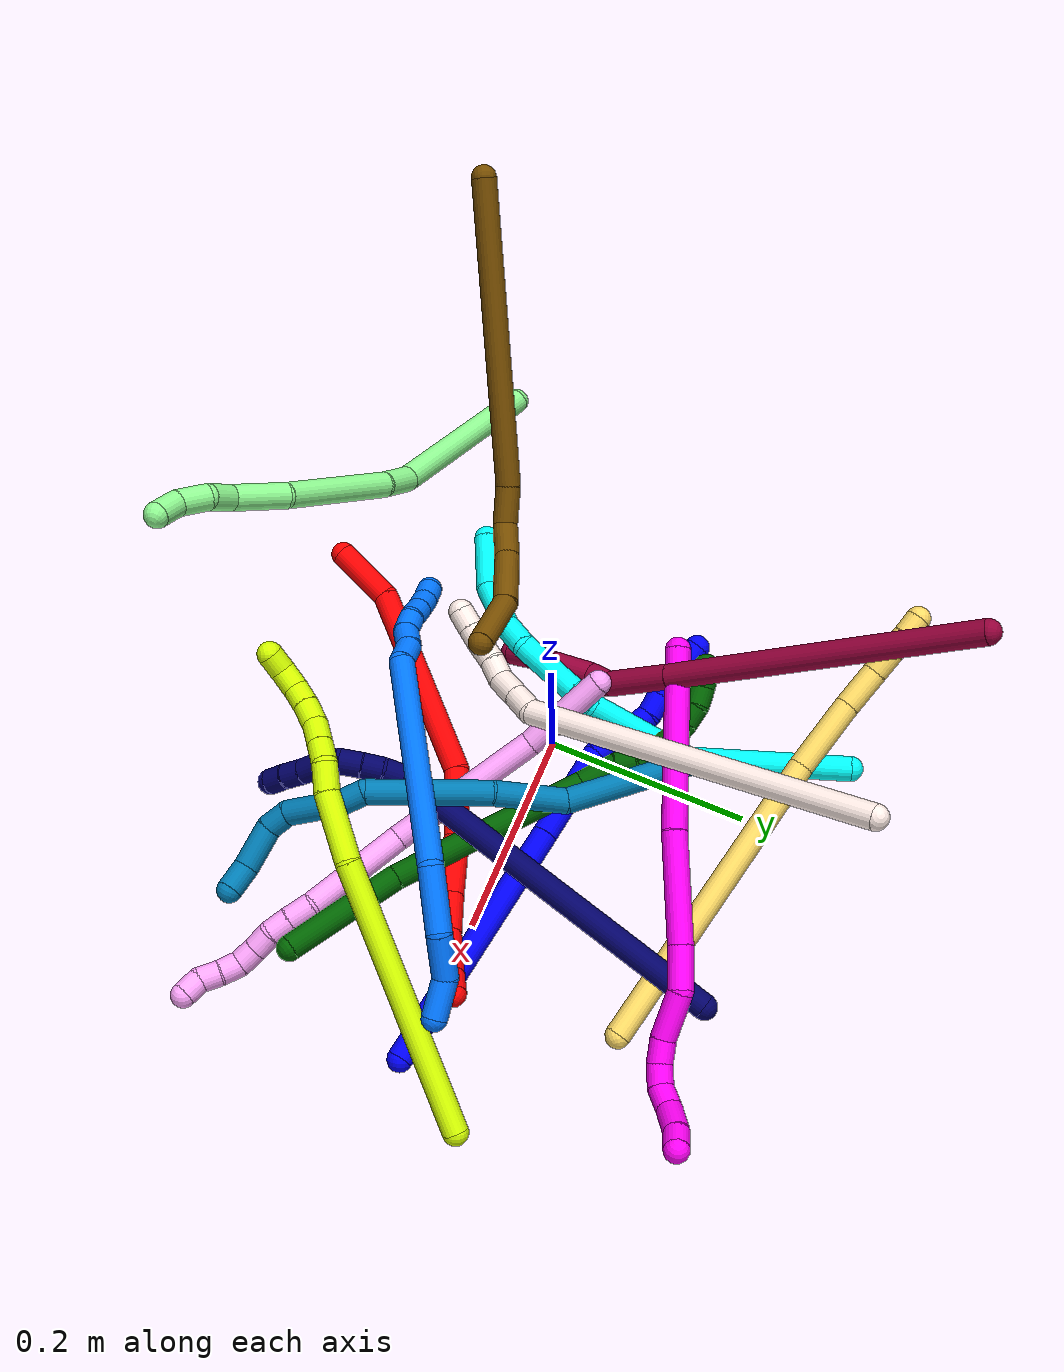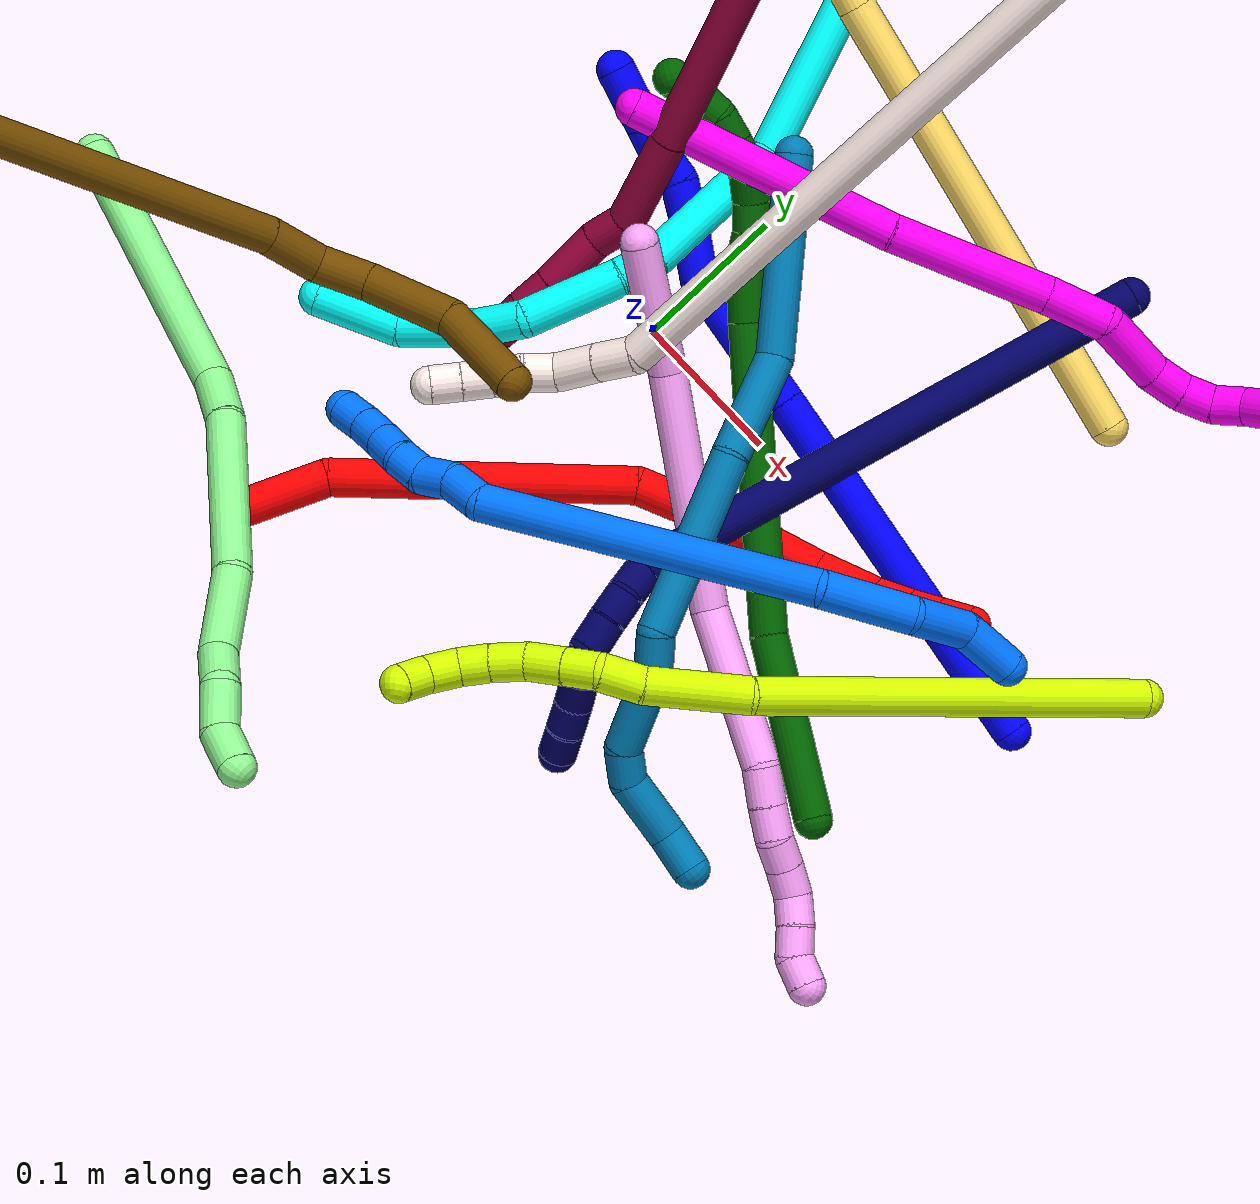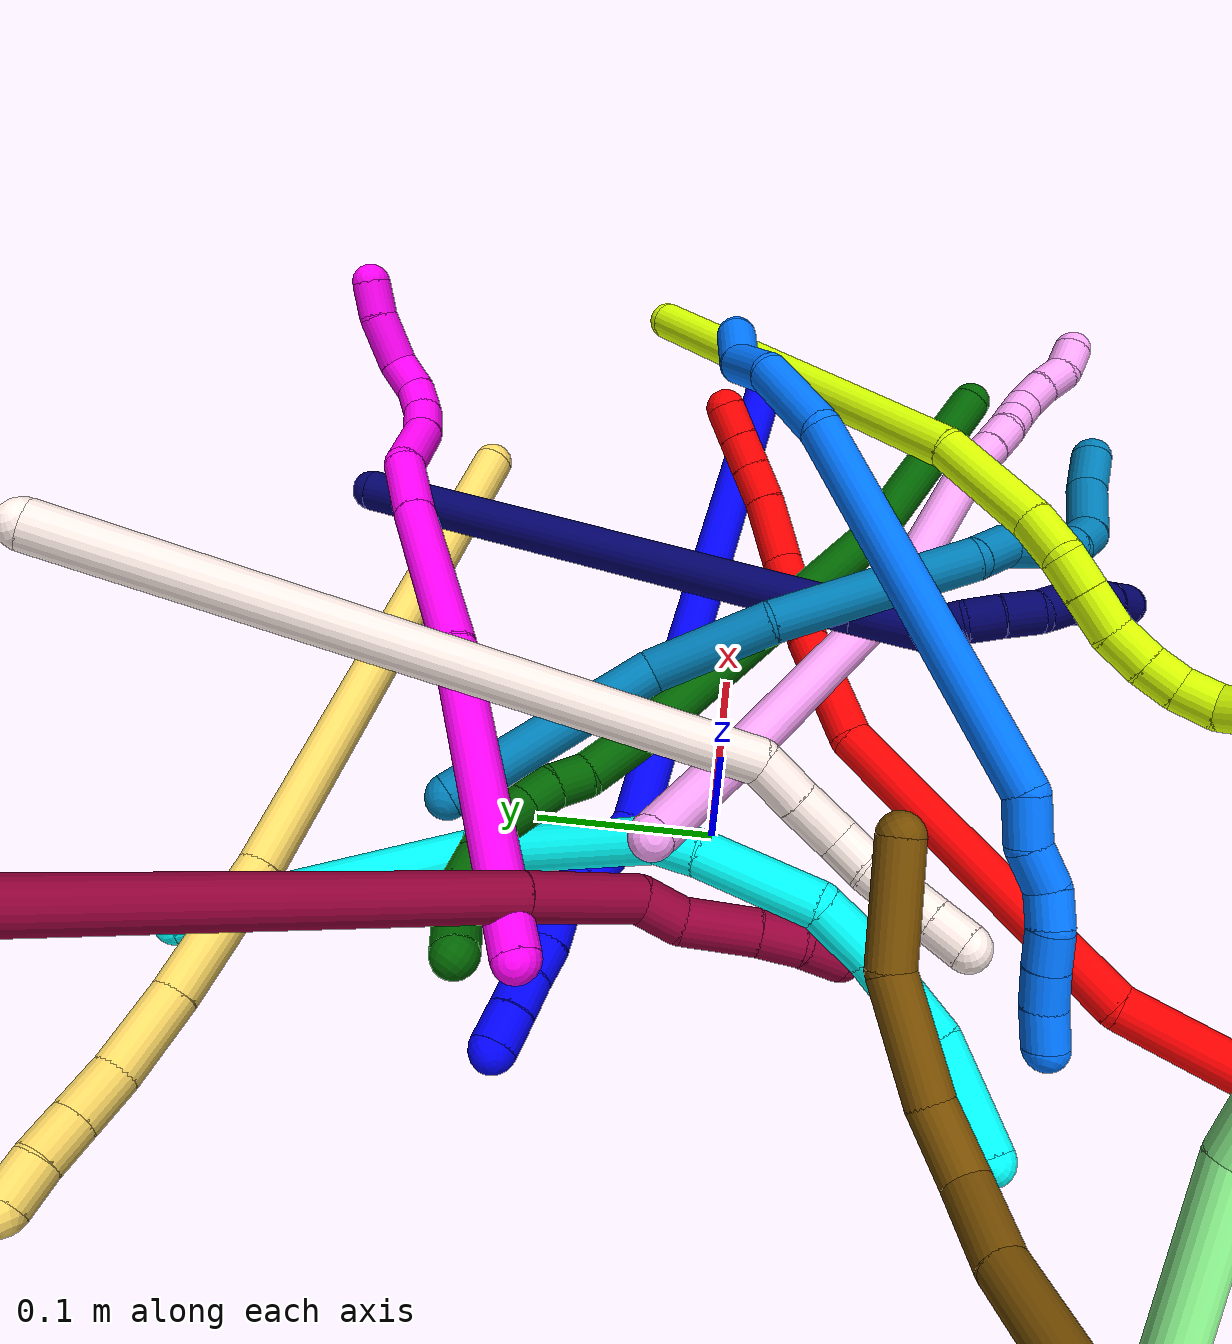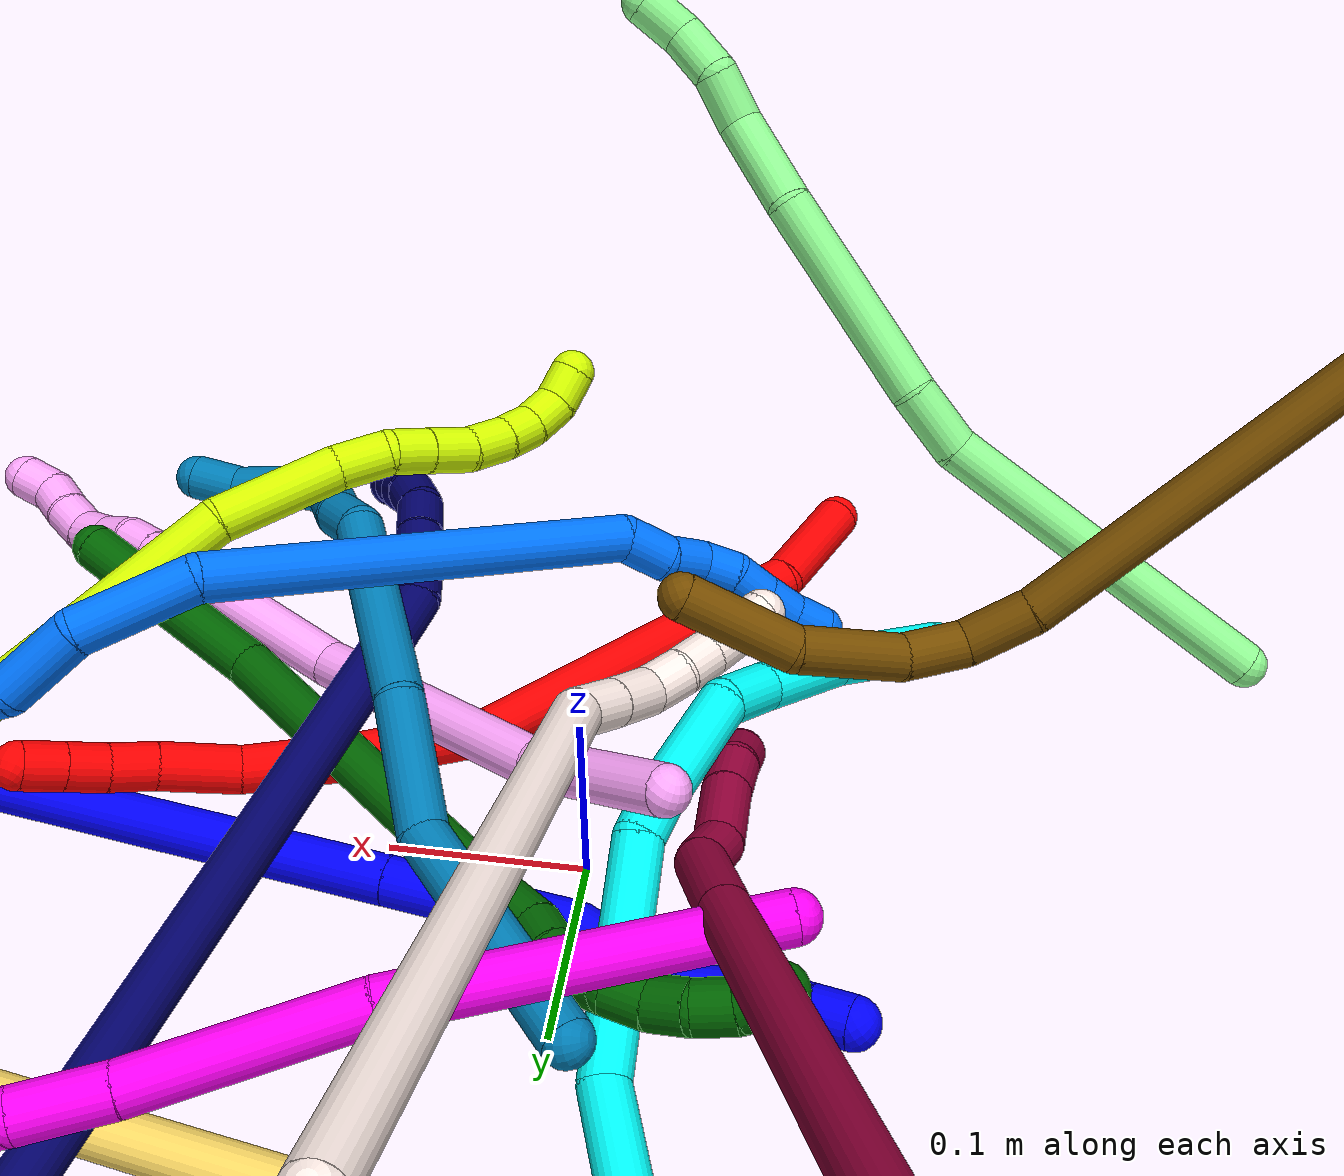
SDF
<sdf version="1.7">
 <world name="default">
  <plugin name="TubeGeneratorPlugin" filename="libtube_generator_plugin.so"/>
  <model name="photoneo_s_sensor">
   <static>1</static>
   <pose>0 0 2 1.57079 1.57079 3.14159</pose>
   <link name="link">
    <inertial><mass>0.1</mass></inertial>
    <sensor name="sensor" type="depth">
     <update_rate>30</update_rate>
     <camera>
      <horizontal_fov>1.22</horizontal_fov>
      <image><width>1920</width><height>1200</height><format>B8G8R8</format></image>
      <clip><near>0.1</near><far>4</far></clip>
      <depth_camera><output>points</output></depth_camera>
     </camera>
     <plugin name="camera_plugin" filename="libgazebo_ros_depth_camera.so">
      <baseline>0.2</baseline>
      <alwaysOn>1</alwaysOn>
      <updateRate>0.0</updateRate>
      <cameraName>camera_ir</cameraName>
      <imageTopicName>/camera/color/image_raw</imageTopicName>
      <cameraInfoTopicName>/camera/color/camera_info</cameraInfoTopicName>
      <depthImageTopicName>/camera/depth/image_raw</depthImageTopicName>
      <depthImageCameraInfoTopicName>/camera/depth/camera_info</depthImageCameraInfoTopicName>
      <pointCloudTopicName>/camera/depth/points</pointCloudTopicName>
      <frameName>fr_optical</frameName>
      <pointCloudCutoff>0.1</pointCloudCutoff>
      <pointCloudCutoffMax>2.0</pointCloudCutoffMax>
      <distortionK1>0</distortionK1>
      <distortionK2>0</distortionK2>
      <distortionK3>0</distortionK3>
      <distortionT1>0</distortionT1>
      <distortionT2>0</distortionT2>
      <CxPrime>0</CxPrime>
      <Cx>0</Cx>
      <Cy>0</Cy>
      <focalLength>0</focalLength>
      <hackBaseline>0</hackBaseline>
     </plugin>
    </sensor>
   </link>
  </model>
  <gravity>0 0 -9.8</gravity>
  <magnetic_field>6e-06 2.3e-05 -4.2e-05</magnetic_field>
  <atmosphere type="adiabatic"/>
  <physics name="default_physics" default="0" type="ode">
   <max_step_size>0.003</max_step_size>
   <real_time_factor>1</real_time_factor>
   <real_time_update_rate>1000</real_time_update_rate>
   <max_contacts>10000</max_contacts>
   <ode>
    <solver>
     <type>quick</type>
     <iters>100</iters>
     <sor>1.3</sor>
     <use_dynamic_moi_rescaling>0</use_dynamic_moi_rescaling>
    </solver>
    <constraints>
     <contact_max_correcting_vel>0</contact_max_correcting_vel>
     <contact_surface_layer>0.001</contact_surface_layer>
     <cfm>0</cfm>
     <erp>0.2</erp>
    </constraints>
   </ode>
  </physics>
  <scene><ambient>0.4 0.4 0.4 1</ambient><background>0.7 0.7 0.7 1</background><shadows>0</shadows></scene>
  <audio><device>default</device></audio>
  <spherical_coordinates>
   <surface_model>EARTH_WGS84</surface_model>
   <latitude_deg>0</latitude_deg>
   <longitude_deg>0</longitude_deg>
   <elevation>0</elevation>
   <heading_deg>0</heading_deg>
  </spherical_coordinates>
  <model name="bin">
   <static>1</static>
   <link name="bottom">
    <collision name="collision-bottom">
     <pose>0 0 -0.01 0 -0 0</pose>
     <geometry><box><size>0.8 0.6 0.02</size></box></geometry>
     <surface>
      <friction><ode><mu>100</mu><mu2>100</mu2></ode></friction>
      <contact><collide_bitmask>65535</collide_bitmask></contact>
     </surface>
    </collision>
   </link>
   <link name="west_wall">
    <collision name="collision-west_wall">
     <pose>-0.41 0 0.1 0 -0 0</pose>
     <geometry><box><size>0.02 0.6 0.2</size></box></geometry>
     <surface>
      <friction><ode><mu>100</mu><mu2>100</mu2></ode></friction>
      <contact><collide_bitmask>65535</collide_bitmask></contact>
     </surface>
    </collision>
   </link>
   <link name="east_wall">
    <collision name="collision-east_wall">
     <pose>0.41 0 0.1 0 -0 0</pose>
     <geometry><box><size>0.02 0.6 0.2</size></box></geometry>
     <surface>
      <friction><ode><mu>100</mu><mu2>100</mu2></ode></friction>
      <contact><collide_bitmask>65535</collide_bitmask></contact>
     </surface>
    </collision>
   </link>
   <link name="south_wall">
    <collision name="collision-south_wall">
     <pose>0 -0.31 0.1 0 -0 0</pose>
     <geometry><box><size>0.8 0.02 0.2</size></box></geometry>
     <surface>
      <friction><ode><mu>100</mu><mu2>100</mu2></ode></friction>
      <contact><collide_bitmask>65535</collide_bitmask></contact>
     </surface>
    </collision>
   </link>
   <link name="north_wall">
    <collision name="collision-north_wall">
     <pose>0 0.31 0.1 0 -0 0</pose>
     <geometry><box><size>0.8 0.02 0.2</size></box></geometry>
     <surface>
      <friction><ode><mu>100</mu><mu2>100</mu2></ode></friction>
      <contact><collide_bitmask>65535</collide_bitmask></contact>
     </surface>
    </collision>
   </link>
  </model>
  <model name="1">
   <static>0</static>
   <link name="1">
    <collision name="collision-cylinder-e_1_1_4">
     <pose>-0.080535 0.021728 -0.097274 -2.92183 -0.679606 2.53659</pose>
     <geometry><cylinder><radius>0.0125</radius><length>0.256282</length></cylinder></geometry>
     <surface>
      <friction><ode><mu>1.16</mu><mu2>1.16</mu2><slip1>0</slip1><slip2>0</slip2></ode></friction>
      <contact><ode><kp>1e+06</kp><kd>1</kd><max_vel>0</max_vel><min_depth>0.001</min_depth></ode></contact>
     </surface>
    </collision>
    <visual name="visual-cylinder-e_1_1_4">
     <pose>-0.080535 0.021728 -0.097274 -2.92183 -0.679606 2.53659</pose>
     <geometry><cylinder><radius>0.0125</radius><length>0.256282</length></cylinder></geometry>
     <material><ambient>0 0 1 1</ambient></material>
    </visual>
    <collision name="collision-cylinder-e_2_4_5">
     <pose>-0.191255 0.052341 -0.230812 -2.90134 -0.67987 2.48377</pose>
     <geometry><cylinder><radius>0.0125</radius><length>0.096026</length></cylinder></geometry>
     <surface>
      <friction><ode><mu>1.16</mu><mu2>1.16</mu2><slip1>0</slip1><slip2>0</slip2></ode></friction>
      <contact><ode><kp>1e+06</kp><kd>1</kd><max_vel>0</max_vel><min_depth>0.001</min_depth></ode></contact>
     </surface>
    </collision>
    <visual name="visual-cylinder-e_2_4_5">
     <pose>-0.191255 0.052341 -0.230812 -2.90134 -0.67987 2.48377</pose>
     <geometry><cylinder><radius>0.0125</radius><length>0.096026</length></cylinder></geometry>
     <material><ambient>0 0 1 1</ambient></material>
    </visual>
    <collision name="collision-cylinder-e_3_5_6">
     <pose>-0.23789 0.057111 -0.279653 2.82545 -0.893374 -2.49907</pose>
     <geometry><cylinder><radius>0.0125</radius><length>0.042222</length></cylinder></geometry>
     <surface>
      <friction><ode><mu>1.16</mu><mu2>1.16</mu2><slip1>0</slip1><slip2>0</slip2></ode></friction>
      <contact><ode><kp>1e+06</kp><kd>1</kd><max_vel>0</max_vel><min_depth>0.001</min_depth></ode></contact>
     </surface>
    </collision>
    <visual name="visual-cylinder-e_3_5_6">
     <pose>-0.23789 0.057111 -0.279653 2.82545 -0.893374 -2.49907</pose>
     <geometry><cylinder><radius>0.0125</radius><length>0.042222</length></cylinder></geometry>
     <material><ambient>0 0 1 1</ambient></material>
    </visual>
    <collision name="collision-cylinder-e_4_6_7">
     <pose>-0.262875 0.051172 -0.299337 2.8902 -0.860722 -2.60437</pose>
     <geometry><cylinder><radius>0.0125</radius><length>0.022514</length></cylinder></geometry>
     <surface>
      <friction><ode><mu>1.16</mu><mu2>1.16</mu2><slip1>0</slip1><slip2>0</slip2></ode></friction>
      <contact><ode><kp>1e+06</kp><kd>1</kd><max_vel>0</max_vel><min_depth>0.001</min_depth></ode></contact>
     </surface>
    </collision>
    <visual name="visual-cylinder-e_4_6_7">
     <pose>-0.262875 0.051172 -0.299337 2.8902 -0.860722 -2.60437</pose>
     <geometry><cylinder><radius>0.0125</radius><length>0.022514</length></cylinder></geometry>
     <material><ambient>0 0 1 1</ambient></material>
    </visual>
    <collision name="collision-cylinder-e_5_7_8">
     <pose>-0.2775 0.050247 -0.316099 -3.0486 -0.560676 2.82115</pose>
     <geometry><cylinder><radius>0.0125</radius><length>0.022897</length></cylinder></geometry>
     <surface>
      <friction><ode><mu>1.16</mu><mu2>1.16</mu2><slip1>0</slip1><slip2>0</slip2></ode></friction>
      <contact><ode><kp>1e+06</kp><kd>1</kd><max_vel>0</max_vel><min_depth>0.001</min_depth></ode></contact>
     </surface>
    </collision>
    <visual name="visual-cylinder-e_5_7_8">
     <pose>-0.2775 0.050247 -0.316099 -3.0486 -0.560676 2.82115</pose>
     <geometry><cylinder><radius>0.0125</radius><length>0.022897</length></cylinder></geometry>
     <material><ambient>0 0 1 1</ambient></material>
    </visual>
    <collision name="collision-cylinder-e_6_8_9">
     <pose>-0.289081 0.049796 -0.334015 2.97955 -0.580663 -2.61086</pose>
     <geometry><cylinder><radius>0.0125</radius><length>0.020028</length></cylinder></geometry>
     <surface>
      <friction><ode><mu>1.16</mu><mu2>1.16</mu2><slip1>0</slip1><slip2>0</slip2></ode></friction>
      <contact><ode><kp>1e+06</kp><kd>1</kd><max_vel>0</max_vel><min_depth>0.001</min_depth></ode></contact>
     </surface>
    </collision>
    <visual name="visual-cylinder-e_6_8_9">
     <pose>-0.289081 0.049796 -0.334015 2.97955 -0.580663 -2.61086</pose>
     <geometry><cylinder><radius>0.0125</radius><length>0.020028</length></cylinder></geometry>
     <material><ambient>0 0 1 1</ambient></material>
    </visual>
    <collision name="collision-cylinder-e_7_9_10">
     <pose>-0.300559 0.048176 -0.350303 3.108 -0.640523 -3.04038</pose>
     <geometry><cylinder><radius>0.0125</radius><length>0.02003</length></cylinder></geometry>
     <surface>
      <friction><ode><mu>1.16</mu><mu2>1.16</mu2><slip1>0</slip1><slip2>0</slip2></ode></friction>
      <contact><ode><kp>1e+06</kp><kd>1</kd><max_vel>0</max_vel><min_depth>0.001</min_depth></ode></contact>
     </surface>
    </collision>
    <visual name="visual-cylinder-e_7_9_10">
     <pose>-0.300559 0.048176 -0.350303 3.108 -0.640523 -3.04038</pose>
     <geometry><cylinder><radius>0.0125</radius><length>0.02003</length></cylinder></geometry>
     <material><ambient>0 0 1 1</ambient></material>
    </visual>
    <collision name="collision-cylinder-e_8_10_2">
     <pose>-0.312968 0.047802 -0.365993 3.12805 -0.69756 -3.10436</pose>
     <geometry><cylinder><radius>0.0125</radius><length>0.020002</length></cylinder></geometry>
     <surface>
      <friction><ode><mu>1.16</mu><mu2>1.16</mu2><slip1>0</slip1><slip2>0</slip2></ode></friction>
      <contact><ode><kp>1e+06</kp><kd>1</kd><max_vel>0</max_vel><min_depth>0.001</min_depth></ode></contact>
     </surface>
    </collision>
    <visual name="visual-cylinder-e_8_10_2">
     <pose>-0.312968 0.047802 -0.365993 3.12805 -0.69756 -3.10436</pose>
     <geometry><cylinder><radius>0.0125</radius><length>0.020002</length></cylinder></geometry>
     <material><ambient>0 0 1 1</ambient></material>
    </visual>
    <collision name="collision-sphere-2">
     <pose>-0.319393 0.047699 -0.373657 0 -0 0</pose>
     <geometry><sphere><radius>0.0125</radius></sphere></geometry>
     <surface>
      <friction><ode><mu>1.16</mu><mu2>1.16</mu2><slip1>0</slip1><slip2>0</slip2></ode></friction>
      <contact><ode><kp>1e+06</kp><kd>1</kd><max_vel>0</max_vel><min_depth>0.001</min_depth></ode></contact>
     </surface>
    </collision>
    <visual name="visual-sphere-2">
     <pose>-0.319393 0.047699 -0.373657 0 -0 0</pose>
     <geometry><sphere><radius>0.0125</radius></sphere></geometry>
     <material><ambient>0 0 1 1</ambient></material>
    </visual>
    <collision name="collision-sphere-10">
     <pose>-0.306544 0.047906 -0.358329 0 -0 0</pose>
     <geometry><sphere><radius>0.0125</radius></sphere></geometry>
     <surface>
      <friction><ode><mu>1.16</mu><mu2>1.16</mu2><slip1>0</slip1><slip2>0</slip2></ode></friction>
      <contact><ode><kp>1e+06</kp><kd>1</kd><max_vel>0</max_vel><min_depth>0.001</min_depth></ode></contact>
     </surface>
    </collision>
    <visual name="visual-sphere-10">
     <pose>-0.306544 0.047906 -0.358329 0 -0 0</pose>
     <geometry><sphere><radius>0.0125</radius></sphere></geometry>
     <material><ambient>0 0 1 1</ambient></material>
    </visual>
    <collision name="collision-sphere-9">
     <pose>-0.294574 0.048446 -0.342278 0 -0 0</pose>
     <geometry><sphere><radius>0.0125</radius></sphere></geometry>
     <surface>
      <friction><ode><mu>1.16</mu><mu2>1.16</mu2><slip1>0</slip1><slip2>0</slip2></ode></friction>
      <contact><ode><kp>1e+06</kp><kd>1</kd><max_vel>0</max_vel><min_depth>0.001</min_depth></ode></contact>
     </surface>
    </collision>
    <visual name="visual-sphere-9">
     <pose>-0.294574 0.048446 -0.342278 0 -0 0</pose>
     <geometry><sphere><radius>0.0125</radius></sphere></geometry>
     <material><ambient>0 0 1 1</ambient></material>
    </visual>
    <collision name="collision-sphere-4">
     <pose>-0.16107 0.043456 -0.194547 0 -0 0</pose>
     <geometry><sphere><radius>0.0125</radius></sphere></geometry>
     <surface>
      <friction><ode><mu>1.16</mu><mu2>1.16</mu2><slip1>0</slip1><slip2>0</slip2></ode></friction>
      <contact><ode><kp>1e+06</kp><kd>1</kd><max_vel>0</max_vel><min_depth>0.001</min_depth></ode></contact>
     </surface>
    </collision>
    <visual name="visual-sphere-4">
     <pose>-0.16107 0.043456 -0.194547 0 -0 0</pose>
     <geometry><sphere><radius>0.0125</radius></sphere></geometry>
     <material><ambient>0 0 1 1</ambient></material>
    </visual>
    <collision name="collision-sphere-1">
     <geometry><sphere><radius>0.0125</radius></sphere></geometry>
     <surface>
      <friction><ode><mu>1.16</mu><mu2>1.16</mu2><slip1>0</slip1><slip2>0</slip2></ode></friction>
      <contact><ode><kp>1e+06</kp><kd>1</kd><max_vel>0</max_vel><min_depth>0.001</min_depth></ode></contact>
     </surface>
    </collision>
    <visual name="visual-sphere-1">
     <geometry><sphere><radius>0.0125</radius></sphere></geometry>
     <material><ambient>0 0 1 1</ambient></material>
    </visual>
    <collision name="collision-sphere-8">
     <pose>-0.283587 0.051147 -0.325752 0 -0 0</pose>
     <geometry><sphere><radius>0.0125</radius></sphere></geometry>
     <surface>
      <friction><ode><mu>1.16</mu><mu2>1.16</mu2><slip1>0</slip1><slip2>0</slip2></ode></friction>
      <contact><ode><kp>1e+06</kp><kd>1</kd><max_vel>0</max_vel><min_depth>0.001</min_depth></ode></contact>
     </surface>
    </collision>
    <visual name="visual-sphere-8">
     <pose>-0.283587 0.051147 -0.325752 0 -0 0</pose>
     <geometry><sphere><radius>0.0125</radius></sphere></geometry>
     <material><ambient>0 0 1 1</ambient></material>
    </visual>
    <collision name="collision-sphere-5">
     <pose>-0.22144 0.061225 -0.267077 0 -0 0</pose>
     <geometry><sphere><radius>0.0125</radius></sphere></geometry>
     <surface>
      <friction><ode><mu>1.16</mu><mu2>1.16</mu2><slip1>0</slip1><slip2>0</slip2></ode></friction>
      <contact><ode><kp>1e+06</kp><kd>1</kd><max_vel>0</max_vel><min_depth>0.001</min_depth></ode></contact>
     </surface>
    </collision>
    <visual name="visual-sphere-5">
     <pose>-0.22144 0.061225 -0.267077 0 -0 0</pose>
     <geometry><sphere><radius>0.0125</radius></sphere></geometry>
     <material><ambient>0 0 1 1</ambient></material>
    </visual>
    <collision name="collision-sphere-6">
     <pose>-0.254339 0.052997 -0.29223 0 -0 0</pose>
     <geometry><sphere><radius>0.0125</radius></sphere></geometry>
     <surface>
      <friction><ode><mu>1.16</mu><mu2>1.16</mu2><slip1>0</slip1><slip2>0</slip2></ode></friction>
      <contact><ode><kp>1e+06</kp><kd>1</kd><max_vel>0</max_vel><min_depth>0.001</min_depth></ode></contact>
     </surface>
    </collision>
    <visual name="visual-sphere-6">
     <pose>-0.254339 0.052997 -0.29223 0 -0 0</pose>
     <geometry><sphere><radius>0.0125</radius></sphere></geometry>
     <material><ambient>0 0 1 1</ambient></material>
    </visual>
    <collision name="collision-sphere-7">
     <pose>-0.271412 0.049347 -0.306445 0 -0 0</pose>
     <geometry><sphere><radius>0.0125</radius></sphere></geometry>
     <surface>
      <friction><ode><mu>1.16</mu><mu2>1.16</mu2><slip1>0</slip1><slip2>0</slip2></ode></friction>
      <contact><ode><kp>1e+06</kp><kd>1</kd><max_vel>0</max_vel><min_depth>0.001</min_depth></ode></contact>
     </surface>
    </collision>
    <visual name="visual-sphere-7">
     <pose>-0.271412 0.049347 -0.306445 0 -0 0</pose>
     <geometry><sphere><radius>0.0125</radius></sphere></geometry>
     <material><ambient>0 0 1 1</ambient></material>
    </visual>
    <inertial>
     <pose>-0.158782 0.036454 -0.187809 0 -0 0</pose>
     <mass>0.5</mass>
     <inertia>
      <ixx>-0.000328</ixx>
      <ixy>0</ixy>
      <ixz>0</ixz>
      <iyy>0.001987</iyy>
      <iyz>0</iyz>
      <izz>0.000667</izz>
     </inertia>
    </inertial>
   </link>
   <pose>0.344636 -0.009348 0.011492 -2.21176 -0.463312 -0.944536</pose>
  </model>
  <model name="2">
   <static>0</static>
   <link name="2">
    <collision name="collision-cylinder-e_1_1_4">
     <pose>0.005098 0.009315 -0.030185 -2.84228 0.160003 -0.977372</pose>
     <geometry><cylinder><radius>0.0125</radius><length>0.063996</length></cylinder></geometry>
     <surface>
      <friction><ode><mu>1.16</mu><mu2>1.16</mu2><slip1>0</slip1><slip2>0</slip2></ode></friction>
      <contact><ode><kp>1e+06</kp><kd>1</kd><max_vel>0</max_vel><min_depth>0.001</min_depth></ode></contact>
     </surface>
    </collision>
    <visual name="visual-cylinder-e_1_1_4">
     <pose>0.005098 0.009315 -0.030185 -2.84228 0.160003 -0.977372</pose>
     <geometry><cylinder><radius>0.0125</radius><length>0.063996</length></cylinder></geometry>
     <material><ambient>1 0 0 1</ambient></material>
    </visual>
    <collision name="collision-cylinder-e_2_4_5">
     <pose>0.060705 0.046745 -0.141055 -2.80629 0.533883 -2.03324</pose>
     <geometry><cylinder><radius>0.0125</radius><length>0.198511</length></cylinder></geometry>
     <surface>
      <friction><ode><mu>1.16</mu><mu2>1.16</mu2><slip1>0</slip1><slip2>0</slip2></ode></friction>
      <contact><ode><kp>1e+06</kp><kd>1</kd><max_vel>0</max_vel><min_depth>0.001</min_depth></ode></contact>
     </surface>
    </collision>
    <visual name="visual-cylinder-e_2_4_5">
     <pose>0.060705 0.046745 -0.141055 -2.80629 0.533883 -2.03324</pose>
     <geometry><cylinder><radius>0.0125</radius><length>0.198511</length></cylinder></geometry>
     <material><ambient>1 0 0 1</ambient></material>
    </visual>
    <collision name="collision-cylinder-e_3_5_6">
     <pose>0.137865 0.084164 -0.241085 -2.69333 0.892724 -2.25252</pose>
     <geometry><cylinder><radius>0.0125</radius><length>0.068441</length></cylinder></geometry>
     <surface>
      <friction><ode><mu>1.16</mu><mu2>1.16</mu2><slip1>0</slip1><slip2>0</slip2></ode></friction>
      <contact><ode><kp>1e+06</kp><kd>1</kd><max_vel>0</max_vel><min_depth>0.001</min_depth></ode></contact>
     </surface>
    </collision>
    <visual name="visual-cylinder-e_3_5_6">
     <pose>0.137865 0.084164 -0.241085 -2.69333 0.892724 -2.25252</pose>
     <geometry><cylinder><radius>0.0125</radius><length>0.068441</length></cylinder></geometry>
     <material><ambient>1 0 0 1</ambient></material>
    </visual>
    <collision name="collision-cylinder-e_4_6_7">
     <pose>0.189086 0.101409 -0.27487 -2.63875 0.980029 -2.24405</pose>
     <geometry><cylinder><radius>0.0125</radius><length>0.059171</length></cylinder></geometry>
     <surface>
      <friction><ode><mu>1.16</mu><mu2>1.16</mu2><slip1>0</slip1><slip2>0</slip2></ode></friction>
      <contact><ode><kp>1e+06</kp><kd>1</kd><max_vel>0</max_vel><min_depth>0.001</min_depth></ode></contact>
     </surface>
    </collision>
    <visual name="visual-cylinder-e_4_6_7">
     <pose>0.189086 0.101409 -0.27487 -2.63875 0.980029 -2.24405</pose>
     <geometry><cylinder><radius>0.0125</radius><length>0.059171</length></cylinder></geometry>
     <material><ambient>1 0 0 1</ambient></material>
    </visual>
    <collision name="collision-cylinder-e_5_7_8">
     <pose>0.229159 0.120488 -0.298431 -2.25704 0.822365 -1.48833</pose>
     <geometry><cylinder><radius>0.0125</radius><length>0.042311</length></cylinder></geometry>
     <surface>
      <friction><ode><mu>1.16</mu><mu2>1.16</mu2><slip1>0</slip1><slip2>0</slip2></ode></friction>
      <contact><ode><kp>1e+06</kp><kd>1</kd><max_vel>0</max_vel><min_depth>0.001</min_depth></ode></contact>
     </surface>
    </collision>
    <visual name="visual-cylinder-e_5_7_8">
     <pose>0.229159 0.120488 -0.298431 -2.25704 0.822365 -1.48833</pose>
     <geometry><cylinder><radius>0.0125</radius><length>0.042311</length></cylinder></geometry>
     <material><ambient>1 0 0 1</ambient></material>
    </visual>
    <collision name="collision-cylinder-e_6_8_9">
     <pose>0.252823 0.13809 -0.313831 -2.34164 0.735975 -1.47877</pose>
     <geometry><cylinder><radius>0.0125</radius><length>0.024317</length></cylinder></geometry>
     <surface>
      <friction><ode><mu>1.16</mu><mu2>1.16</mu2><slip1>0</slip1><slip2>0</slip2></ode></friction>
      <contact><ode><kp>1e+06</kp><kd>1</kd><max_vel>0</max_vel><min_depth>0.001</min_depth></ode></contact>
     </surface>
    </collision>
    <visual name="visual-cylinder-e_6_8_9">
     <pose>0.252823 0.13809 -0.313831 -2.34164 0.735975 -1.47877</pose>
     <geometry><cylinder><radius>0.0125</radius><length>0.024317</length></cylinder></geometry>
     <material><ambient>1 0 0 1</ambient></material>
    </visual>
    <collision name="collision-cylinder-e_7_9_10">
     <pose>0.267429 0.151394 -0.325367 -2.22603 0.641538 -1.1866</pose>
     <geometry><cylinder><radius>0.0125</radius><length>0.021536</length></cylinder></geometry>
     <surface>
      <friction><ode><mu>1.16</mu><mu2>1.16</mu2><slip1>0</slip1><slip2>0</slip2></ode></friction>
      <contact><ode><kp>1e+06</kp><kd>1</kd><max_vel>0</max_vel><min_depth>0.001</min_depth></ode></contact>
     </surface>
    </collision>
    <visual name="visual-cylinder-e_7_9_10">
     <pose>0.267429 0.151394 -0.325367 -2.22603 0.641538 -1.1866</pose>
     <geometry><cylinder><radius>0.0125</radius><length>0.021536</length></cylinder></geometry>
     <material><ambient>1 0 0 1</ambient></material>
    </visual>
    <collision name="collision-cylinder-e_8_10_2">
     <pose>0.280381 0.165121 -0.335927 -2.22706 0.642648 -1.18952</pose>
     <geometry><cylinder><radius>0.0125</radius><length>0.021716</length></cylinder></geometry>
     <surface>
      <friction><ode><mu>1.16</mu><mu2>1.16</mu2><slip1>0</slip1><slip2>0</slip2></ode></friction>
      <contact><ode><kp>1e+06</kp><kd>1</kd><max_vel>0</max_vel><min_depth>0.001</min_depth></ode></contact>
     </surface>
    </collision>
    <visual name="visual-cylinder-e_8_10_2">
     <pose>0.280381 0.165121 -0.335927 -2.22706 0.642648 -1.18952</pose>
     <geometry><cylinder><radius>0.0125</radius><length>0.021716</length></cylinder></geometry>
     <material><ambient>1 0 0 1</ambient></material>
    </visual>
    <collision name="collision-sphere-2">
     <pose>0.286888 0.172008 -0.341231 0 -0 0</pose>
     <geometry><sphere><radius>0.0125</radius></sphere></geometry>
     <surface>
      <friction><ode><mu>1.16</mu><mu2>1.16</mu2><slip1>0</slip1><slip2>0</slip2></ode></friction>
      <contact><ode><kp>1e+06</kp><kd>1</kd><max_vel>0</max_vel><min_depth>0.001</min_depth></ode></contact>
     </surface>
    </collision>
    <visual name="visual-sphere-2">
     <pose>0.286888 0.172008 -0.341231 0 -0 0</pose>
     <geometry><sphere><radius>0.0125</radius></sphere></geometry>
     <material><ambient>1 0 0 1</ambient></material>
    </visual>
    <collision name="collision-sphere-10">
     <pose>0.273873 0.158235 -0.330624 0 -0 0</pose>
     <geometry><sphere><radius>0.0125</radius></sphere></geometry>
     <surface>
      <friction><ode><mu>1.16</mu><mu2>1.16</mu2><slip1>0</slip1><slip2>0</slip2></ode></friction>
      <contact><ode><kp>1e+06</kp><kd>1</kd><max_vel>0</max_vel><min_depth>0.001</min_depth></ode></contact>
     </surface>
    </collision>
    <visual name="visual-sphere-10">
     <pose>0.273873 0.158235 -0.330624 0 -0 0</pose>
     <geometry><sphere><radius>0.0125</radius></sphere></geometry>
     <material><ambient>1 0 0 1</ambient></material>
    </visual>
    <collision name="collision-sphere-9">
     <pose>0.260986 0.144554 -0.32011 0 -0 0</pose>
     <geometry><sphere><radius>0.0125</radius></sphere></geometry>
     <surface>
      <friction><ode><mu>1.16</mu><mu2>1.16</mu2><slip1>0</slip1><slip2>0</slip2></ode></friction>
      <contact><ode><kp>1e+06</kp><kd>1</kd><max_vel>0</max_vel><min_depth>0.001</min_depth></ode></contact>
     </surface>
    </collision>
    <visual name="visual-sphere-9">
     <pose>0.260986 0.144554 -0.32011 0 -0 0</pose>
     <geometry><sphere><radius>0.0125</radius></sphere></geometry>
     <material><ambient>1 0 0 1</ambient></material>
    </visual>
    <collision name="collision-sphere-4">
     <pose>0.010196 0.018629 -0.06037 0 -0 0</pose>
     <geometry><sphere><radius>0.0125</radius></sphere></geometry>
     <surface>
      <friction><ode><mu>1.16</mu><mu2>1.16</mu2><slip1>0</slip1><slip2>0</slip2></ode></friction>
      <contact><ode><kp>1e+06</kp><kd>1</kd><max_vel>0</max_vel><min_depth>0.001</min_depth></ode></contact>
     </surface>
    </collision>
    <visual name="visual-sphere-4">
     <pose>0.010196 0.018629 -0.06037 0 -0 0</pose>
     <geometry><sphere><radius>0.0125</radius></sphere></geometry>
     <material><ambient>1 0 0 1</ambient></material>
    </visual>
    <collision name="collision-sphere-1">
     <geometry><sphere><radius>0.0125</radius></sphere></geometry>
     <surface>
      <friction><ode><mu>1.16</mu><mu2>1.16</mu2><slip1>0</slip1><slip2>0</slip2></ode></friction>
      <contact><ode><kp>1e+06</kp><kd>1</kd><max_vel>0</max_vel><min_depth>0.001</min_depth></ode></contact>
     </surface>
    </collision>
    <visual name="visual-sphere-1">
     <geometry><sphere><radius>0.0125</radius></sphere></geometry>
     <material><ambient>1 0 0 1</ambient></material>
    </visual>
    <collision name="collision-sphere-8">
     <pose>0.244661 0.131625 -0.307552 0 -0 0</pose>
     <geometry><sphere><radius>0.0125</radius></sphere></geometry>
     <surface>
      <friction><ode><mu>1.16</mu><mu2>1.16</mu2><slip1>0</slip1><slip2>0</slip2></ode></friction>
      <contact><ode><kp>1e+06</kp><kd>1</kd><max_vel>0</max_vel><min_depth>0.001</min_depth></ode></contact>
     </surface>
    </collision>
    <visual name="visual-sphere-8">
     <pose>0.244661 0.131625 -0.307552 0 -0 0</pose>
     <geometry><sphere><radius>0.0125</radius></sphere></geometry>
     <material><ambient>1 0 0 1</ambient></material>
    </visual>
    <collision name="collision-sphere-5">
     <pose>0.111214 0.074861 -0.221739 0 -0 0</pose>
     <geometry><sphere><radius>0.0125</radius></sphere></geometry>
     <surface>
      <friction><ode><mu>1.16</mu><mu2>1.16</mu2><slip1>0</slip1><slip2>0</slip2></ode></friction>
      <contact><ode><kp>1e+06</kp><kd>1</kd><max_vel>0</max_vel><min_depth>0.001</min_depth></ode></contact>
     </surface>
    </collision>
    <visual name="visual-sphere-5">
     <pose>0.111214 0.074861 -0.221739 0 -0 0</pose>
     <geometry><sphere><radius>0.0125</radius></sphere></geometry>
     <material><ambient>1 0 0 1</ambient></material>
    </visual>
    <collision name="collision-sphere-6">
     <pose>0.164515 0.093468 -0.26043 0 -0 0</pose>
     <geometry><sphere><radius>0.0125</radius></sphere></geometry>
     <surface>
      <friction><ode><mu>1.16</mu><mu2>1.16</mu2><slip1>0</slip1><slip2>0</slip2></ode></friction>
      <contact><ode><kp>1e+06</kp><kd>1</kd><max_vel>0</max_vel><min_depth>0.001</min_depth></ode></contact>
     </surface>
    </collision>
    <visual name="visual-sphere-6">
     <pose>0.164515 0.093468 -0.26043 0 -0 0</pose>
     <geometry><sphere><radius>0.0125</radius></sphere></geometry>
     <material><ambient>1 0 0 1</ambient></material>
    </visual>
    <collision name="collision-sphere-7">
     <pose>0.213658 0.109351 -0.289309 0 -0 0</pose>
     <geometry><sphere><radius>0.0125</radius></sphere></geometry>
     <surface>
      <friction><ode><mu>1.16</mu><mu2>1.16</mu2><slip1>0</slip1><slip2>0</slip2></ode></friction>
      <contact><ode><kp>1e+06</kp><kd>1</kd><max_vel>0</max_vel><min_depth>0.001</min_depth></ode></contact>
     </surface>
    </collision>
    <visual name="visual-sphere-7">
     <pose>0.213658 0.109351 -0.289309 0 -0 0</pose>
     <geometry><sphere><radius>0.0125</radius></sphere></geometry>
     <material><ambient>1 0 0 1</ambient></material>
    </visual>
    <inertial>
     <pose>0.121386 0.073877 -0.194515 0 -0 0</pose>
     <mass>0.5</mass>
     <inertia>
      <ixx>-0.000795</ixx>
      <ixy>0</ixy>
      <ixz>0</ixz>
      <iyy>-0.000135</iyy>
      <iyz>0</iyz>
      <izz>-0.000629</izz>
     </inertia>
    </inertial>
   </link>
   <pose>-0.10079 -0.274226 0.012172 1.30045 0.121449 -0.247506</pose>
  </model>
  <model name="3">
   <static>0</static>
   <link name="3">
    <collision name="collision-cylinder-e_1_1_4">
     <pose>0.003349 -0.076445 -0.021193 1.84123 0.042188 0.055468</pose>
     <geometry><cylinder><radius>0.0125</radius><length>0.158797</length></cylinder></geometry>
     <surface>
      <friction><ode><mu>1.16</mu><mu2>1.16</mu2><slip1>0</slip1><slip2>0</slip2></ode></friction>
      <contact><ode><kp>1e+06</kp><kd>1</kd><max_vel>0</max_vel><min_depth>0.001</min_depth></ode></contact>
     </surface>
    </collision>
    <visual name="visual-cylinder-e_1_1_4">
     <pose>0.003349 -0.076445 -0.021193 1.84123 0.042188 0.055468</pose>
     <geometry><cylinder><radius>0.0125</radius><length>0.158797</length></cylinder></geometry>
     <material><ambient>0.003922 1 0.996078 1</ambient></material>
    </visual>
    <collision name="collision-cylinder-e_2_4_5">
     <pose>-0.005013 -0.206741 -0.033202 1.4019 -0.211169 -0.1784</pose>
     <geometry><cylinder><radius>0.0125</radius><length>0.11174</length></cylinder></geometry>
     <surface>
      <friction><ode><mu>1.16</mu><mu2>1.16</mu2><slip1>0</slip1><slip2>0</slip2></ode></friction>
      <contact><ode><kp>1e+06</kp><kd>1</kd><max_vel>0</max_vel><min_depth>0.001</min_depth></ode></contact>
     </surface>
    </collision>
    <visual name="visual-cylinder-e_2_4_5">
     <pose>-0.005013 -0.206741 -0.033202 1.4019 -0.211169 -0.1784</pose>
     <geometry><cylinder><radius>0.0125</radius><length>0.11174</length></cylinder></geometry>
     <material><ambient>0.003922 1 0.996078 1</ambient></material>
    </visual>
    <collision name="collision-cylinder-e_3_5_6">
     <pose>-0.023029 -0.271149 -0.023755 1.5457 -0.538305 -0.525575</pose>
     <geometry><cylinder><radius>0.0125</radius><length>0.024597</length></cylinder></geometry>
     <surface>
      <friction><ode><mu>1.16</mu><mu2>1.16</mu2><slip1>0</slip1><slip2>0</slip2></ode></friction>
      <contact><ode><kp>1e+06</kp><kd>1</kd><max_vel>0</max_vel><min_depth>0.001</min_depth></ode></contact>
     </surface>
    </collision>
    <visual name="visual-cylinder-e_3_5_6">
     <pose>-0.023029 -0.271149 -0.023755 1.5457 -0.538305 -0.525575</pose>
     <geometry><cylinder><radius>0.0125</radius><length>0.024597</length></cylinder></geometry>
     <material><ambient>0.003922 1 0.996078 1</ambient></material>
    </visual>
    <collision name="collision-cylinder-e_4_6_7">
     <pose>-0.04858 -0.307726 -0.026375 1.68123 -0.633887 -0.702386</pose>
     <geometry><cylinder><radius>0.0125</radius><length>0.064986</length></cylinder></geometry>
     <surface>
      <friction><ode><mu>1.16</mu><mu2>1.16</mu2><slip1>0</slip1><slip2>0</slip2></ode></friction>
      <contact><ode><kp>1e+06</kp><kd>1</kd><max_vel>0</max_vel><min_depth>0.001</min_depth></ode></contact>
     </surface>
    </collision>
    <visual name="visual-cylinder-e_4_6_7">
     <pose>-0.04858 -0.307726 -0.026375 1.68123 -0.633887 -0.702386</pose>
     <geometry><cylinder><radius>0.0125</radius><length>0.064986</length></cylinder></geometry>
     <material><ambient>0.003922 1 0.996078 1</ambient></material>
    </visual>
    <collision name="collision-cylinder-e_5_7_8">
     <pose>-0.080874 -0.341877 -0.036211 2.27815 -0.884194 -1.59785</pose>
     <geometry><cylinder><radius>0.0125</radius><length>0.033745</length></cylinder></geometry>
     <surface>
      <friction><ode><mu>1.16</mu><mu2>1.16</mu2><slip1>0</slip1><slip2>0</slip2></ode></friction>
      <contact><ode><kp>1e+06</kp><kd>1</kd><max_vel>0</max_vel><min_depth>0.001</min_depth></ode></contact>
     </surface>
    </collision>
    <visual name="visual-cylinder-e_5_7_8">
     <pose>-0.080874 -0.341877 -0.036211 2.27815 -0.884194 -1.59785</pose>
     <geometry><cylinder><radius>0.0125</radius><length>0.033745</length></cylinder></geometry>
     <material><ambient>0.003922 1 0.996078 1</ambient></material>
    </visual>
    <collision name="collision-cylinder-e_6_8_9">
     <pose>-0.116228 -0.36025 -0.04846 2.04821 -1.0936 -1.57104</pose>
     <geometry><cylinder><radius>0.0125</radius><length>0.05022</length></cylinder></geometry>
     <surface>
      <friction><ode><mu>1.16</mu><mu2>1.16</mu2><slip1>0</slip1><slip2>0</slip2></ode></friction>
      <contact><ode><kp>1e+06</kp><kd>1</kd><max_vel>0</max_vel><min_depth>0.001</min_depth></ode></contact>
     </surface>
    </collision>
    <visual name="visual-cylinder-e_6_8_9">
     <pose>-0.116228 -0.36025 -0.04846 2.04821 -1.0936 -1.57104</pose>
     <geometry><cylinder><radius>0.0125</radius><length>0.05022</length></cylinder></geometry>
     <material><ambient>0.003922 1 0.996078 1</ambient></material>
    </visual>
    <collision name="collision-cylinder-e_7_9_2">
     <pose>-0.166129 -0.374867 -0.052807 1.35632 -1.41001 -1.20184</pose>
     <geometry><cylinder><radius>0.0125</radius><length>0.055914</length></cylinder></geometry>
     <surface>
      <friction><ode><mu>1.16</mu><mu2>1.16</mu2><slip1>0</slip1><slip2>0</slip2></ode></friction>
      <contact><ode><kp>1e+06</kp><kd>1</kd><max_vel>0</max_vel><min_depth>0.001</min_depth></ode></contact>
     </surface>
    </collision>
    <visual name="visual-cylinder-e_7_9_2">
     <pose>-0.166129 -0.374867 -0.052807 1.35632 -1.41001 -1.20184</pose>
     <geometry><cylinder><radius>0.0125</radius><length>0.055914</length></cylinder></geometry>
     <material><ambient>0.003922 1 0.996078 1</ambient></material>
    </visual>
    <collision name="collision-sphere-2">
     <pose>-0.193726 -0.37924 -0.051854 0 -0 0</pose>
     <geometry><sphere><radius>0.0125</radius></sphere></geometry>
     <surface>
      <friction><ode><mu>1.16</mu><mu2>1.16</mu2><slip1>0</slip1><slip2>0</slip2></ode></friction>
      <contact><ode><kp>1e+06</kp><kd>1</kd><max_vel>0</max_vel><min_depth>0.001</min_depth></ode></contact>
     </surface>
    </collision>
    <visual name="visual-sphere-2">
     <pose>-0.193726 -0.37924 -0.051854 0 -0 0</pose>
     <geometry><sphere><radius>0.0125</radius></sphere></geometry>
     <material><ambient>0.003922 1 0.996078 1</ambient></material>
    </visual>
    <collision name="collision-sphere-9">
     <pose>-0.138533 -0.370493 -0.053759 0 -0 0</pose>
     <geometry><sphere><radius>0.0125</radius></sphere></geometry>
     <surface>
      <friction><ode><mu>1.16</mu><mu2>1.16</mu2><slip1>0</slip1><slip2>0</slip2></ode></friction>
      <contact><ode><kp>1e+06</kp><kd>1</kd><max_vel>0</max_vel><min_depth>0.001</min_depth></ode></contact>
     </surface>
    </collision>
    <visual name="visual-sphere-9">
     <pose>-0.138533 -0.370493 -0.053759 0 -0 0</pose>
     <geometry><sphere><radius>0.0125</radius></sphere></geometry>
     <material><ambient>0.003922 1 0.996078 1</ambient></material>
    </visual>
    <collision name="collision-sphere-4">
     <pose>0.006697 -0.152889 -0.042385 0 -0 0</pose>
     <geometry><sphere><radius>0.0125</radius></sphere></geometry>
     <surface>
      <friction><ode><mu>1.16</mu><mu2>1.16</mu2><slip1>0</slip1><slip2>0</slip2></ode></friction>
      <contact><ode><kp>1e+06</kp><kd>1</kd><max_vel>0</max_vel><min_depth>0.001</min_depth></ode></contact>
     </surface>
    </collision>
    <visual name="visual-sphere-4">
     <pose>0.006697 -0.152889 -0.042385 0 -0 0</pose>
     <geometry><sphere><radius>0.0125</radius></sphere></geometry>
     <material><ambient>0.003922 1 0.996078 1</ambient></material>
    </visual>
    <collision name="collision-sphere-1">
     <geometry><sphere><radius>0.0125</radius></sphere></geometry>
     <surface>
      <friction><ode><mu>1.16</mu><mu2>1.16</mu2><slip1>0</slip1><slip2>0</slip2></ode></friction>
      <contact><ode><kp>1e+06</kp><kd>1</kd><max_vel>0</max_vel><min_depth>0.001</min_depth></ode></contact>
     </surface>
    </collision>
    <visual name="visual-sphere-1">
     <geometry><sphere><radius>0.0125</radius></sphere></geometry>
     <material><ambient>0.003922 1 0.996078 1</ambient></material>
    </visual>
    <collision name="collision-sphere-8">
     <pose>-0.093923 -0.350007 -0.043161 0 -0 0</pose>
     <geometry><sphere><radius>0.0125</radius></sphere></geometry>
     <surface>
      <friction><ode><mu>1.16</mu><mu2>1.16</mu2><slip1>0</slip1><slip2>0</slip2></ode></friction>
      <contact><ode><kp>1e+06</kp><kd>1</kd><max_vel>0</max_vel><min_depth>0.001</min_depth></ode></contact>
     </surface>
    </collision>
    <visual name="visual-sphere-8">
     <pose>-0.093923 -0.350007 -0.043161 0 -0 0</pose>
     <geometry><sphere><radius>0.0125</radius></sphere></geometry>
     <material><ambient>0.003922 1 0.996078 1</ambient></material>
    </visual>
    <collision name="collision-sphere-5">
     <pose>-0.016724 -0.260593 -0.02402 0 -0 0</pose>
     <geometry><sphere><radius>0.0125</radius></sphere></geometry>
     <surface>
      <friction><ode><mu>1.16</mu><mu2>1.16</mu2><slip1>0</slip1><slip2>0</slip2></ode></friction>
      <contact><ode><kp>1e+06</kp><kd>1</kd><max_vel>0</max_vel><min_depth>0.001</min_depth></ode></contact>
     </surface>
    </collision>
    <visual name="visual-sphere-5">
     <pose>-0.016724 -0.260593 -0.02402 0 -0 0</pose>
     <geometry><sphere><radius>0.0125</radius></sphere></geometry>
     <material><ambient>0.003922 1 0.996078 1</ambient></material>
    </visual>
    <collision name="collision-sphere-6">
     <pose>-0.029334 -0.281705 -0.02349 0 -0 0</pose>
     <geometry><sphere><radius>0.0125</radius></sphere></geometry>
     <surface>
      <friction><ode><mu>1.16</mu><mu2>1.16</mu2><slip1>0</slip1><slip2>0</slip2></ode></friction>
      <contact><ode><kp>1e+06</kp><kd>1</kd><max_vel>0</max_vel><min_depth>0.001</min_depth></ode></contact>
     </surface>
    </collision>
    <visual name="visual-sphere-6">
     <pose>-0.029334 -0.281705 -0.02349 0 -0 0</pose>
     <geometry><sphere><radius>0.0125</radius></sphere></geometry>
     <material><ambient>0.003922 1 0.996078 1</ambient></material>
    </visual>
    <collision name="collision-sphere-7">
     <pose>-0.067825 -0.333748 -0.029261 0 -0 0</pose>
     <geometry><sphere><radius>0.0125</radius></sphere></geometry>
     <surface>
      <friction><ode><mu>1.16</mu><mu2>1.16</mu2><slip1>0</slip1><slip2>0</slip2></ode></friction>
      <contact><ode><kp>1e+06</kp><kd>1</kd><max_vel>0</max_vel><min_depth>0.001</min_depth></ode></contact>
     </surface>
    </collision>
    <visual name="visual-sphere-7">
     <pose>-0.067825 -0.333748 -0.029261 0 -0 0</pose>
     <geometry><sphere><radius>0.0125</radius></sphere></geometry>
     <material><ambient>0.003922 1 0.996078 1</ambient></material>
    </visual>
    <inertial>
     <pose>-0.043214 -0.224994 -0.031964 0 -0 0</pose>
     <mass>0.5</mass>
     <inertia>
      <ixx>0.000431</ixx>
      <ixy>0</ixy>
      <ixz>0</ixz>
      <iyy>-8.5e-05</iyy>
      <iyz>0</iyz>
      <izz>0.00053</izz>
     </inertia>
    </inertial>
   </link>
   <pose>-0.085778 0.280431 0.011487 -0.298098 -0.159743 0.310502</pose>
  </model>
  <model name="4">
   <static>0</static>
   <link name="4">
    <collision name="collision-cylinder-e_1_1_4">
     <pose>0.033976 -0.009495 0.026928 0.339007 0.871908 0.159119</pose>
     <geometry><cylinder><radius>0.0125</radius><length>0.088762</length></cylinder></geometry>
     <surface>
      <friction><ode><mu>1.16</mu><mu2>1.16</mu2><slip1>0</slip1><slip2>0</slip2></ode></friction>
      <contact><ode><kp>1e+06</kp><kd>1</kd><max_vel>0</max_vel><min_depth>0.001</min_depth></ode></contact>
     </surface>
    </collision>
    <visual name="visual-cylinder-e_1_1_4">
     <pose>0.033976 -0.009495 0.026928 0.339007 0.871908 0.159119</pose>
     <geometry><cylinder><radius>0.0125</radius><length>0.088762</length></cylinder></geometry>
     <material><ambient>1 0.65098 0.996078 1</ambient></material>
    </visual>
    <collision name="collision-cylinder-e_2_4_5">
     <pose>0.135232 -0.042541 0.08678 0.620927 1.02915 0.35889</pose>
     <geometry><cylinder><radius>0.0125</radius><length>0.157037</length></cylinder></geometry>
     <surface>
      <friction><ode><mu>1.16</mu><mu2>1.16</mu2><slip1>0</slip1><slip2>0</slip2></ode></friction>
      <contact><ode><kp>1e+06</kp><kd>1</kd><max_vel>0</max_vel><min_depth>0.001</min_depth></ode></contact>
     </surface>
    </collision>
    <visual name="visual-cylinder-e_2_4_5">
     <pose>0.135232 -0.042541 0.08678 0.620927 1.02915 0.35889</pose>
     <geometry><cylinder><radius>0.0125</radius><length>0.157037</length></cylinder></geometry>
     <material><ambient>1 0.65098 0.996078 1</ambient></material>
    </visual>
    <collision name="collision-cylinder-e_3_5_6">
     <pose>0.245537 -0.09602 0.127688 1.31009 0.946833 0.749825</pose>
     <geometry><cylinder><radius>0.0125</radius><length>0.106031</length></cylinder></geometry>
     <surface>
      <friction><ode><mu>1.16</mu><mu2>1.16</mu2><slip1>0</slip1><slip2>0</slip2></ode></friction>
      <contact><ode><kp>1e+06</kp><kd>1</kd><max_vel>0</max_vel><min_depth>0.001</min_depth></ode></contact>
     </surface>
    </collision>
    <visual name="visual-cylinder-e_3_5_6">
     <pose>0.245537 -0.09602 0.127688 1.31009 0.946833 0.749825</pose>
     <geometry><cylinder><radius>0.0125</radius><length>0.106031</length></cylinder></geometry>
     <material><ambient>1 0.65098 0.996078 1</ambient></material>
    </visual>
    <collision name="collision-cylinder-e_4_6_7">
     <pose>0.299839 -0.130254 0.139748 0.812802 1.08669 0.508608</pose>
     <geometry><cylinder><radius>0.0125</radius><length>0.02548</length></cylinder></geometry>
     <surface>
      <friction><ode><mu>1.16</mu><mu2>1.16</mu2><slip1>0</slip1><slip2>0</slip2></ode></friction>
      <contact><ode><kp>1e+06</kp><kd>1</kd><max_vel>0</max_vel><min_depth>0.001</min_depth></ode></contact>
     </surface>
    </collision>
    <visual name="visual-cylinder-e_4_6_7">
     <pose>0.299839 -0.130254 0.139748 0.812802 1.08669 0.508608</pose>
     <geometry><cylinder><radius>0.0125</radius><length>0.02548</length></cylinder></geometry>
     <material><ambient>1 0.65098 0.996078 1</ambient></material>
    </visual>
    <collision name="collision-cylinder-e_5_7_8">
     <pose>0.320498 -0.138662 0.14762 0.824203 1.03366 0.487035</pose>
     <geometry><cylinder><radius>0.0125</radius><length>0.021843</length></cylinder></geometry>
     <surface>
      <friction><ode><mu>1.16</mu><mu2>1.16</mu2><slip1>0</slip1><slip2>0</slip2></ode></friction>
      <contact><ode><kp>1e+06</kp><kd>1</kd><max_vel>0</max_vel><min_depth>0.001</min_depth></ode></contact>
     </surface>
    </collision>
    <visual name="visual-cylinder-e_5_7_8">
     <pose>0.320498 -0.138662 0.14762 0.824203 1.03366 0.487035</pose>
     <geometry><cylinder><radius>0.0125</radius><length>0.021843</length></cylinder></geometry>
     <material><ambient>1 0.65098 0.996078 1</ambient></material>
    </visual>
    <collision name="collision-cylinder-e_6_8_9">
     <pose>0.33713 -0.146144 0.157466 0.5095 0.807695 0.221651</pose>
     <geometry><cylinder><radius>0.0125</radius><length>0.020058</length></cylinder></geometry>
     <surface>
      <friction><ode><mu>1.16</mu><mu2>1.16</mu2><slip1>0</slip1><slip2>0</slip2></ode></friction>
      <contact><ode><kp>1e+06</kp><kd>1</kd><max_vel>0</max_vel><min_depth>0.001</min_depth></ode></contact>
     </surface>
    </collision>
    <visual name="visual-cylinder-e_6_8_9">
     <pose>0.33713 -0.146144 0.157466 0.5095 0.807695 0.221651</pose>
     <geometry><cylinder><radius>0.0125</radius><length>0.020058</length></cylinder></geometry>
     <material><ambient>1 0.65098 0.996078 1</ambient></material>
    </visual>
    <collision name="collision-cylinder-e_7_9_10">
     <pose>0.352437 -0.153297 0.16861 0.637488 0.904419 0.317908</pose>
     <geometry><cylinder><radius>0.0125</radius><length>0.020505</length></cylinder></geometry>
     <surface>
      <friction><ode><mu>1.16</mu><mu2>1.16</mu2><slip1>0</slip1><slip2>0</slip2></ode></friction>
      <contact><ode><kp>1e+06</kp><kd>1</kd><max_vel>0</max_vel><min_depth>0.001</min_depth></ode></contact>
     </surface>
    </collision>
    <visual name="visual-cylinder-e_7_9_10">
     <pose>0.352437 -0.153297 0.16861 0.637488 0.904419 0.317908</pose>
     <geometry><cylinder><radius>0.0125</radius><length>0.020505</length></cylinder></geometry>
     <material><ambient>1 0.65098 0.996078 1</ambient></material>
    </visual>
    <collision name="collision-cylinder-e_8_10_11">
     <pose>0.369835 -0.160925 0.17434 1.40717 1.17449 1.02811</pose>
     <geometry><cylinder><radius>0.0125</radius><length>0.020249</length></cylinder></geometry>
     <surface>
      <friction><ode><mu>1.16</mu><mu2>1.16</mu2><slip1>0</slip1><slip2>0</slip2></ode></friction>
      <contact><ode><kp>1e+06</kp><kd>1</kd><max_vel>0</max_vel><min_depth>0.001</min_depth></ode></contact>
     </surface>
    </collision>
    <visual name="visual-cylinder-e_8_10_11">
     <pose>0.369835 -0.160925 0.17434 1.40717 1.17449 1.02811</pose>
     <geometry><cylinder><radius>0.0125</radius><length>0.020249</length></cylinder></geometry>
     <material><ambient>1 0.65098 0.996078 1</ambient></material>
    </visual>
    <collision name="collision-cylinder-e_9_11_12">
     <pose>0.388856 -0.167159 0.175876 1.20904 1.31393 0.979044</pose>
     <geometry><cylinder><radius>0.0125</radius><length>0.020018</length></cylinder></geometry>
     <surface>
      <friction><ode><mu>1.16</mu><mu2>1.16</mu2><slip1>0</slip1><slip2>0</slip2></ode></friction>
      <contact><ode><kp>1e+06</kp><kd>1</kd><max_vel>0</max_vel><min_depth>0.001</min_depth></ode></contact>
     </surface>
    </collision>
    <visual name="visual-cylinder-e_9_11_12">
     <pose>0.388856 -0.167159 0.175876 1.20904 1.31393 0.979044</pose>
     <geometry><cylinder><radius>0.0125</radius><length>0.020018</length></cylinder></geometry>
     <material><ambient>1 0.65098 0.996078 1</ambient></material>
    </visual>
    <collision name="collision-cylinder-e_10_12_2">
     <pose>0.40604 -0.175964 0.178382 1.32598 0.847605 0.677443</pose>
     <geometry><cylinder><radius>0.0125</radius><length>0.020018</length></cylinder></geometry>
     <surface>
      <friction><ode><mu>1.16</mu><mu2>1.16</mu2><slip1>0</slip1><slip2>0</slip2></ode></friction>
      <contact><ode><kp>1e+06</kp><kd>1</kd><max_vel>0</max_vel><min_depth>0.001</min_depth></ode></contact>
     </surface>
    </collision>
    <visual name="visual-cylinder-e_10_12_2">
     <pose>0.40604 -0.175964 0.178382 1.32598 0.847605 0.677443</pose>
     <geometry><cylinder><radius>0.0125</radius><length>0.020018</length></cylinder></geometry>
     <material><ambient>1 0.65098 0.996078 1</ambient></material>
    </visual>
    <collision name="collision-sphere-2">
     <pose>0.413544 -0.18239 0.179987 0 -0 0</pose>
     <geometry><sphere><radius>0.0125</radius></sphere></geometry>
     <surface>
      <friction><ode><mu>1.16</mu><mu2>1.16</mu2><slip1>0</slip1><slip2>0</slip2></ode></friction>
      <contact><ode><kp>1e+06</kp><kd>1</kd><max_vel>0</max_vel><min_depth>0.001</min_depth></ode></contact>
     </surface>
    </collision>
    <visual name="visual-sphere-2">
     <pose>0.413544 -0.18239 0.179987 0 -0 0</pose>
     <geometry><sphere><radius>0.0125</radius></sphere></geometry>
     <material><ambient>1 0.65098 0.996078 1</ambient></material>
    </visual>
    <collision name="collision-sphere-12">
     <pose>0.398536 -0.169537 0.176776 0 -0 0</pose>
     <geometry><sphere><radius>0.0125</radius></sphere></geometry>
     <surface>
      <friction><ode><mu>1.16</mu><mu2>1.16</mu2><slip1>0</slip1><slip2>0</slip2></ode></friction>
      <contact><ode><kp>1e+06</kp><kd>1</kd><max_vel>0</max_vel><min_depth>0.001</min_depth></ode></contact>
     </surface>
    </collision>
    <visual name="visual-sphere-12">
     <pose>0.398536 -0.169537 0.176776 0 -0 0</pose>
     <geometry><sphere><radius>0.0125</radius></sphere></geometry>
     <material><ambient>1 0.65098 0.996078 1</ambient></material>
    </visual>
    <collision name="collision-sphere-11">
     <pose>0.379175 -0.164781 0.174976 0 -0 0</pose>
     <geometry><sphere><radius>0.0125</radius></sphere></geometry>
     <surface>
      <friction><ode><mu>1.16</mu><mu2>1.16</mu2><slip1>0</slip1><slip2>0</slip2></ode></friction>
      <contact><ode><kp>1e+06</kp><kd>1</kd><max_vel>0</max_vel><min_depth>0.001</min_depth></ode></contact>
     </surface>
    </collision>
    <visual name="visual-sphere-11">
     <pose>0.379175 -0.164781 0.174976 0 -0 0</pose>
     <geometry><sphere><radius>0.0125</radius></sphere></geometry>
     <material><ambient>1 0.65098 0.996078 1</ambient></material>
    </visual>
    <collision name="collision-sphere-10">
     <pose>0.360496 -0.157069 0.173703 0 -0 0</pose>
     <geometry><sphere><radius>0.0125</radius></sphere></geometry>
     <surface>
      <friction><ode><mu>1.16</mu><mu2>1.16</mu2><slip1>0</slip1><slip2>0</slip2></ode></friction>
      <contact><ode><kp>1e+06</kp><kd>1</kd><max_vel>0</max_vel><min_depth>0.001</min_depth></ode></contact>
     </surface>
    </collision>
    <visual name="visual-sphere-10">
     <pose>0.360496 -0.157069 0.173703 0 -0 0</pose>
     <geometry><sphere><radius>0.0125</radius></sphere></geometry>
     <material><ambient>1 0.65098 0.996078 1</ambient></material>
    </visual>
    <collision name="collision-sphere-9">
     <pose>0.344378 -0.149525 0.163518 0 -0 0</pose>
     <geometry><sphere><radius>0.0125</radius></sphere></geometry>
     <surface>
      <friction><ode><mu>1.16</mu><mu2>1.16</mu2><slip1>0</slip1><slip2>0</slip2></ode></friction>
      <contact><ode><kp>1e+06</kp><kd>1</kd><max_vel>0</max_vel><min_depth>0.001</min_depth></ode></contact>
     </surface>
    </collision>
    <visual name="visual-sphere-9">
     <pose>0.344378 -0.149525 0.163518 0 -0 0</pose>
     <geometry><sphere><radius>0.0125</radius></sphere></geometry>
     <material><ambient>1 0.65098 0.996078 1</ambient></material>
    </visual>
    <collision name="collision-sphere-4">
     <pose>0.067952 -0.018991 0.053856 0 -0 0</pose>
     <geometry><sphere><radius>0.0125</radius></sphere></geometry>
     <surface>
      <friction><ode><mu>1.16</mu><mu2>1.16</mu2><slip1>0</slip1><slip2>0</slip2></ode></friction>
      <contact><ode><kp>1e+06</kp><kd>1</kd><max_vel>0</max_vel><min_depth>0.001</min_depth></ode></contact>
     </surface>
    </collision>
    <visual name="visual-sphere-4">
     <pose>0.067952 -0.018991 0.053856 0 -0 0</pose>
     <geometry><sphere><radius>0.0125</radius></sphere></geometry>
     <material><ambient>1 0.65098 0.996078 1</ambient></material>
    </visual>
    <collision name="collision-sphere-1">
     <geometry><sphere><radius>0.0125</radius></sphere></geometry>
     <surface>
      <friction><ode><mu>1.16</mu><mu2>1.16</mu2><slip1>0</slip1><slip2>0</slip2></ode></friction>
      <contact><ode><kp>1e+06</kp><kd>1</kd><max_vel>0</max_vel><min_depth>0.001</min_depth></ode></contact>
     </surface>
    </collision>
    <visual name="visual-sphere-1">
     <geometry><sphere><radius>0.0125</radius></sphere></geometry>
     <material><ambient>1 0.65098 0.996078 1</ambient></material>
    </visual>
    <collision name="collision-sphere-8">
     <pose>0.329882 -0.142764 0.151415 0 -0 0</pose>
     <geometry><sphere><radius>0.0125</radius></sphere></geometry>
     <surface>
      <friction><ode><mu>1.16</mu><mu2>1.16</mu2><slip1>0</slip1><slip2>0</slip2></ode></friction>
      <contact><ode><kp>1e+06</kp><kd>1</kd><max_vel>0</max_vel><min_depth>0.001</min_depth></ode></contact>
     </surface>
    </collision>
    <visual name="visual-sphere-8">
     <pose>0.329882 -0.142764 0.151415 0 -0 0</pose>
     <geometry><sphere><radius>0.0125</radius></sphere></geometry>
     <material><ambient>1 0.65098 0.996078 1</ambient></material>
    </visual>
    <collision name="collision-sphere-5">
     <pose>0.202511 -0.066092 0.119704 0 -0 0</pose>
     <geometry><sphere><radius>0.0125</radius></sphere></geometry>
     <surface>
      <friction><ode><mu>1.16</mu><mu2>1.16</mu2><slip1>0</slip1><slip2>0</slip2></ode></friction>
      <contact><ode><kp>1e+06</kp><kd>1</kd><max_vel>0</max_vel><min_depth>0.001</min_depth></ode></contact>
     </surface>
    </collision>
    <visual name="visual-sphere-5">
     <pose>0.202511 -0.066092 0.119704 0 -0 0</pose>
     <geometry><sphere><radius>0.0125</radius></sphere></geometry>
     <material><ambient>1 0.65098 0.996078 1</ambient></material>
    </visual>
    <collision name="collision-sphere-6">
     <pose>0.288562 -0.125948 0.135672 0 -0 0</pose>
     <geometry><sphere><radius>0.0125</radius></sphere></geometry>
     <surface>
      <friction><ode><mu>1.16</mu><mu2>1.16</mu2><slip1>0</slip1><slip2>0</slip2></ode></friction>
      <contact><ode><kp>1e+06</kp><kd>1</kd><max_vel>0</max_vel><min_depth>0.001</min_depth></ode></contact>
     </surface>
    </collision>
    <visual name="visual-sphere-6">
     <pose>0.288562 -0.125948 0.135672 0 -0 0</pose>
     <geometry><sphere><radius>0.0125</radius></sphere></geometry>
     <material><ambient>1 0.65098 0.996078 1</ambient></material>
    </visual>
    <collision name="collision-sphere-7">
     <pose>0.311115 -0.13456 0.143824 0 -0 0</pose>
     <geometry><sphere><radius>0.0125</radius></sphere></geometry>
     <surface>
      <friction><ode><mu>1.16</mu><mu2>1.16</mu2><slip1>0</slip1><slip2>0</slip2></ode></friction>
      <contact><ode><kp>1e+06</kp><kd>1</kd><max_vel>0</max_vel><min_depth>0.001</min_depth></ode></contact>
     </surface>
    </collision>
    <visual name="visual-sphere-7">
     <pose>0.311115 -0.13456 0.143824 0 -0 0</pose>
     <geometry><sphere><radius>0.0125</radius></sphere></geometry>
     <material><ambient>1 0.65098 0.996078 1</ambient></material>
    </visual>
    <inertial>
     <pose>0.204634 -0.080508 0.107159 0 -0 0</pose>
     <mass>0.5</mass>
     <inertia>
      <ixx>0.000389</ixx>
      <ixy>0</ixy>
      <ixz>0</ixz>
      <iyy>0.000549</iyy>
      <iyz>0</iyz>
      <izz>-0.000234</izz>
     </inertia>
    </inertial>
   </link>
   <pose>-0.04391 0.029205 0.09598 -2.69025 -0.052285 -1.06159</pose>
  </model>
  <model name="5">
   <static>0</static>
   <link name="5">
    <collision name="collision-cylinder-e_1_1_4">
     <pose>-0.079078 -0.083416 0.106648 0.663771 -0.528612 -0.186003</pose>
     <geometry><cylinder><radius>0.0125</radius><length>0.313594</length></cylinder></geometry>
     <surface>
      <friction><ode><mu>1.16</mu><mu2>1.16</mu2><slip1>0</slip1><slip2>0</slip2></ode></friction>
      <contact><ode><kp>1e+06</kp><kd>1</kd><max_vel>0</max_vel><min_depth>0.001</min_depth></ode></contact>
     </surface>
    </collision>
    <visual name="visual-cylinder-e_1_1_4">
     <pose>-0.079078 -0.083416 0.106648 0.663771 -0.528612 -0.186003</pose>
     <geometry><cylinder><radius>0.0125</radius><length>0.313594</length></cylinder></geometry>
     <material><ambient>1 0.858824 0.4 1</ambient></material>
    </visual>
    <collision name="collision-cylinder-e_2_4_5">
     <pose>-0.179004 -0.187495 0.237146 0.713914 -0.583826 -0.223199</pose>
     <geometry><cylinder><radius>0.0125</radius><length>0.075643</length></cylinder></geometry>
     <surface>
      <friction><ode><mu>1.16</mu><mu2>1.16</mu2><slip1>0</slip1><slip2>0</slip2></ode></friction>
      <contact><ode><kp>1e+06</kp><kd>1</kd><max_vel>0</max_vel><min_depth>0.001</min_depth></ode></contact>
     </surface>
    </collision>
    <visual name="visual-cylinder-e_2_4_5">
     <pose>-0.179004 -0.187495 0.237146 0.713914 -0.583826 -0.223199</pose>
     <geometry><cylinder><radius>0.0125</radius><length>0.075643</length></cylinder></geometry>
     <material><ambient>1 0.858824 0.4 1</ambient></material>
    </visual>
    <collision name="collision-cylinder-e_3_5_6">
     <pose>-0.212444 -0.220042 0.273462 0.761499 -0.631299 -0.259965</pose>
     <geometry><cylinder><radius>0.0125</radius><length>0.042669</length></cylinder></geometry>
     <surface>
      <friction><ode><mu>1.16</mu><mu2>1.16</mu2><slip1>0</slip1><slip2>0</slip2></ode></friction>
      <contact><ode><kp>1e+06</kp><kd>1</kd><max_vel>0</max_vel><min_depth>0.001</min_depth></ode></contact>
     </surface>
    </collision>
    <visual name="visual-cylinder-e_3_5_6">
     <pose>-0.212444 -0.220042 0.273462 0.761499 -0.631299 -0.259965</pose>
     <geometry><cylinder><radius>0.0125</radius><length>0.042669</length></cylinder></geometry>
     <material><ambient>1 0.858824 0.4 1</ambient></material>
    </visual>
    <collision name="collision-cylinder-e_4_6_7">
     <pose>-0.234369 -0.238139 0.292699 0.742468 -0.793149 -0.323191</pose>
     <geometry><cylinder><radius>0.0125</radius><length>0.026197</length></cylinder></geometry>
     <surface>
      <friction><ode><mu>1.16</mu><mu2>1.16</mu2><slip1>0</slip1><slip2>0</slip2></ode></friction>
      <contact><ode><kp>1e+06</kp><kd>1</kd><max_vel>0</max_vel><min_depth>0.001</min_depth></ode></contact>
     </surface>
    </collision>
    <visual name="visual-cylinder-e_4_6_7">
     <pose>-0.234369 -0.238139 0.292699 0.742468 -0.793149 -0.323191</pose>
     <geometry><cylinder><radius>0.0125</radius><length>0.026197</length></cylinder></geometry>
     <material><ambient>1 0.858824 0.4 1</ambient></material>
    </visual>
    <collision name="collision-cylinder-e_5_7_8">
     <pose>-0.251285 -0.249417 0.304962 0.744932 -0.792836 -0.324208</pose>
     <geometry><cylinder><radius>0.0125</radius><length>0.021289</length></cylinder></geometry>
     <surface>
      <friction><ode><mu>1.16</mu><mu2>1.16</mu2><slip1>0</slip1><slip2>0</slip2></ode></friction>
      <contact><ode><kp>1e+06</kp><kd>1</kd><max_vel>0</max_vel><min_depth>0.001</min_depth></ode></contact>
     </surface>
    </collision>
    <visual name="visual-cylinder-e_5_7_8">
     <pose>-0.251285 -0.249417 0.304962 0.744932 -0.792836 -0.324208</pose>
     <geometry><cylinder><radius>0.0125</radius><length>0.021289</length></cylinder></geometry>
     <material><ambient>1 0.858824 0.4 1</ambient></material>
    </visual>
    <collision name="collision-cylinder-e_6_8_2">
     <pose>-0.265245 -0.259767 0.316584 0.711568 -0.667371 -0.256216</pose>
     <geometry><cylinder><radius>0.0125</radius><length>0.020608</length></cylinder></geometry>
     <surface>
      <friction><ode><mu>1.16</mu><mu2>1.16</mu2><slip1>0</slip1><slip2>0</slip2></ode></friction>
      <contact><ode><kp>1e+06</kp><kd>1</kd><max_vel>0</max_vel><min_depth>0.001</min_depth></ode></contact>
     </surface>
    </collision>
    <visual name="visual-cylinder-e_6_8_2">
     <pose>-0.265245 -0.259767 0.316584 0.711568 -0.667371 -0.256216</pose>
     <geometry><cylinder><radius>0.0125</radius><length>0.020608</length></cylinder></geometry>
     <material><ambient>1 0.858824 0.4 1</ambient></material>
    </visual>
    <collision name="collision-sphere-2">
     <pose>-0.271622 -0.265052 0.322713 0 -0 0</pose>
     <geometry><sphere><radius>0.0125</radius></sphere></geometry>
     <surface>
      <friction><ode><mu>1.16</mu><mu2>1.16</mu2><slip1>0</slip1><slip2>0</slip2></ode></friction>
      <contact><ode><kp>1e+06</kp><kd>1</kd><max_vel>0</max_vel><min_depth>0.001</min_depth></ode></contact>
     </surface>
    </collision>
    <visual name="visual-sphere-2">
     <pose>-0.271622 -0.265052 0.322713 0 -0 0</pose>
     <geometry><sphere><radius>0.0125</radius></sphere></geometry>
     <material><ambient>1 0.858824 0.4 1</ambient></material>
    </visual>
    <collision name="collision-sphere-4">
     <pose>-0.158156 -0.166832 0.213295 0 -0 0</pose>
     <geometry><sphere><radius>0.0125</radius></sphere></geometry>
     <surface>
      <friction><ode><mu>1.16</mu><mu2>1.16</mu2><slip1>0</slip1><slip2>0</slip2></ode></friction>
      <contact><ode><kp>1e+06</kp><kd>1</kd><max_vel>0</max_vel><min_depth>0.001</min_depth></ode></contact>
     </surface>
    </collision>
    <visual name="visual-sphere-4">
     <pose>-0.158156 -0.166832 0.213295 0 -0 0</pose>
     <geometry><sphere><radius>0.0125</radius></sphere></geometry>
     <material><ambient>1 0.858824 0.4 1</ambient></material>
    </visual>
    <collision name="collision-sphere-1">
     <geometry><sphere><radius>0.0125</radius></sphere></geometry>
     <surface>
      <friction><ode><mu>1.16</mu><mu2>1.16</mu2><slip1>0</slip1><slip2>0</slip2></ode></friction>
      <contact><ode><kp>1e+06</kp><kd>1</kd><max_vel>0</max_vel><min_depth>0.001</min_depth></ode></contact>
     </surface>
    </collision>
    <visual name="visual-sphere-1">
     <geometry><sphere><radius>0.0125</radius></sphere></geometry>
     <material><ambient>1 0.858824 0.4 1</ambient></material>
    </visual>
    <collision name="collision-sphere-8">
     <pose>-0.258868 -0.254482 0.310454 0 -0 0</pose>
     <geometry><sphere><radius>0.0125</radius></sphere></geometry>
     <surface>
      <friction><ode><mu>1.16</mu><mu2>1.16</mu2><slip1>0</slip1><slip2>0</slip2></ode></friction>
      <contact><ode><kp>1e+06</kp><kd>1</kd><max_vel>0</max_vel><min_depth>0.001</min_depth></ode></contact>
     </surface>
    </collision>
    <visual name="visual-sphere-8">
     <pose>-0.258868 -0.254482 0.310454 0 -0 0</pose>
     <geometry><sphere><radius>0.0125</radius></sphere></geometry>
     <material><ambient>1 0.858824 0.4 1</ambient></material>
    </visual>
    <collision name="collision-sphere-5">
     <pose>-0.199852 -0.208159 0.260997 0 -0 0</pose>
     <geometry><sphere><radius>0.0125</radius></sphere></geometry>
     <surface>
      <friction><ode><mu>1.16</mu><mu2>1.16</mu2><slip1>0</slip1><slip2>0</slip2></ode></friction>
      <contact><ode><kp>1e+06</kp><kd>1</kd><max_vel>0</max_vel><min_depth>0.001</min_depth></ode></contact>
     </surface>
    </collision>
    <visual name="visual-sphere-5">
     <pose>-0.199852 -0.208159 0.260997 0 -0 0</pose>
     <geometry><sphere><radius>0.0125</radius></sphere></geometry>
     <material><ambient>1 0.858824 0.4 1</ambient></material>
    </visual>
    <collision name="collision-sphere-6">
     <pose>-0.225035 -0.231926 0.285928 0 -0 0</pose>
     <geometry><sphere><radius>0.0125</radius></sphere></geometry>
     <surface>
      <friction><ode><mu>1.16</mu><mu2>1.16</mu2><slip1>0</slip1><slip2>0</slip2></ode></friction>
      <contact><ode><kp>1e+06</kp><kd>1</kd><max_vel>0</max_vel><min_depth>0.001</min_depth></ode></contact>
     </surface>
    </collision>
    <visual name="visual-sphere-6">
     <pose>-0.225035 -0.231926 0.285928 0 -0 0</pose>
     <geometry><sphere><radius>0.0125</radius></sphere></geometry>
     <material><ambient>1 0.858824 0.4 1</ambient></material>
    </visual>
    <collision name="collision-sphere-7">
     <pose>-0.243702 -0.244352 0.29947 0 -0 0</pose>
     <geometry><sphere><radius>0.0125</radius></sphere></geometry>
     <surface>
      <friction><ode><mu>1.16</mu><mu2>1.16</mu2><slip1>0</slip1><slip2>0</slip2></ode></friction>
      <contact><ode><kp>1e+06</kp><kd>1</kd><max_vel>0</max_vel><min_depth>0.001</min_depth></ode></contact>
     </surface>
    </collision>
    <visual name="visual-sphere-7">
     <pose>-0.243702 -0.244352 0.29947 0 -0 0</pose>
     <geometry><sphere><radius>0.0125</radius></sphere></geometry>
     <material><ambient>1 0.858824 0.4 1</ambient></material>
    </visual>
    <inertial>
     <pose>-0.128718 -0.133264 0.16747 0 -0 0</pose>
     <mass>0.5</mass>
     <inertia><ixx>0.00179</ixx><ixy>0</ixy><ixz>0</ixz><iyy>0.001747</iyy><iyz>0</iyz><izz>0.00276</izz></inertia>
    </inertial>
   </link>
   <pose>0.245457 0.170033 0.012283 1.97479 1.06973 -0.641819</pose>
  </model>
  <model name="6">
   <static>0</static>
   <link name="6">
    <collision name="collision-cylinder-e_1_1_4">
     <pose>-0.001709 0.001632 -0.060561 -3.11466 -0.028195 1.61649</pose>
     <geometry><cylinder><radius>0.0125</radius><length>0.121214</length></cylinder></geometry>
     <surface>
      <friction><ode><mu>1.16</mu><mu2>1.16</mu2><slip1>0</slip1><slip2>0</slip2></ode></friction>
      <contact><ode><kp>1e+06</kp><kd>1</kd><max_vel>0</max_vel><min_depth>0.001</min_depth></ode></contact>
     </surface>
    </collision>
    <visual name="visual-cylinder-e_1_1_4">
     <pose>-0.001709 0.001632 -0.060561 -3.11466 -0.028195 1.61649</pose>
     <geometry><cylinder><radius>0.0125</radius><length>0.121214</length></cylinder></geometry>
     <material><ambient>0 0.392157 0.003922 1</ambient></material>
    </visual>
    <collision name="collision-cylinder-e_2_4_5">
     <pose>-0.024999 0.016697 -0.217921 -3.0037 -0.217355 2.01303</pose>
     <geometry><cylinder><radius>0.0125</radius><length>0.200162</length></cylinder></geometry>
     <surface>
      <friction><ode><mu>1.16</mu><mu2>1.16</mu2><slip1>0</slip1><slip2>0</slip2></ode></friction>
      <contact><ode><kp>1e+06</kp><kd>1</kd><max_vel>0</max_vel><min_depth>0.001</min_depth></ode></contact>
     </surface>
    </collision>
    <visual name="visual-cylinder-e_2_4_5">
     <pose>-0.024999 0.016697 -0.217921 -3.0037 -0.217355 2.01303</pose>
     <geometry><cylinder><radius>0.0125</radius><length>0.200162</length></cylinder></geometry>
     <material><ambient>0 0.392157 0.003922 1</ambient></material>
    </visual>
    <collision name="collision-cylinder-e_3_5_6">
     <pose>-0.053785 0.032091 -0.332514 -3.03183 -0.382565 2.58873</pose>
     <geometry><cylinder><radius>0.0125</radius><length>0.038594</length></cylinder></geometry>
     <surface>
      <friction><ode><mu>1.16</mu><mu2>1.16</mu2><slip1>0</slip1><slip2>0</slip2></ode></friction>
      <contact><ode><kp>1e+06</kp><kd>1</kd><max_vel>0</max_vel><min_depth>0.001</min_depth></ode></contact>
     </surface>
    </collision>
    <visual name="visual-cylinder-e_3_5_6">
     <pose>-0.053785 0.032091 -0.332514 -3.03183 -0.382565 2.58873</pose>
     <geometry><cylinder><radius>0.0125</radius><length>0.038594</length></cylinder></geometry>
     <material><ambient>0 0.392157 0.003922 1</ambient></material>
    </visual>
    <collision name="collision-cylinder-e_4_6_7">
     <pose>-0.066 0.037294 -0.35834 -2.75795 -0.524488 1.88893</pose>
     <geometry><cylinder><radius>0.0125</radius><length>0.020014</length></cylinder></geometry>
     <surface>
      <friction><ode><mu>1.16</mu><mu2>1.16</mu2><slip1>0</slip1><slip2>0</slip2></ode></friction>
      <contact><ode><kp>1e+06</kp><kd>1</kd><max_vel>0</max_vel><min_depth>0.001</min_depth></ode></contact>
     </surface>
    </collision>
    <visual name="visual-cylinder-e_4_6_7">
     <pose>-0.066 0.037294 -0.35834 -2.75795 -0.524488 1.88893</pose>
     <geometry><cylinder><radius>0.0125</radius><length>0.020014</length></cylinder></geometry>
     <material><ambient>0 0.392157 0.003922 1</ambient></material>
    </visual>
    <collision name="collision-cylinder-e_5_7_8">
     <pose>-0.074821 0.041761 -0.375538 -3.00873 -0.390864 2.49315</pose>
     <geometry><cylinder><radius>0.0125</radius><length>0.020003</length></cylinder></geometry>
     <surface>
      <friction><ode><mu>1.16</mu><mu2>1.16</mu2><slip1>0</slip1><slip2>0</slip2></ode></friction>
      <contact><ode><kp>1e+06</kp><kd>1</kd><max_vel>0</max_vel><min_depth>0.001</min_depth></ode></contact>
     </surface>
    </collision>
    <visual name="visual-cylinder-e_5_7_8">
     <pose>-0.074821 0.041761 -0.375538 -3.00873 -0.390864 2.49315</pose>
     <geometry><cylinder><radius>0.0125</radius><length>0.020003</length></cylinder></geometry>
     <material><ambient>0 0.392157 0.003922 1</ambient></material>
    </visual>
    <collision name="collision-cylinder-e_6_8_9">
     <pose>-0.084213 0.042226 -0.392967 3.04985 -0.592044 -2.8428</pose>
     <geometry><cylinder><radius>0.0125</radius><length>0.020002</length></cylinder></geometry>
     <surface>
      <friction><ode><mu>1.16</mu><mu2>1.16</mu2><slip1>0</slip1><slip2>0</slip2></ode></friction>
      <contact><ode><kp>1e+06</kp><kd>1</kd><max_vel>0</max_vel><min_depth>0.001</min_depth></ode></contact>
     </surface>
    </collision>
    <visual name="visual-cylinder-e_6_8_9">
     <pose>-0.084213 0.042226 -0.392967 3.04985 -0.592044 -2.8428</pose>
     <geometry><cylinder><radius>0.0125</radius><length>0.020002</length></cylinder></geometry>
     <material><ambient>0 0.392157 0.003922 1</ambient></material>
    </visual>
    <collision name="collision-cylinder-e_7_9_10">
     <pose>-0.090819 0.039001 -0.41087 2.89127 -0.102681 -0.775477</pose>
     <geometry><cylinder><radius>0.0125</radius><length>0.020004</length></cylinder></geometry>
     <surface>
      <friction><ode><mu>1.16</mu><mu2>1.16</mu2><slip1>0</slip1><slip2>0</slip2></ode></friction>
      <contact><ode><kp>1e+06</kp><kd>1</kd><max_vel>0</max_vel><min_depth>0.001</min_depth></ode></contact>
     </surface>
    </collision>
    <visual name="visual-cylinder-e_7_9_10">
     <pose>-0.090819 0.039001 -0.41087 2.89127 -0.102681 -0.775477</pose>
     <geometry><cylinder><radius>0.0125</radius><length>0.020004</length></cylinder></geometry>
     <material><ambient>0 0.392157 0.003922 1</ambient></material>
    </visual>
    <collision name="collision-cylinder-e_8_10_11">
     <pose>-0.095018 0.032676 -0.429176 2.72254 -0.322811 -1.30693</pose>
     <geometry><cylinder><radius>0.0125</radius><length>0.020007</length></cylinder></geometry>
     <surface>
      <friction><ode><mu>1.16</mu><mu2>1.16</mu2><slip1>0</slip1><slip2>0</slip2></ode></friction>
      <contact><ode><kp>1e+06</kp><kd>1</kd><max_vel>0</max_vel><min_depth>0.001</min_depth></ode></contact>
     </surface>
    </collision>
    <visual name="visual-cylinder-e_8_10_11">
     <pose>-0.095018 0.032676 -0.429176 2.72254 -0.322811 -1.30693</pose>
     <geometry><cylinder><radius>0.0125</radius><length>0.020007</length></cylinder></geometry>
     <material><ambient>0 0.392157 0.003922 1</ambient></material>
    </visual>
    <collision name="collision-cylinder-e_9_11_12">
     <pose>-0.099053 0.02294 -0.445887 2.51083 -0.086295 -0.263122</pose>
     <geometry><cylinder><radius>0.0125</radius><length>0.02</length></cylinder></geometry>
     <surface>
      <friction><ode><mu>1.16</mu><mu2>1.16</mu2><slip1>0</slip1><slip2>0</slip2></ode></friction>
      <contact><ode><kp>1e+06</kp><kd>1</kd><max_vel>0</max_vel><min_depth>0.001</min_depth></ode></contact>
     </surface>
    </collision>
    <visual name="visual-cylinder-e_9_11_12">
     <pose>-0.099053 0.02294 -0.445887 2.51083 -0.086295 -0.263122</pose>
     <geometry><cylinder><radius>0.0125</radius><length>0.02</length></cylinder></geometry>
     <material><ambient>0 0.392157 0.003922 1</ambient></material>
    </visual>
    <collision name="collision-cylinder-e_10_12_2">
     <pose>-0.103365 0.009824 -0.459906 2.26059 -0.352186 -0.721867</pose>
     <geometry><cylinder><radius>0.0125</radius><length>0.02</length></cylinder></geometry>
     <surface>
      <friction><ode><mu>1.16</mu><mu2>1.16</mu2><slip1>0</slip1><slip2>0</slip2></ode></friction>
      <contact><ode><kp>1e+06</kp><kd>1</kd><max_vel>0</max_vel><min_depth>0.001</min_depth></ode></contact>
     </surface>
    </collision>
    <visual name="visual-cylinder-e_10_12_2">
     <pose>-0.103365 0.009824 -0.459906 2.26059 -0.352186 -0.721867</pose>
     <geometry><cylinder><radius>0.0125</radius><length>0.02</length></cylinder></geometry>
     <material><ambient>0 0.392157 0.003922 1</ambient></material>
    </visual>
    <collision name="collision-sphere-2">
     <pose>-0.106814 0.002584 -0.465879 0 -0 0</pose>
     <geometry><sphere><radius>0.0125</radius></sphere></geometry>
     <surface>
      <friction><ode><mu>1.16</mu><mu2>1.16</mu2><slip1>0</slip1><slip2>0</slip2></ode></friction>
      <contact><ode><kp>1e+06</kp><kd>1</kd><max_vel>0</max_vel><min_depth>0.001</min_depth></ode></contact>
     </surface>
    </collision>
    <visual name="visual-sphere-2">
     <pose>-0.106814 0.002584 -0.465879 0 -0 0</pose>
     <geometry><sphere><radius>0.0125</radius></sphere></geometry>
     <material><ambient>0 0.392157 0.003922 1</ambient></material>
    </visual>
    <collision name="collision-sphere-12">
     <pose>-0.099915 0.017065 -0.453933 0 -0 0</pose>
     <geometry><sphere><radius>0.0125</radius></sphere></geometry>
     <surface>
      <friction><ode><mu>1.16</mu><mu2>1.16</mu2><slip1>0</slip1><slip2>0</slip2></ode></friction>
      <contact><ode><kp>1e+06</kp><kd>1</kd><max_vel>0</max_vel><min_depth>0.001</min_depth></ode></contact>
     </surface>
    </collision>
    <visual name="visual-sphere-12">
     <pose>-0.099915 0.017065 -0.453933 0 -0 0</pose>
     <geometry><sphere><radius>0.0125</radius></sphere></geometry>
     <material><ambient>0 0.392157 0.003922 1</ambient></material>
    </visual>
    <collision name="collision-sphere-11">
     <pose>-0.098191 0.028816 -0.437841 0 -0 0</pose>
     <geometry><sphere><radius>0.0125</radius></sphere></geometry>
     <surface>
      <friction><ode><mu>1.16</mu><mu2>1.16</mu2><slip1>0</slip1><slip2>0</slip2></ode></friction>
      <contact><ode><kp>1e+06</kp><kd>1</kd><max_vel>0</max_vel><min_depth>0.001</min_depth></ode></contact>
     </surface>
    </collision>
    <visual name="visual-sphere-11">
     <pose>-0.098191 0.028816 -0.437841 0 -0 0</pose>
     <geometry><sphere><radius>0.0125</radius></sphere></geometry>
     <material><ambient>0 0.392157 0.003922 1</ambient></material>
    </visual>
    <collision name="collision-sphere-10">
     <pose>-0.091844 0.036536 -0.42051 0 -0 0</pose>
     <geometry><sphere><radius>0.0125</radius></sphere></geometry>
     <surface>
      <friction><ode><mu>1.16</mu><mu2>1.16</mu2><slip1>0</slip1><slip2>0</slip2></ode></friction>
      <contact><ode><kp>1e+06</kp><kd>1</kd><max_vel>0</max_vel><min_depth>0.001</min_depth></ode></contact>
     </surface>
    </collision>
    <visual name="visual-sphere-10">
     <pose>-0.091844 0.036536 -0.42051 0 -0 0</pose>
     <geometry><sphere><radius>0.0125</radius></sphere></geometry>
     <material><ambient>0 0.392157 0.003922 1</ambient></material>
    </visual>
    <collision name="collision-sphere-9">
     <pose>-0.089794 0.041466 -0.401231 0 -0 0</pose>
     <geometry><sphere><radius>0.0125</radius></sphere></geometry>
     <surface>
      <friction><ode><mu>1.16</mu><mu2>1.16</mu2><slip1>0</slip1><slip2>0</slip2></ode></friction>
      <contact><ode><kp>1e+06</kp><kd>1</kd><max_vel>0</max_vel><min_depth>0.001</min_depth></ode></contact>
     </surface>
    </collision>
    <visual name="visual-sphere-9">
     <pose>-0.089794 0.041466 -0.401231 0 -0 0</pose>
     <geometry><sphere><radius>0.0125</radius></sphere></geometry>
     <material><ambient>0 0.392157 0.003922 1</ambient></material>
    </visual>
    <collision name="collision-sphere-4">
     <pose>-0.003417 0.003263 -0.121122 0 -0 0</pose>
     <geometry><sphere><radius>0.0125</radius></sphere></geometry>
     <surface>
      <friction><ode><mu>1.16</mu><mu2>1.16</mu2><slip1>0</slip1><slip2>0</slip2></ode></friction>
      <contact><ode><kp>1e+06</kp><kd>1</kd><max_vel>0</max_vel><min_depth>0.001</min_depth></ode></contact>
     </surface>
    </collision>
    <visual name="visual-sphere-4">
     <pose>-0.003417 0.003263 -0.121122 0 -0 0</pose>
     <geometry><sphere><radius>0.0125</radius></sphere></geometry>
     <material><ambient>0 0.392157 0.003922 1</ambient></material>
    </visual>
    <collision name="collision-sphere-1">
     <geometry><sphere><radius>0.0125</radius></sphere></geometry>
     <surface>
      <friction><ode><mu>1.16</mu><mu2>1.16</mu2><slip1>0</slip1><slip2>0</slip2></ode></friction>
      <contact><ode><kp>1e+06</kp><kd>1</kd><max_vel>0</max_vel><min_depth>0.001</min_depth></ode></contact>
     </surface>
    </collision>
    <visual name="visual-sphere-1">
     <geometry><sphere><radius>0.0125</radius></sphere></geometry>
     <material><ambient>0 0.392157 0.003922 1</ambient></material>
    </visual>
    <collision name="collision-sphere-8">
     <pose>-0.078632 0.042986 -0.384704 0 -0 0</pose>
     <geometry><sphere><radius>0.0125</radius></sphere></geometry>
     <surface>
      <friction><ode><mu>1.16</mu><mu2>1.16</mu2><slip1>0</slip1><slip2>0</slip2></ode></friction>
      <contact><ode><kp>1e+06</kp><kd>1</kd><max_vel>0</max_vel><min_depth>0.001</min_depth></ode></contact>
     </surface>
    </collision>
    <visual name="visual-sphere-8">
     <pose>-0.078632 0.042986 -0.384704 0 -0 0</pose>
     <geometry><sphere><radius>0.0125</radius></sphere></geometry>
     <material><ambient>0 0.392157 0.003922 1</ambient></material>
    </visual>
    <collision name="collision-sphere-5">
     <pose>-0.046582 0.03013 -0.31472 0 -0 0</pose>
     <geometry><sphere><radius>0.0125</radius></sphere></geometry>
     <surface>
      <friction><ode><mu>1.16</mu><mu2>1.16</mu2><slip1>0</slip1><slip2>0</slip2></ode></friction>
      <contact><ode><kp>1e+06</kp><kd>1</kd><max_vel>0</max_vel><min_depth>0.001</min_depth></ode></contact>
     </surface>
    </collision>
    <visual name="visual-sphere-5">
     <pose>-0.046582 0.03013 -0.31472 0 -0 0</pose>
     <geometry><sphere><radius>0.0125</radius></sphere></geometry>
     <material><ambient>0 0.392157 0.003922 1</ambient></material>
    </visual>
    <collision name="collision-sphere-6">
     <pose>-0.060989 0.034052 -0.350308 0 -0 0</pose>
     <geometry><sphere><radius>0.0125</radius></sphere></geometry>
     <surface>
      <friction><ode><mu>1.16</mu><mu2>1.16</mu2><slip1>0</slip1><slip2>0</slip2></ode></friction>
      <contact><ode><kp>1e+06</kp><kd>1</kd><max_vel>0</max_vel><min_depth>0.001</min_depth></ode></contact>
     </surface>
    </collision>
    <visual name="visual-sphere-6">
     <pose>-0.060989 0.034052 -0.350308 0 -0 0</pose>
     <geometry><sphere><radius>0.0125</radius></sphere></geometry>
     <material><ambient>0 0.392157 0.003922 1</ambient></material>
    </visual>
    <collision name="collision-sphere-7">
     <pose>-0.071011 0.040536 -0.366372 0 -0 0</pose>
     <geometry><sphere><radius>0.0125</radius></sphere></geometry>
     <surface>
      <friction><ode><mu>1.16</mu><mu2>1.16</mu2><slip1>0</slip1><slip2>0</slip2></ode></friction>
      <contact><ode><kp>1e+06</kp><kd>1</kd><max_vel>0</max_vel><min_depth>0.001</min_depth></ode></contact>
     </surface>
    </collision>
    <visual name="visual-sphere-7">
     <pose>-0.071011 0.040536 -0.366372 0 -0 0</pose>
     <geometry><sphere><radius>0.0125</radius></sphere></geometry>
     <material><ambient>0 0.392157 0.003922 1</ambient></material>
    </visual>
    <inertial>
     <pose>-0.03911 0.018588 -0.242517 0 -0 0</pose>
     <mass>0.5</mass>
     <inertia>
      <ixx>0.000449</ixx>
      <ixy>0</ixy>
      <ixz>0</ixz>
      <iyy>0.001069</iyy>
      <iyz>0</iyz>
      <izz>2.6e-05</izz>
     </inertia>
    </inertial>
   </link>
   <pose>0.296113 -0.140709 0.054569 -1.1151 1.19426 -1.63205</pose>
  </model>
  <model name="7">
   <static>0</static>
   <link name="7">
    <collision name="collision-cylinder-e_1_1_4">
     <pose>-0.028344 -0.039597 -0.149468 2.88262 -0.181294 -1.21883</pose>
     <geometry><cylinder><radius>0.0125</radius><length>0.3144</length></cylinder></geometry>
     <surface>
      <friction><ode><mu>1.16</mu><mu2>1.16</mu2><slip1>0</slip1><slip2>0</slip2></ode></friction>
      <contact><ode><kp>1e+06</kp><kd>1</kd><max_vel>0</max_vel><min_depth>0.001</min_depth></ode></contact>
     </surface>
    </collision>
    <visual name="visual-cylinder-e_1_1_4">
     <pose>-0.028344 -0.039597 -0.149468 2.88262 -0.181294 -1.21883</pose>
     <geometry><cylinder><radius>0.0125</radius><length>0.3144</length></cylinder></geometry>
     <material><ambient>0.003922 0 0.403922 1</ambient></material>
    </visual>
    <collision name="collision-cylinder-e_2_4_5">
     <pose>-0.060613 -0.084917 -0.319162 2.86586 -0.184636 -1.17685</pose>
     <geometry><cylinder><radius>0.0125</radius><length>0.042769</length></cylinder></geometry>
     <surface>
      <friction><ode><mu>1.16</mu><mu2>1.16</mu2><slip1>0</slip1><slip2>0</slip2></ode></friction>
      <contact><ode><kp>1e+06</kp><kd>1</kd><max_vel>0</max_vel><min_depth>0.001</min_depth></ode></contact>
     </surface>
    </collision>
    <visual name="visual-cylinder-e_2_4_5">
     <pose>-0.060613 -0.084917 -0.319162 2.86586 -0.184636 -1.17685</pose>
     <geometry><cylinder><radius>0.0125</radius><length>0.042769</length></cylinder></geometry>
     <material><ambient>0.003922 0 0.403922 1</ambient></material>
    </visual>
    <collision name="collision-cylinder-e_3_5_6">
     <pose>-0.067632 -0.097492 -0.346662 2.38595 -0.300195 -0.728127</pose>
     <geometry><cylinder><radius>0.0125</radius><length>0.020918</length></cylinder></geometry>
     <surface>
      <friction><ode><mu>1.16</mu><mu2>1.16</mu2><slip1>0</slip1><slip2>0</slip2></ode></friction>
      <contact><ode><kp>1e+06</kp><kd>1</kd><max_vel>0</max_vel><min_depth>0.001</min_depth></ode></contact>
     </surface>
    </collision>
    <visual name="visual-cylinder-e_3_5_6">
     <pose>-0.067632 -0.097492 -0.346662 2.38595 -0.300195 -0.728127</pose>
     <geometry><cylinder><radius>0.0125</radius><length>0.020918</length></cylinder></geometry>
     <material><ambient>0.003922 0 0.403922 1</ambient></material>
    </visual>
    <collision name="collision-cylinder-e_4_6_7">
     <pose>-0.071303 -0.110808 -0.361621 2.44237 -0.057491 -0.157407</pose>
     <geometry><cylinder><radius>0.0125</radius><length>0.020121</length></cylinder></geometry>
     <surface>
      <friction><ode><mu>1.16</mu><mu2>1.16</mu2><slip1>0</slip1><slip2>0</slip2></ode></friction>
      <contact><ode><kp>1e+06</kp><kd>1</kd><max_vel>0</max_vel><min_depth>0.001</min_depth></ode></contact>
     </surface>
    </collision>
    <visual name="visual-cylinder-e_4_6_7">
     <pose>-0.071303 -0.110808 -0.361621 2.44237 -0.057491 -0.157407</pose>
     <geometry><cylinder><radius>0.0125</radius><length>0.020121</length></cylinder></geometry>
     <material><ambient>0.003922 0 0.403922 1</ambient></material>
    </visual>
    <collision name="collision-cylinder-e_5_7_8">
     <pose>-0.071316 -0.124107 -0.377761 2.46172 0.051953 0.146667</pose>
     <geometry><cylinder><radius>0.0125</radius><length>0.021772</length></cylinder></geometry>
     <surface>
      <friction><ode><mu>1.16</mu><mu2>1.16</mu2><slip1>0</slip1><slip2>0</slip2></ode></friction>
      <contact><ode><kp>1e+06</kp><kd>1</kd><max_vel>0</max_vel><min_depth>0.001</min_depth></ode></contact>
     </surface>
    </collision>
    <visual name="visual-cylinder-e_5_7_8">
     <pose>-0.071316 -0.124107 -0.377761 2.46172 0.051953 0.146667</pose>
     <geometry><cylinder><radius>0.0125</radius><length>0.021772</length></cylinder></geometry>
     <material><ambient>0.003922 0 0.403922 1</ambient></material>
    </visual>
    <collision name="collision-cylinder-e_6_8_9">
     <pose>-0.0673 -0.138248 -0.392107 2.24939 0.352317 0.712618</pose>
     <geometry><cylinder><radius>0.0125</radius><length>0.020001</length></cylinder></geometry>
     <surface>
      <friction><ode><mu>1.16</mu><mu2>1.16</mu2><slip1>0</slip1><slip2>0</slip2></ode></friction>
      <contact><ode><kp>1e+06</kp><kd>1</kd><max_vel>0</max_vel><min_depth>0.001</min_depth></ode></contact>
     </surface>
    </collision>
    <visual name="visual-cylinder-e_6_8_9">
     <pose>-0.0673 -0.138248 -0.392107 2.24939 0.352317 0.712618</pose>
     <geometry><cylinder><radius>0.0125</radius><length>0.020001</length></cylinder></geometry>
     <material><ambient>0.003922 0 0.403922 1</ambient></material>
    </visual>
    <collision name="collision-cylinder-e_7_9_10">
     <pose>-0.056995 -0.150361 -0.403486 2.4223 0.754272 1.62284</pose>
     <geometry><cylinder><radius>0.0125</radius><length>0.020018</length></cylinder></geometry>
     <surface>
      <friction><ode><mu>1.16</mu><mu2>1.16</mu2><slip1>0</slip1><slip2>0</slip2></ode></friction>
      <contact><ode><kp>1e+06</kp><kd>1</kd><max_vel>0</max_vel><min_depth>0.001</min_depth></ode></contact>
     </surface>
    </collision>
    <visual name="visual-cylinder-e_7_9_10">
     <pose>-0.056995 -0.150361 -0.403486 2.4223 0.754272 1.62284</pose>
     <geometry><cylinder><radius>0.0125</radius><length>0.020018</length></cylinder></geometry>
     <material><ambient>0.003922 0 0.403922 1</ambient></material>
    </visual>
    <collision name="collision-cylinder-e_8_10_11">
     <pose>-0.044161 -0.160456 -0.414995 2.42081 0.641026 1.44429</pose>
     <geometry><cylinder><radius>0.0125</radius><length>0.020001</length></cylinder></geometry>
     <surface>
      <friction><ode><mu>1.16</mu><mu2>1.16</mu2><slip1>0</slip1><slip2>0</slip2></ode></friction>
      <contact><ode><kp>1e+06</kp><kd>1</kd><max_vel>0</max_vel><min_depth>0.001</min_depth></ode></contact>
     </surface>
    </collision>
    <visual name="visual-cylinder-e_8_10_11">
     <pose>-0.044161 -0.160456 -0.414995 2.42081 0.641026 1.44429</pose>
     <geometry><cylinder><radius>0.0125</radius><length>0.020001</length></cylinder></geometry>
     <material><ambient>0.003922 0 0.403922 1</ambient></material>
    </visual>
    <collision name="collision-cylinder-e_9_11_2">
     <pose>-0.031274 -0.170037 -0.426839 2.50647 0.762289 1.76773</pose>
     <geometry><cylinder><radius>0.0125</radius><length>0.02</length></cylinder></geometry>
     <surface>
      <friction><ode><mu>1.16</mu><mu2>1.16</mu2><slip1>0</slip1><slip2>0</slip2></ode></friction>
      <contact><ode><kp>1e+06</kp><kd>1</kd><max_vel>0</max_vel><min_depth>0.001</min_depth></ode></contact>
     </surface>
    </collision>
    <visual name="visual-cylinder-e_9_11_2">
     <pose>-0.031274 -0.170037 -0.426839 2.50647 0.762289 1.76773</pose>
     <geometry><cylinder><radius>0.0125</radius><length>0.02</length></cylinder></geometry>
     <material><ambient>0.003922 0 0.403922 1</ambient></material>
    </visual>
    <collision name="collision-sphere-2">
     <pose>-0.024369 -0.174328 -0.432661 0 -0 0</pose>
     <geometry><sphere><radius>0.0125</radius></sphere></geometry>
     <surface>
      <friction><ode><mu>1.16</mu><mu2>1.16</mu2><slip1>0</slip1><slip2>0</slip2></ode></friction>
      <contact><ode><kp>1e+06</kp><kd>1</kd><max_vel>0</max_vel><min_depth>0.001</min_depth></ode></contact>
     </surface>
    </collision>
    <visual name="visual-sphere-2">
     <pose>-0.024369 -0.174328 -0.432661 0 -0 0</pose>
     <geometry><sphere><radius>0.0125</radius></sphere></geometry>
     <material><ambient>0.003922 0 0.403922 1</ambient></material>
    </visual>
    <collision name="collision-sphere-11">
     <pose>-0.03818 -0.165746 -0.421017 0 -0 0</pose>
     <geometry><sphere><radius>0.0125</radius></sphere></geometry>
     <surface>
      <friction><ode><mu>1.16</mu><mu2>1.16</mu2><slip1>0</slip1><slip2>0</slip2></ode></friction>
      <contact><ode><kp>1e+06</kp><kd>1</kd><max_vel>0</max_vel><min_depth>0.001</min_depth></ode></contact>
     </surface>
    </collision>
    <visual name="visual-sphere-11">
     <pose>-0.03818 -0.165746 -0.421017 0 -0 0</pose>
     <geometry><sphere><radius>0.0125</radius></sphere></geometry>
     <material><ambient>0.003922 0 0.403922 1</ambient></material>
    </visual>
    <collision name="collision-sphere-10">
     <pose>-0.050141 -0.155166 -0.408973 0 -0 0</pose>
     <geometry><sphere><radius>0.0125</radius></sphere></geometry>
     <surface>
      <friction><ode><mu>1.16</mu><mu2>1.16</mu2><slip1>0</slip1><slip2>0</slip2></ode></friction>
      <contact><ode><kp>1e+06</kp><kd>1</kd><max_vel>0</max_vel><min_depth>0.001</min_depth></ode></contact>
     </surface>
    </collision>
    <visual name="visual-sphere-10">
     <pose>-0.050141 -0.155166 -0.408973 0 -0 0</pose>
     <geometry><sphere><radius>0.0125</radius></sphere></geometry>
     <material><ambient>0.003922 0 0.403922 1</ambient></material>
    </visual>
    <collision name="collision-sphere-9">
     <pose>-0.063849 -0.145555 -0.397999 0 -0 0</pose>
     <geometry><sphere><radius>0.0125</radius></sphere></geometry>
     <surface>
      <friction><ode><mu>1.16</mu><mu2>1.16</mu2><slip1>0</slip1><slip2>0</slip2></ode></friction>
      <contact><ode><kp>1e+06</kp><kd>1</kd><max_vel>0</max_vel><min_depth>0.001</min_depth></ode></contact>
     </surface>
    </collision>
    <visual name="visual-sphere-9">
     <pose>-0.063849 -0.145555 -0.397999 0 -0 0</pose>
     <geometry><sphere><radius>0.0125</radius></sphere></geometry>
     <material><ambient>0.003922 0 0.403922 1</ambient></material>
    </visual>
    <collision name="collision-sphere-4">
     <pose>-0.056687 -0.079194 -0.298935 0 -0 0</pose>
     <geometry><sphere><radius>0.0125</radius></sphere></geometry>
     <surface>
      <friction><ode><mu>1.16</mu><mu2>1.16</mu2><slip1>0</slip1><slip2>0</slip2></ode></friction>
      <contact><ode><kp>1e+06</kp><kd>1</kd><max_vel>0</max_vel><min_depth>0.001</min_depth></ode></contact>
     </surface>
    </collision>
    <visual name="visual-sphere-4">
     <pose>-0.056687 -0.079194 -0.298935 0 -0 0</pose>
     <geometry><sphere><radius>0.0125</radius></sphere></geometry>
     <material><ambient>0.003922 0 0.403922 1</ambient></material>
    </visual>
    <collision name="collision-sphere-1">
     <geometry><sphere><radius>0.0125</radius></sphere></geometry>
     <surface>
      <friction><ode><mu>1.16</mu><mu2>1.16</mu2><slip1>0</slip1><slip2>0</slip2></ode></friction>
      <contact><ode><kp>1e+06</kp><kd>1</kd><max_vel>0</max_vel><min_depth>0.001</min_depth></ode></contact>
     </surface>
    </collision>
    <visual name="visual-sphere-1">
     <geometry><sphere><radius>0.0125</radius></sphere></geometry>
     <material><ambient>0.003922 0 0.403922 1</ambient></material>
    </visual>
    <collision name="collision-sphere-8">
     <pose>-0.07075 -0.130941 -0.386215 0 -0 0</pose>
     <geometry><sphere><radius>0.0125</radius></sphere></geometry>
     <surface>
      <friction><ode><mu>1.16</mu><mu2>1.16</mu2><slip1>0</slip1><slip2>0</slip2></ode></friction>
      <contact><ode><kp>1e+06</kp><kd>1</kd><max_vel>0</max_vel><min_depth>0.001</min_depth></ode></contact>
     </surface>
    </collision>
    <visual name="visual-sphere-8">
     <pose>-0.07075 -0.130941 -0.386215 0 -0 0</pose>
     <geometry><sphere><radius>0.0125</radius></sphere></geometry>
     <material><ambient>0.003922 0 0.403922 1</ambient></material>
    </visual>
    <collision name="collision-sphere-5">
     <pose>-0.064539 -0.09064 -0.33939 0 -0 0</pose>
     <geometry><sphere><radius>0.0125</radius></sphere></geometry>
     <surface>
      <friction><ode><mu>1.16</mu><mu2>1.16</mu2><slip1>0</slip1><slip2>0</slip2></ode></friction>
      <contact><ode><kp>1e+06</kp><kd>1</kd><max_vel>0</max_vel><min_depth>0.001</min_depth></ode></contact>
     </surface>
    </collision>
    <visual name="visual-sphere-5">
     <pose>-0.064539 -0.09064 -0.33939 0 -0 0</pose>
     <geometry><sphere><radius>0.0125</radius></sphere></geometry>
     <material><ambient>0.003922 0 0.403922 1</ambient></material>
    </visual>
    <collision name="collision-sphere-6">
     <pose>-0.070725 -0.104343 -0.353934 0 -0 0</pose>
     <geometry><sphere><radius>0.0125</radius></sphere></geometry>
     <surface>
      <friction><ode><mu>1.16</mu><mu2>1.16</mu2><slip1>0</slip1><slip2>0</slip2></ode></friction>
      <contact><ode><kp>1e+06</kp><kd>1</kd><max_vel>0</max_vel><min_depth>0.001</min_depth></ode></contact>
     </surface>
    </collision>
    <visual name="visual-sphere-6">
     <pose>-0.070725 -0.104343 -0.353934 0 -0 0</pose>
     <geometry><sphere><radius>0.0125</radius></sphere></geometry>
     <material><ambient>0.003922 0 0.403922 1</ambient></material>
    </visual>
    <collision name="collision-sphere-7">
     <pose>-0.071881 -0.117272 -0.369307 0 -0 0</pose>
     <geometry><sphere><radius>0.0125</radius></sphere></geometry>
     <surface>
      <friction><ode><mu>1.16</mu><mu2>1.16</mu2><slip1>0</slip1><slip2>0</slip2></ode></friction>
      <contact><ode><kp>1e+06</kp><kd>1</kd><max_vel>0</max_vel><min_depth>0.001</min_depth></ode></contact>
     </surface>
    </collision>
    <visual name="visual-sphere-7">
     <pose>-0.071881 -0.117272 -0.369307 0 -0 0</pose>
     <geometry><sphere><radius>0.0125</radius></sphere></geometry>
     <material><ambient>0.003922 0 0.403922 1</ambient></material>
    </visual>
    <inertial>
     <pose>-0.039803 -0.070874 -0.232303 0 -0 0</pose>
     <mass>0.5</mass>
     <inertia>
      <ixx>-0.001518</ixx>
      <ixy>0</ixy>
      <ixz>0</ixz>
      <iyy>-0.003179</iyy>
      <iyz>0</iyz>
      <izz>0.001098</izz>
     </inertia>
    </inertial>
   </link>
   <pose>0.194108 0.235587 0.037048 -1.10326 1.17756 0.01211</pose>
  </model>
  <model name="8">
   <static>0</static>
   <link name="8">
    <collision name="collision-cylinder-e_1_1_4">
     <pose>0.028433 -0.016784 -0.156959 3.03506 0.178214 2.06555</pose>
     <geometry><cylinder><radius>0.0125</radius><length>0.320788</length></cylinder></geometry>
     <surface>
      <friction><ode><mu>1.16</mu><mu2>1.16</mu2><slip1>0</slip1><slip2>0</slip2></ode></friction>
      <contact><ode><kp>1e+06</kp><kd>1</kd><max_vel>0</max_vel><min_depth>0.001</min_depth></ode></contact>
     </surface>
    </collision>
    <visual name="visual-cylinder-e_1_1_4">
     <pose>0.028433 -0.016784 -0.156959 3.03506 0.178214 2.06555</pose>
     <geometry><cylinder><radius>0.0125</radius><length>0.320788</length></cylinder></geometry>
     <material><ambient>0.584314 0 0.227451 1</ambient></material>
    </visual>
    <collision name="collision-cylinder-e_2_4_5">
     <pose>0.062378 -0.036057 -0.346054 3.06433 0.169327 2.28682</pose>
     <geometry><cylinder><radius>0.0125</radius><length>0.0654</length></cylinder></geometry>
     <surface>
      <friction><ode><mu>1.16</mu><mu2>1.16</mu2><slip1>0</slip1><slip2>0</slip2></ode></friction>
      <contact><ode><kp>1e+06</kp><kd>1</kd><max_vel>0</max_vel><min_depth>0.001</min_depth></ode></contact>
     </surface>
    </collision>
    <visual name="visual-cylinder-e_2_4_5">
     <pose>0.062378 -0.036057 -0.346054 3.06433 0.169327 2.28682</pose>
     <geometry><cylinder><radius>0.0125</radius><length>0.0654</length></cylinder></geometry>
     <material><ambient>0.584314 0 0.227451 1</ambient></material>
    </visual>
    <collision name="collision-cylinder-e_3_5_6">
     <pose>0.065017 -0.036041 -0.390026 -2.93314 -0.233028 1.68292</pose>
     <geometry><cylinder><radius>0.0125</radius><length>0.024868</length></cylinder></geometry>
     <surface>
      <friction><ode><mu>1.16</mu><mu2>1.16</mu2><slip1>0</slip1><slip2>0</slip2></ode></friction>
      <contact><ode><kp>1e+06</kp><kd>1</kd><max_vel>0</max_vel><min_depth>0.001</min_depth></ode></contact>
     </surface>
    </collision>
    <visual name="visual-cylinder-e_3_5_6">
     <pose>0.065017 -0.036041 -0.390026 -2.93314 -0.233028 1.68292</pose>
     <geometry><cylinder><radius>0.0125</radius><length>0.024868</length></cylinder></geometry>
     <material><ambient>0.584314 0 0.227451 1</ambient></material>
    </visual>
    <collision name="collision-cylinder-e_4_6_7">
     <pose>0.056871 -0.036862 -0.421034 2.96989 -0.264713 -1.99388</pose>
     <geometry><cylinder><radius>0.0125</radius><length>0.040322</length></cylinder></geometry>
     <surface>
      <friction><ode><mu>1.16</mu><mu2>1.16</mu2><slip1>0</slip1><slip2>0</slip2></ode></friction>
      <contact><ode><kp>1e+06</kp><kd>1</kd><max_vel>0</max_vel><min_depth>0.001</min_depth></ode></contact>
     </surface>
    </collision>
    <visual name="visual-cylinder-e_4_6_7">
     <pose>0.056871 -0.036862 -0.421034 2.96989 -0.264713 -1.99388</pose>
     <geometry><cylinder><radius>0.0125</radius><length>0.040322</length></cylinder></geometry>
     <material><ambient>0.584314 0 0.227451 1</ambient></material>
    </visual>
    <collision name="collision-cylinder-e_5_7_8">
     <pose>0.048176 -0.041122 -0.451505 3.059 -0.293 -2.59555</pose>
     <geometry><cylinder><radius>0.0125</radius><length>0.023683</length></cylinder></geometry>
     <surface>
      <friction><ode><mu>1.16</mu><mu2>1.16</mu2><slip1>0</slip1><slip2>0</slip2></ode></friction>
      <contact><ode><kp>1e+06</kp><kd>1</kd><max_vel>0</max_vel><min_depth>0.001</min_depth></ode></contact>
     </surface>
    </collision>
    <visual name="visual-cylinder-e_5_7_8">
     <pose>0.048176 -0.041122 -0.451505 3.059 -0.293 -2.59555</pose>
     <geometry><cylinder><radius>0.0125</radius><length>0.023683</length></cylinder></geometry>
     <material><ambient>0.584314 0 0.227451 1</ambient></material>
    </visual>
    <collision name="collision-cylinder-e_6_8_2">
     <pose>0.044165 -0.040344 -0.475141 -3.0036 -0.047366 0.660418</pose>
     <geometry><cylinder><radius>0.0125</radius><length>0.024939</length></cylinder></geometry>
     <surface>
      <friction><ode><mu>1.16</mu><mu2>1.16</mu2><slip1>0</slip1><slip2>0</slip2></ode></friction>
      <contact><ode><kp>1e+06</kp><kd>1</kd><max_vel>0</max_vel><min_depth>0.001</min_depth></ode></contact>
     </surface>
    </collision>
    <visual name="visual-cylinder-e_6_8_2">
     <pose>0.044165 -0.040344 -0.475141 -3.0036 -0.047366 0.660418</pose>
     <geometry><cylinder><radius>0.0125</radius><length>0.024939</length></cylinder></geometry>
     <material><ambient>0.584314 0 0.227451 1</ambient></material>
    </visual>
    <collision name="collision-sphere-2">
     <pose>0.043575 -0.038631 -0.487478 0 -0 0</pose>
     <geometry><sphere><radius>0.0125</radius></sphere></geometry>
     <surface>
      <friction><ode><mu>1.16</mu><mu2>1.16</mu2><slip1>0</slip1><slip2>0</slip2></ode></friction>
      <contact><ode><kp>1e+06</kp><kd>1</kd><max_vel>0</max_vel><min_depth>0.001</min_depth></ode></contact>
     </surface>
    </collision>
    <visual name="visual-sphere-2">
     <pose>0.043575 -0.038631 -0.487478 0 -0 0</pose>
     <geometry><sphere><radius>0.0125</radius></sphere></geometry>
     <material><ambient>0.584314 0 0.227451 1</ambient></material>
    </visual>
    <collision name="collision-sphere-4">
     <pose>0.056867 -0.033569 -0.313918 0 -0 0</pose>
     <geometry><sphere><radius>0.0125</radius></sphere></geometry>
     <surface>
      <friction><ode><mu>1.16</mu><mu2>1.16</mu2><slip1>0</slip1><slip2>0</slip2></ode></friction>
      <contact><ode><kp>1e+06</kp><kd>1</kd><max_vel>0</max_vel><min_depth>0.001</min_depth></ode></contact>
     </surface>
    </collision>
    <visual name="visual-sphere-4">
     <pose>0.056867 -0.033569 -0.313918 0 -0 0</pose>
     <geometry><sphere><radius>0.0125</radius></sphere></geometry>
     <material><ambient>0.584314 0 0.227451 1</ambient></material>
    </visual>
    <collision name="collision-sphere-1">
     <geometry><sphere><radius>0.0125</radius></sphere></geometry>
     <surface>
      <friction><ode><mu>1.16</mu><mu2>1.16</mu2><slip1>0</slip1><slip2>0</slip2></ode></friction>
      <contact><ode><kp>1e+06</kp><kd>1</kd><max_vel>0</max_vel><min_depth>0.001</min_depth></ode></contact>
     </surface>
    </collision>
    <visual name="visual-sphere-1">
     <geometry><sphere><radius>0.0125</radius></sphere></geometry>
     <material><ambient>0.584314 0 0.227451 1</ambient></material>
    </visual>
    <collision name="collision-sphere-8">
     <pose>0.044756 -0.042057 -0.462804 0 -0 0</pose>
     <geometry><sphere><radius>0.0125</radius></sphere></geometry>
     <surface>
      <friction><ode><mu>1.16</mu><mu2>1.16</mu2><slip1>0</slip1><slip2>0</slip2></ode></friction>
      <contact><ode><kp>1e+06</kp><kd>1</kd><max_vel>0</max_vel><min_depth>0.001</min_depth></ode></contact>
     </surface>
    </collision>
    <visual name="visual-sphere-8">
     <pose>0.044756 -0.042057 -0.462804 0 -0 0</pose>
     <geometry><sphere><radius>0.0125</radius></sphere></geometry>
     <material><ambient>0.584314 0 0.227451 1</ambient></material>
    </visual>
    <collision name="collision-sphere-5">
     <pose>0.067888 -0.038545 -0.37819 0 -0 0</pose>
     <geometry><sphere><radius>0.0125</radius></sphere></geometry>
     <surface>
      <friction><ode><mu>1.16</mu><mu2>1.16</mu2><slip1>0</slip1><slip2>0</slip2></ode></friction>
      <contact><ode><kp>1e+06</kp><kd>1</kd><max_vel>0</max_vel><min_depth>0.001</min_depth></ode></contact>
     </surface>
    </collision>
    <visual name="visual-sphere-5">
     <pose>0.067888 -0.038545 -0.37819 0 -0 0</pose>
     <geometry><sphere><radius>0.0125</radius></sphere></geometry>
     <material><ambient>0.584314 0 0.227451 1</ambient></material>
    </visual>
    <collision name="collision-sphere-6">
     <pose>0.062146 -0.033537 -0.401862 0 -0 0</pose>
     <geometry><sphere><radius>0.0125</radius></sphere></geometry>
     <surface>
      <friction><ode><mu>1.16</mu><mu2>1.16</mu2><slip1>0</slip1><slip2>0</slip2></ode></friction>
      <contact><ode><kp>1e+06</kp><kd>1</kd><max_vel>0</max_vel><min_depth>0.001</min_depth></ode></contact>
     </surface>
    </collision>
    <visual name="visual-sphere-6">
     <pose>0.062146 -0.033537 -0.401862 0 -0 0</pose>
     <geometry><sphere><radius>0.0125</radius></sphere></geometry>
     <material><ambient>0.584314 0 0.227451 1</ambient></material>
    </visual>
    <collision name="collision-sphere-7">
     <pose>0.051596 -0.040187 -0.440207 0 -0 0</pose>
     <geometry><sphere><radius>0.0125</radius></sphere></geometry>
     <surface>
      <friction><ode><mu>1.16</mu><mu2>1.16</mu2><slip1>0</slip1><slip2>0</slip2></ode></friction>
      <contact><ode><kp>1e+06</kp><kd>1</kd><max_vel>0</max_vel><min_depth>0.001</min_depth></ode></contact>
     </surface>
    </collision>
    <visual name="visual-sphere-7">
     <pose>0.051596 -0.040187 -0.440207 0 -0 0</pose>
     <geometry><sphere><radius>0.0125</radius></sphere></geometry>
     <material><ambient>0.584314 0 0.227451 1</ambient></material>
    </visual>
    <inertial>
     <pose>0.038706 -0.02421 -0.244402 0 -0 0</pose>
     <mass>0.5</mass>
     <inertia>
      <ixx>0.001102</ixx>
      <ixy>0</ixy>
      <ixz>0</ixz>
      <iyy>0.003777</iyy>
      <iyz>0</iyz>
      <izz>-0.000238</izz>
     </inertia>
    </inertial>
   </link>
   <pose>-0.171489 0.350261 0.247213 -0.948539 0.640738 0.51151</pose>
  </model>
  <model name="9">
   <static>0</static>
   <link name="9">
    <collision name="collision-cylinder-e_1_1_4">
     <pose>-0.00764 -0.04815 0.042811 0.844023 -0.118021 -0.053039</pose>
     <geometry><cylinder><radius>0.0125</radius><length>0.129763</length></cylinder></geometry>
     <surface>
      <friction><ode><mu>1.16</mu><mu2>1.16</mu2><slip1>0</slip1><slip2>0</slip2></ode></friction>
      <contact><ode><kp>1e+06</kp><kd>1</kd><max_vel>0</max_vel><min_depth>0.001</min_depth></ode></contact>
     </surface>
    </collision>
    <visual name="visual-cylinder-e_1_1_4">
     <pose>-0.00764 -0.04815 0.042811 0.844023 -0.118021 -0.053039</pose>
     <geometry><cylinder><radius>0.0125</radius><length>0.129763</length></cylinder></geometry>
     <material><ambient>0 0.490196 0.709804 1</ambient></material>
    </visual>
    <collision name="collision-cylinder-e_2_4_5">
     <pose>-0.023974 -0.129771 0.096084 1.26788 -0.24305 -0.179086</pose>
     <geometry><cylinder><radius>0.0125</radius><length>0.07226</length></cylinder></geometry>
     <surface>
      <friction><ode><mu>1.16</mu><mu2>1.16</mu2><slip1>0</slip1><slip2>0</slip2></ode></friction>
      <contact><ode><kp>1e+06</kp><kd>1</kd><max_vel>0</max_vel><min_depth>0.001</min_depth></ode></contact>
     </surface>
    </collision>
    <visual name="visual-cylinder-e_2_4_5">
     <pose>-0.023974 -0.129771 0.096084 1.26788 -0.24305 -0.179086</pose>
     <geometry><cylinder><radius>0.0125</radius><length>0.07226</length></cylinder></geometry>
     <material><ambient>0 0.490196 0.709804 1</ambient></material>
    </visual>
    <collision name="collision-cylinder-e_3_5_6">
     <pose>-0.03527 -0.218018 0.131484 1.14354 -0.043187 -0.027792</pose>
     <geometry><cylinder><radius>0.0125</radius><length>0.120483</length></cylinder></geometry>
     <surface>
      <friction><ode><mu>1.16</mu><mu2>1.16</mu2><slip1>0</slip1><slip2>0</slip2></ode></friction>
      <contact><ode><kp>1e+06</kp><kd>1</kd><max_vel>0</max_vel><min_depth>0.001</min_depth></ode></contact>
     </surface>
    </collision>
    <visual name="visual-cylinder-e_3_5_6">
     <pose>-0.03527 -0.218018 0.131484 1.14354 -0.043187 -0.027792</pose>
     <geometry><cylinder><radius>0.0125</radius><length>0.120483</length></cylinder></geometry>
     <material><ambient>0 0.490196 0.709804 1</ambient></material>
    </visual>
    <collision name="collision-cylinder-e_4_6_7">
     <pose>-0.035278 -0.281153 0.166756 0.680266 0.192668 0.068368</pose>
     <geometry><cylinder><radius>0.0125</radius><length>0.027084</length></cylinder></geometry>
     <surface>
      <friction><ode><mu>1.16</mu><mu2>1.16</mu2><slip1>0</slip1><slip2>0</slip2></ode></friction>
      <contact><ode><kp>1e+06</kp><kd>1</kd><max_vel>0</max_vel><min_depth>0.001</min_depth></ode></contact>
     </surface>
    </collision>
    <visual name="visual-cylinder-e_4_6_7">
     <pose>-0.035278 -0.281153 0.166756 0.680266 0.192668 0.068368</pose>
     <geometry><cylinder><radius>0.0125</radius><length>0.027084</length></cylinder></geometry>
     <material><ambient>0 0.490196 0.709804 1</ambient></material>
    </visual>
    <collision name="collision-cylinder-e_5_7_8">
     <pose>-0.021215 -0.309749 0.193321 0.894751 0.416328 0.20201</pose>
     <geometry><cylinder><radius>0.0125</radius><length>0.056727</length></cylinder></geometry>
     <surface>
      <friction><ode><mu>1.16</mu><mu2>1.16</mu2><slip1>0</slip1><slip2>0</slip2></ode></friction>
      <contact><ode><kp>1e+06</kp><kd>1</kd><max_vel>0</max_vel><min_depth>0.001</min_depth></ode></contact>
     </surface>
    </collision>
    <visual name="visual-cylinder-e_5_7_8">
     <pose>-0.021215 -0.309749 0.193321 0.894751 0.416328 0.20201</pose>
     <geometry><cylinder><radius>0.0125</radius><length>0.056727</length></cylinder></geometry>
     <material><ambient>0 0.490196 0.709804 1</ambient></material>
    </visual>
    <collision name="collision-cylinder-e_6_8_9">
     <pose>-0.007586 -0.335185 0.219871 0.466841 0.184663 0.044022</pose>
     <geometry><cylinder><radius>0.0125</radius><length>0.02351</length></cylinder></geometry>
     <surface>
      <friction><ode><mu>1.16</mu><mu2>1.16</mu2><slip1>0</slip1><slip2>0</slip2></ode></friction>
      <contact><ode><kp>1e+06</kp><kd>1</kd><max_vel>0</max_vel><min_depth>0.001</min_depth></ode></contact>
     </surface>
    </collision>
    <visual name="visual-cylinder-e_6_8_9">
     <pose>-0.007586 -0.335185 0.219871 0.466841 0.184663 0.044022</pose>
     <geometry><cylinder><radius>0.0125</radius><length>0.02351</length></cylinder></geometry>
     <material><ambient>0 0.490196 0.709804 1</ambient></material>
    </visual>
    <collision name="collision-cylinder-e_7_9_10">
     <pose>-0.008183 -0.341966 0.251565 0.073836 -0.127823 -0.004728</pose>
     <geometry><cylinder><radius>0.0125</radius><length>0.043222</length></cylinder></geometry>
     <surface>
      <friction><ode><mu>1.16</mu><mu2>1.16</mu2><slip1>0</slip1><slip2>0</slip2></ode></friction>
      <contact><ode><kp>1e+06</kp><kd>1</kd><max_vel>0</max_vel><min_depth>0.001</min_depth></ode></contact>
     </surface>
    </collision>
    <visual name="visual-cylinder-e_7_9_10">
     <pose>-0.008183 -0.341966 0.251565 0.073836 -0.127823 -0.004728</pose>
     <geometry><cylinder><radius>0.0125</radius><length>0.043222</length></cylinder></geometry>
     <material><ambient>0 0.490196 0.709804 1</ambient></material>
    </visual>
    <collision name="collision-cylinder-e_8_10_2">
     <pose>-0.016179 -0.345889 0.285133 0.189736 -0.399516 -0.038524</pose>
     <geometry><cylinder><radius>0.0125</radius><length>0.026951</length></cylinder></geometry>
     <surface>
      <friction><ode><mu>1.16</mu><mu2>1.16</mu2><slip1>0</slip1><slip2>0</slip2></ode></friction>
      <contact><ode><kp>1e+06</kp><kd>1</kd><max_vel>0</max_vel><min_depth>0.001</min_depth></ode></contact>
     </surface>
    </collision>
    <visual name="visual-cylinder-e_8_10_2">
     <pose>-0.016179 -0.345889 0.285133 0.189736 -0.399516 -0.038524</pose>
     <geometry><cylinder><radius>0.0125</radius><length>0.026951</length></cylinder></geometry>
     <material><ambient>0 0.490196 0.709804 1</ambient></material>
    </visual>
    <collision name="collision-sphere-2">
     <pose>-0.021421 -0.34823 0.297325 0 -0 0</pose>
     <geometry><sphere><radius>0.0125</radius></sphere></geometry>
     <surface>
      <friction><ode><mu>1.16</mu><mu2>1.16</mu2><slip1>0</slip1><slip2>0</slip2></ode></friction>
      <contact><ode><kp>1e+06</kp><kd>1</kd><max_vel>0</max_vel><min_depth>0.001</min_depth></ode></contact>
     </surface>
    </collision>
    <visual name="visual-sphere-2">
     <pose>-0.021421 -0.34823 0.297325 0 -0 0</pose>
     <geometry><sphere><radius>0.0125</radius></sphere></geometry>
     <material><ambient>0 0.490196 0.709804 1</ambient></material>
    </visual>
    <collision name="collision-sphere-10">
     <pose>-0.010937 -0.343548 0.272942 0 -0 0</pose>
     <geometry><sphere><radius>0.0125</radius></sphere></geometry>
     <surface>
      <friction><ode><mu>1.16</mu><mu2>1.16</mu2><slip1>0</slip1><slip2>0</slip2></ode></friction>
      <contact><ode><kp>1e+06</kp><kd>1</kd><max_vel>0</max_vel><min_depth>0.001</min_depth></ode></contact>
     </surface>
    </collision>
    <visual name="visual-sphere-10">
     <pose>-0.010937 -0.343548 0.272942 0 -0 0</pose>
     <geometry><sphere><radius>0.0125</radius></sphere></geometry>
     <material><ambient>0 0.490196 0.709804 1</ambient></material>
    </visual>
    <collision name="collision-sphere-9">
     <pose>-0.005428 -0.340385 0.230189 0 -0 0</pose>
     <geometry><sphere><radius>0.0125</radius></sphere></geometry>
     <surface>
      <friction><ode><mu>1.16</mu><mu2>1.16</mu2><slip1>0</slip1><slip2>0</slip2></ode></friction>
      <contact><ode><kp>1e+06</kp><kd>1</kd><max_vel>0</max_vel><min_depth>0.001</min_depth></ode></contact>
     </surface>
    </collision>
    <visual name="visual-sphere-9">
     <pose>-0.005428 -0.340385 0.230189 0 -0 0</pose>
     <geometry><sphere><radius>0.0125</radius></sphere></geometry>
     <material><ambient>0 0.490196 0.709804 1</ambient></material>
    </visual>
    <collision name="collision-sphere-4">
     <pose>-0.015279 -0.0963 0.085623 0 -0 0</pose>
     <geometry><sphere><radius>0.0125</radius></sphere></geometry>
     <surface>
      <friction><ode><mu>1.16</mu><mu2>1.16</mu2><slip1>0</slip1><slip2>0</slip2></ode></friction>
      <contact><ode><kp>1e+06</kp><kd>1</kd><max_vel>0</max_vel><min_depth>0.001</min_depth></ode></contact>
     </surface>
    </collision>
    <visual name="visual-sphere-4">
     <pose>-0.015279 -0.0963 0.085623 0 -0 0</pose>
     <geometry><sphere><radius>0.0125</radius></sphere></geometry>
     <material><ambient>0 0.490196 0.709804 1</ambient></material>
    </visual>
    <collision name="collision-sphere-1">
     <geometry><sphere><radius>0.0125</radius></sphere></geometry>
     <surface>
      <friction><ode><mu>1.16</mu><mu2>1.16</mu2><slip1>0</slip1><slip2>0</slip2></ode></friction>
      <contact><ode><kp>1e+06</kp><kd>1</kd><max_vel>0</max_vel><min_depth>0.001</min_depth></ode></contact>
     </surface>
    </collision>
    <visual name="visual-sphere-1">
     <geometry><sphere><radius>0.0125</radius></sphere></geometry>
     <material><ambient>0 0.490196 0.709804 1</ambient></material>
    </visual>
    <collision name="collision-sphere-8">
     <pose>-0.009744 -0.329984 0.209552 0 -0 0</pose>
     <geometry><sphere><radius>0.0125</radius></sphere></geometry>
     <surface>
      <friction><ode><mu>1.16</mu><mu2>1.16</mu2><slip1>0</slip1><slip2>0</slip2></ode></friction>
      <contact><ode><kp>1e+06</kp><kd>1</kd><max_vel>0</max_vel><min_depth>0.001</min_depth></ode></contact>
     </surface>
    </collision>
    <visual name="visual-sphere-8">
     <pose>-0.009744 -0.329984 0.209552 0 -0 0</pose>
     <geometry><sphere><radius>0.0125</radius></sphere></geometry>
     <material><ambient>0 0.490196 0.709804 1</ambient></material>
    </visual>
    <collision name="collision-sphere-5">
     <pose>-0.032669 -0.163243 0.106545 0 -0 0</pose>
     <geometry><sphere><radius>0.0125</radius></sphere></geometry>
     <surface>
      <friction><ode><mu>1.16</mu><mu2>1.16</mu2><slip1>0</slip1><slip2>0</slip2></ode></friction>
      <contact><ode><kp>1e+06</kp><kd>1</kd><max_vel>0</max_vel><min_depth>0.001</min_depth></ode></contact>
     </surface>
    </collision>
    <visual name="visual-sphere-5">
     <pose>-0.032669 -0.163243 0.106545 0 -0 0</pose>
     <geometry><sphere><radius>0.0125</radius></sphere></geometry>
     <material><ambient>0 0.490196 0.709804 1</ambient></material>
    </visual>
    <collision name="collision-sphere-6">
     <pose>-0.037871 -0.272793 0.156424 0 -0 0</pose>
     <geometry><sphere><radius>0.0125</radius></sphere></geometry>
     <surface>
      <friction><ode><mu>1.16</mu><mu2>1.16</mu2><slip1>0</slip1><slip2>0</slip2></ode></friction>
      <contact><ode><kp>1e+06</kp><kd>1</kd><max_vel>0</max_vel><min_depth>0.001</min_depth></ode></contact>
     </surface>
    </collision>
    <visual name="visual-sphere-6">
     <pose>-0.037871 -0.272793 0.156424 0 -0 0</pose>
     <geometry><sphere><radius>0.0125</radius></sphere></geometry>
     <material><ambient>0 0.490196 0.709804 1</ambient></material>
    </visual>
    <collision name="collision-sphere-7">
     <pose>-0.032685 -0.289514 0.177089 0 -0 0</pose>
     <geometry><sphere><radius>0.0125</radius></sphere></geometry>
     <surface>
      <friction><ode><mu>1.16</mu><mu2>1.16</mu2><slip1>0</slip1><slip2>0</slip2></ode></friction>
      <contact><ode><kp>1e+06</kp><kd>1</kd><max_vel>0</max_vel><min_depth>0.001</min_depth></ode></contact>
     </surface>
    </collision>
    <visual name="visual-sphere-7">
     <pose>-0.032685 -0.289514 0.177089 0 -0 0</pose>
     <geometry><sphere><radius>0.0125</radius></sphere></geometry>
     <material><ambient>0 0.490196 0.709804 1</ambient></material>
    </visual>
    <inertial>
     <pose>-0.0202 -0.198123 0.1351 0 -0 0</pose>
     <mass>0.5</mass>
     <inertia>
      <ixx>0.000381</ixx>
      <ixy>0</ixy>
      <ixz>0</ixz>
      <iyy>0.000182</iyy>
      <iyz>0</iyz>
      <izz>0.000378</izz>
     </inertia>
    </inertial>
   </link>
   <pose>-0.018439 0.140208 0.058871 -2.61074 1.14488 -2.65141</pose>
  </model>
  <model name="10">
   <static>0</static>
   <link name="10">
    <collision name="collision-cylinder-e_1_1_4">
     <pose>0.076717 0.025038 0.039726 -0.562378 1.02153 -0.32093</pose>
     <geometry><cylinder><radius>0.0125</radius><length>0.179895</length></cylinder></geometry>
     <surface>
      <friction><ode><mu>1.16</mu><mu2>1.16</mu2><slip1>0</slip1><slip2>0</slip2></ode></friction>
      <contact><ode><kp>1e+06</kp><kd>1</kd><max_vel>0</max_vel><min_depth>0.001</min_depth></ode></contact>
     </surface>
    </collision>
    <visual name="visual-cylinder-e_1_1_4">
     <pose>0.076717 0.025038 0.039726 -0.562378 1.02153 -0.32093</pose>
     <geometry><cylinder><radius>0.0125</radius><length>0.179895</length></cylinder></geometry>
     <material><ambient>1 0 0.964706 1</ambient></material>
    </visual>
    <collision name="collision-cylinder-e_2_4_5">
     <pose>0.198472 0.060113 0.106622 -0.353857 0.999285 -0.194573</pose>
     <geometry><cylinder><radius>0.0125</radius><length>0.107097</length></cylinder></geometry>
     <surface>
      <friction><ode><mu>1.16</mu><mu2>1.16</mu2><slip1>0</slip1><slip2>0</slip2></ode></friction>
      <contact><ode><kp>1e+06</kp><kd>1</kd><max_vel>0</max_vel><min_depth>0.001</min_depth></ode></contact>
     </surface>
    </collision>
    <visual name="visual-cylinder-e_2_4_5">
     <pose>0.198472 0.060113 0.106622 -0.353857 0.999285 -0.194573</pose>
     <geometry><cylinder><radius>0.0125</radius><length>0.107097</length></cylinder></geometry>
     <material><ambient>1 0 0.964706 1</ambient></material>
    </visual>
    <collision name="collision-cylinder-e_3_5_6">
     <pose>0.261305 0.075463 0.14386 -0.485586 1.00164 -0.269498</pose>
     <geometry><cylinder><radius>0.0125</radius><length>0.042249</length></cylinder></geometry>
     <surface>
      <friction><ode><mu>1.16</mu><mu2>1.16</mu2><slip1>0</slip1><slip2>0</slip2></ode></friction>
      <contact><ode><kp>1e+06</kp><kd>1</kd><max_vel>0</max_vel><min_depth>0.001</min_depth></ode></contact>
     </surface>
    </collision>
    <visual name="visual-cylinder-e_3_5_6">
     <pose>0.261305 0.075463 0.14386 -0.485586 1.00164 -0.269498</pose>
     <geometry><cylinder><radius>0.0125</radius><length>0.042249</length></cylinder></geometry>
     <material><ambient>1 0 0.964706 1</ambient></material>
    </visual>
    <collision name="collision-cylinder-e_4_6_7">
     <pose>0.290541 0.091168 0.171531 -0.533317 0.510285 -0.142257</pose>
     <geometry><cylinder><radius>0.0125</radius><length>0.046852</length></cylinder></geometry>
     <surface>
      <friction><ode><mu>1.16</mu><mu2>1.16</mu2><slip1>0</slip1><slip2>0</slip2></ode></friction>
      <contact><ode><kp>1e+06</kp><kd>1</kd><max_vel>0</max_vel><min_depth>0.001</min_depth></ode></contact>
     </surface>
    </collision>
    <visual name="visual-cylinder-e_4_6_7">
     <pose>0.290541 0.091168 0.171531 -0.533317 0.510285 -0.142257</pose>
     <geometry><cylinder><radius>0.0125</radius><length>0.046852</length></cylinder></geometry>
     <material><ambient>1 0 0.964706 1</ambient></material>
    </visual>
    <collision name="collision-cylinder-e_5_7_8">
     <pose>0.310377 0.105558 0.196442 -0.50052 0.789308 -0.212134</pose>
     <geometry><cylinder><radius>0.0125</radius><length>0.023652</length></cylinder></geometry>
     <surface>
      <friction><ode><mu>1.16</mu><mu2>1.16</mu2><slip1>0</slip1><slip2>0</slip2></ode></friction>
      <contact><ode><kp>1e+06</kp><kd>1</kd><max_vel>0</max_vel><min_depth>0.001</min_depth></ode></contact>
     </surface>
    </collision>
    <visual name="visual-cylinder-e_5_7_8">
     <pose>0.310377 0.105558 0.196442 -0.50052 0.789308 -0.212134</pose>
     <geometry><cylinder><radius>0.0125</radius><length>0.023652</length></cylinder></geometry>
     <material><ambient>1 0 0.964706 1</ambient></material>
    </visual>
    <collision name="collision-cylinder-e_6_8_9">
     <pose>0.328431 0.11202 0.208 -0.525495 1.10013 -0.326914</pose>
     <geometry><cylinder><radius>0.0125</radius><length>0.021674</length></cylinder></geometry>
     <surface>
      <friction><ode><mu>1.16</mu><mu2>1.16</mu2><slip1>0</slip1><slip2>0</slip2></ode></friction>
      <contact><ode><kp>1e+06</kp><kd>1</kd><max_vel>0</max_vel><min_depth>0.001</min_depth></ode></contact>
     </surface>
    </collision>
    <visual name="visual-cylinder-e_6_8_9">
     <pose>0.328431 0.11202 0.208 -0.525495 1.10013 -0.326914</pose>
     <geometry><cylinder><radius>0.0125</radius><length>0.021674</length></cylinder></geometry>
     <material><ambient>1 0 0.964706 1</ambient></material>
    </visual>
    <collision name="collision-cylinder-e_7_9_10">
     <pose>0.3494 0.114371 0.212865 0.183932 1.51571 0.17412</pose>
     <geometry><cylinder><radius>0.0125</radius><length>0.022656</length></cylinder></geometry>
     <surface>
      <friction><ode><mu>1.16</mu><mu2>1.16</mu2><slip1>0</slip1><slip2>0</slip2></ode></friction>
      <contact><ode><kp>1e+06</kp><kd>1</kd><max_vel>0</max_vel><min_depth>0.001</min_depth></ode></contact>
     </surface>
    </collision>
    <visual name="visual-cylinder-e_7_9_10">
     <pose>0.3494 0.114371 0.212865 0.183932 1.51571 0.17412</pose>
     <geometry><cylinder><radius>0.0125</radius><length>0.022656</length></cylinder></geometry>
     <material><ambient>1 0 0.964706 1</ambient></material>
    </visual>
    <collision name="collision-cylinder-e_8_10_11">
     <pose>0.37619 0.1172 0.208094 -2.64138 1.19341 -2.42221</pose>
     <geometry><cylinder><radius>0.0125</radius><length>0.033301</length></cylinder></geometry>
     <surface>
      <friction><ode><mu>1.16</mu><mu2>1.16</mu2><slip1>0</slip1><slip2>0</slip2></ode></friction>
      <contact><ode><kp>1e+06</kp><kd>1</kd><max_vel>0</max_vel><min_depth>0.001</min_depth></ode></contact>
     </surface>
    </collision>
    <visual name="visual-cylinder-e_8_10_11">
     <pose>0.37619 0.1172 0.208094 -2.64138 1.19341 -2.42221</pose>
     <geometry><cylinder><radius>0.0125</radius><length>0.033301</length></cylinder></geometry>
     <material><ambient>1 0 0.964706 1</ambient></material>
    </visual>
    <collision name="collision-cylinder-e_9_11_2">
     <pose>0.401752 0.124274 0.199671 -2.20511 1.1002 -1.76232</pose>
     <geometry><cylinder><radius>0.0125</radius><length>0.022626</length></cylinder></geometry>
     <surface>
      <friction><ode><mu>1.16</mu><mu2>1.16</mu2><slip1>0</slip1><slip2>0</slip2></ode></friction>
      <contact><ode><kp>1e+06</kp><kd>1</kd><max_vel>0</max_vel><min_depth>0.001</min_depth></ode></contact>
     </surface>
    </collision>
    <visual name="visual-cylinder-e_9_11_2">
     <pose>0.401752 0.124274 0.199671 -2.20511 1.1002 -1.76232</pose>
     <geometry><cylinder><radius>0.0125</radius><length>0.022626</length></cylinder></geometry>
     <material><ambient>1 0 0.964706 1</ambient></material>
    </visual>
    <collision name="collision-sphere-2">
     <pose>0.411835 0.128406 0.196631 0 -0 0</pose>
     <geometry><sphere><radius>0.0125</radius></sphere></geometry>
     <surface>
      <friction><ode><mu>1.16</mu><mu2>1.16</mu2><slip1>0</slip1><slip2>0</slip2></ode></friction>
      <contact><ode><kp>1e+06</kp><kd>1</kd><max_vel>0</max_vel><min_depth>0.001</min_depth></ode></contact>
     </surface>
    </collision>
    <visual name="visual-sphere-2">
     <pose>0.411835 0.128406 0.196631 0 -0 0</pose>
     <geometry><sphere><radius>0.0125</radius></sphere></geometry>
     <material><ambient>1 0 0.964706 1</ambient></material>
    </visual>
    <collision name="collision-sphere-11">
     <pose>0.391668 0.120143 0.20271 0 -0 0</pose>
     <geometry><sphere><radius>0.0125</radius></sphere></geometry>
     <surface>
      <friction><ode><mu>1.16</mu><mu2>1.16</mu2><slip1>0</slip1><slip2>0</slip2></ode></friction>
      <contact><ode><kp>1e+06</kp><kd>1</kd><max_vel>0</max_vel><min_depth>0.001</min_depth></ode></contact>
     </surface>
    </collision>
    <visual name="visual-sphere-11">
     <pose>0.391668 0.120143 0.20271 0 -0 0</pose>
     <geometry><sphere><radius>0.0125</radius></sphere></geometry>
     <material><ambient>1 0 0.964706 1</ambient></material>
    </visual>
    <collision name="collision-sphere-10">
     <pose>0.360711 0.114257 0.213478 0 -0 0</pose>
     <geometry><sphere><radius>0.0125</radius></sphere></geometry>
     <surface>
      <friction><ode><mu>1.16</mu><mu2>1.16</mu2><slip1>0</slip1><slip2>0</slip2></ode></friction>
      <contact><ode><kp>1e+06</kp><kd>1</kd><max_vel>0</max_vel><min_depth>0.001</min_depth></ode></contact>
     </surface>
    </collision>
    <visual name="visual-sphere-10">
     <pose>0.360711 0.114257 0.213478 0 -0 0</pose>
     <geometry><sphere><radius>0.0125</radius></sphere></geometry>
     <material><ambient>1 0 0.964706 1</ambient></material>
    </visual>
    <collision name="collision-sphere-9">
     <pose>0.338089 0.114485 0.212252 0 -0 0</pose>
     <geometry><sphere><radius>0.0125</radius></sphere></geometry>
     <surface>
      <friction><ode><mu>1.16</mu><mu2>1.16</mu2><slip1>0</slip1><slip2>0</slip2></ode></friction>
      <contact><ode><kp>1e+06</kp><kd>1</kd><max_vel>0</max_vel><min_depth>0.001</min_depth></ode></contact>
     </surface>
    </collision>
    <visual name="visual-sphere-9">
     <pose>0.338089 0.114485 0.212252 0 -0 0</pose>
     <geometry><sphere><radius>0.0125</radius></sphere></geometry>
     <material><ambient>1 0 0.964706 1</ambient></material>
    </visual>
    <collision name="collision-sphere-4">
     <pose>0.153434 0.050076 0.079452 0 -0 0</pose>
     <geometry><sphere><radius>0.0125</radius></sphere></geometry>
     <surface>
      <friction><ode><mu>1.16</mu><mu2>1.16</mu2><slip1>0</slip1><slip2>0</slip2></ode></friction>
      <contact><ode><kp>1e+06</kp><kd>1</kd><max_vel>0</max_vel><min_depth>0.001</min_depth></ode></contact>
     </surface>
    </collision>
    <visual name="visual-sphere-4">
     <pose>0.153434 0.050076 0.079452 0 -0 0</pose>
     <geometry><sphere><radius>0.0125</radius></sphere></geometry>
     <material><ambient>1 0 0.964706 1</ambient></material>
    </visual>
    <collision name="collision-sphere-1">
     <geometry><sphere><radius>0.0125</radius></sphere></geometry>
     <surface>
      <friction><ode><mu>1.16</mu><mu2>1.16</mu2><slip1>0</slip1><slip2>0</slip2></ode></friction>
      <contact><ode><kp>1e+06</kp><kd>1</kd><max_vel>0</max_vel><min_depth>0.001</min_depth></ode></contact>
     </surface>
    </collision>
    <visual name="visual-sphere-1">
     <geometry><sphere><radius>0.0125</radius></sphere></geometry>
     <material><ambient>1 0 0.964706 1</ambient></material>
    </visual>
    <collision name="collision-sphere-8">
     <pose>0.318772 0.109555 0.203749 0 -0 0</pose>
     <geometry><sphere><radius>0.0125</radius></sphere></geometry>
     <surface>
      <friction><ode><mu>1.16</mu><mu2>1.16</mu2><slip1>0</slip1><slip2>0</slip2></ode></friction>
      <contact><ode><kp>1e+06</kp><kd>1</kd><max_vel>0</max_vel><min_depth>0.001</min_depth></ode></contact>
     </surface>
    </collision>
    <visual name="visual-sphere-8">
     <pose>0.318772 0.109555 0.203749 0 -0 0</pose>
     <geometry><sphere><radius>0.0125</radius></sphere></geometry>
     <material><ambient>1 0 0.964706 1</ambient></material>
    </visual>
    <collision name="collision-sphere-5">
     <pose>0.243511 0.070149 0.133792 0 -0 0</pose>
     <geometry><sphere><radius>0.0125</radius></sphere></geometry>
     <surface>
      <friction><ode><mu>1.16</mu><mu2>1.16</mu2><slip1>0</slip1><slip2>0</slip2></ode></friction>
      <contact><ode><kp>1e+06</kp><kd>1</kd><max_vel>0</max_vel><min_depth>0.001</min_depth></ode></contact>
     </surface>
    </collision>
    <visual name="visual-sphere-5">
     <pose>0.243511 0.070149 0.133792 0 -0 0</pose>
     <geometry><sphere><radius>0.0125</radius></sphere></geometry>
     <material><ambient>1 0 0.964706 1</ambient></material>
    </visual>
    <collision name="collision-sphere-6">
     <pose>0.279099 0.080776 0.153929 0 -0 0</pose>
     <geometry><sphere><radius>0.0125</radius></sphere></geometry>
     <surface>
      <friction><ode><mu>1.16</mu><mu2>1.16</mu2><slip1>0</slip1><slip2>0</slip2></ode></friction>
      <contact><ode><kp>1e+06</kp><kd>1</kd><max_vel>0</max_vel><min_depth>0.001</min_depth></ode></contact>
     </surface>
    </collision>
    <visual name="visual-sphere-6">
     <pose>0.279099 0.080776 0.153929 0 -0 0</pose>
     <geometry><sphere><radius>0.0125</radius></sphere></geometry>
     <material><ambient>1 0 0.964706 1</ambient></material>
    </visual>
    <collision name="collision-sphere-7">
     <pose>0.301983 0.101561 0.189134 0 -0 0</pose>
     <geometry><sphere><radius>0.0125</radius></sphere></geometry>
     <surface>
      <friction><ode><mu>1.16</mu><mu2>1.16</mu2><slip1>0</slip1><slip2>0</slip2></ode></friction>
      <contact><ode><kp>1e+06</kp><kd>1</kd><max_vel>0</max_vel><min_depth>0.001</min_depth></ode></contact>
     </surface>
    </collision>
    <visual name="visual-sphere-7">
     <pose>0.301983 0.101561 0.189134 0 -0 0</pose>
     <geometry><sphere><radius>0.0125</radius></sphere></geometry>
     <material><ambient>1 0 0.964706 1</ambient></material>
    </visual>
    <inertial>
     <pose>0.207403 0.065264 0.116208 0 -0 0</pose>
     <mass>0.5</mass>
     <inertia>
      <ixx>0.000249</ixx>
      <ixy>0</ixy>
      <ixz>0</ixz>
      <iyy>0.000511</iyy>
      <iyz>0</iyz>
      <izz>-0.000682</izz>
     </inertia>
    </inertial>
   </link>
   <pose>-0.107983 0.085769 0.087893 2.91261 -0.362941 0.74466</pose>
  </model>
  <model name="11">
   <static>0</static>
   <link name="11">
    <collision name="collision-cylinder-e_1_1_4">
     <pose>0.006431 -0.1441 -0.109322 2.21981 0.035542 0.071553</pose>
     <geometry><cylinder><radius>0.0125</radius><length>0.361981</length></cylinder></geometry>
     <surface>
      <friction><ode><mu>1.16</mu><mu2>1.16</mu2><slip1>0</slip1><slip2>0</slip2></ode></friction>
      <contact><ode><kp>1e+06</kp><kd>1</kd><max_vel>0</max_vel><min_depth>0.001</min_depth></ode></contact>
     </surface>
    </collision>
    <visual name="visual-cylinder-e_1_1_4">
     <pose>0.006431 -0.1441 -0.109322 2.21981 0.035542 0.071553</pose>
     <geometry><cylinder><radius>0.0125</radius><length>0.361981</length></cylinder></geometry>
     <material><ambient>1 0.933333 0.909804 1</ambient></material>
    </visual>
    <collision name="collision-cylinder-e_2_4_5">
     <pose>0.007132 -0.29682 -0.227249 2.35526 -0.439818 -0.988596</pose>
     <geometry><cylinder><radius>0.0125</radius><length>0.026921</length></cylinder></geometry>
     <surface>
      <friction><ode><mu>1.16</mu><mu2>1.16</mu2><slip1>0</slip1><slip2>0</slip2></ode></friction>
      <contact><ode><kp>1e+06</kp><kd>1</kd><max_vel>0</max_vel><min_depth>0.001</min_depth></ode></contact>
     </surface>
    </collision>
    <visual name="visual-cylinder-e_2_4_5">
     <pose>0.007132 -0.29682 -0.227249 2.35526 -0.439818 -0.988596</pose>
     <geometry><cylinder><radius>0.0125</radius><length>0.026921</length></cylinder></geometry>
     <material><ambient>1 0.933333 0.909804 1</ambient></material>
    </visual>
    <collision name="collision-cylinder-e_3_5_6">
     <pose>-0.004584 -0.315353 -0.245138 2.3235 -0.415023 -0.904256</pose>
     <geometry><cylinder><radius>0.0125</radius><length>0.029684</length></cylinder></geometry>
     <surface>
      <friction><ode><mu>1.16</mu><mu2>1.16</mu2><slip1>0</slip1><slip2>0</slip2></ode></friction>
      <contact><ode><kp>1e+06</kp><kd>1</kd><max_vel>0</max_vel><min_depth>0.001</min_depth></ode></contact>
     </surface>
    </collision>
    <visual name="visual-cylinder-e_3_5_6">
     <pose>-0.004584 -0.315353 -0.245138 2.3235 -0.415023 -0.904256</pose>
     <geometry><cylinder><radius>0.0125</radius><length>0.029684</length></cylinder></geometry>
     <material><ambient>1 0.933333 0.909804 1</ambient></material>
    </visual>
    <collision name="collision-cylinder-e_4_6_7">
     <pose>-0.017121 -0.333378 -0.256451 1.81584 -0.664644 -0.832451</pose>
     <geometry><cylinder><radius>0.0125</radius><length>0.021247</length></cylinder></geometry>
     <surface>
      <friction><ode><mu>1.16</mu><mu2>1.16</mu2><slip1>0</slip1><slip2>0</slip2></ode></friction>
      <contact><ode><kp>1e+06</kp><kd>1</kd><max_vel>0</max_vel><min_depth>0.001</min_depth></ode></contact>
     </surface>
    </collision>
    <visual name="visual-cylinder-e_4_6_7">
     <pose>-0.017121 -0.333378 -0.256451 1.81584 -0.664644 -0.832451</pose>
     <geometry><cylinder><radius>0.0125</radius><length>0.021247</length></cylinder></geometry>
     <material><ambient>1 0.933333 0.909804 1</ambient></material>
    </visual>
    <collision name="collision-cylinder-e_5_7_8">
     <pose>-0.028547 -0.349604 -0.261741 1.95303 -0.508542 -0.734307</pose>
     <geometry><cylinder><radius>0.0125</radius><length>0.020022</length></cylinder></geometry>
     <surface>
      <friction><ode><mu>1.16</mu><mu2>1.16</mu2><slip1>0</slip1><slip2>0</slip2></ode></friction>
      <contact><ode><kp>1e+06</kp><kd>1</kd><max_vel>0</max_vel><min_depth>0.001</min_depth></ode></contact>
     </surface>
    </collision>
    <visual name="visual-cylinder-e_5_7_8">
     <pose>-0.028547 -0.349604 -0.261741 1.95303 -0.508542 -0.734307</pose>
     <geometry><cylinder><radius>0.0125</radius><length>0.020022</length></cylinder></geometry>
     <material><ambient>1 0.933333 0.909804 1</ambient></material>
    </visual>
    <collision name="collision-cylinder-e_6_8_9">
     <pose>-0.038707 -0.366021 -0.266975 1.80396 -0.554399 -0.691127</pose>
     <geometry><cylinder><radius>0.0125</radius><length>0.020078</length></cylinder></geometry>
     <surface>
      <friction><ode><mu>1.16</mu><mu2>1.16</mu2><slip1>0</slip1><slip2>0</slip2></ode></friction>
      <contact><ode><kp>1e+06</kp><kd>1</kd><max_vel>0</max_vel><min_depth>0.001</min_depth></ode></contact>
     </surface>
    </collision>
    <visual name="visual-cylinder-e_6_8_9">
     <pose>-0.038707 -0.366021 -0.266975 1.80396 -0.554399 -0.691127</pose>
     <geometry><cylinder><radius>0.0125</radius><length>0.020078</length></cylinder></geometry>
     <material><ambient>1 0.933333 0.909804 1</ambient></material>
    </visual>
    <collision name="collision-cylinder-e_7_9_2">
     <pose>-0.049347 -0.38267 -0.270486 1.75319 -0.563005 -0.668708</pose>
     <geometry><cylinder><radius>0.0125</radius><length>0.020068</length></cylinder></geometry>
     <surface>
      <friction><ode><mu>1.16</mu><mu2>1.16</mu2><slip1>0</slip1><slip2>0</slip2></ode></friction>
      <contact><ode><kp>1e+06</kp><kd>1</kd><max_vel>0</max_vel><min_depth>0.001</min_depth></ode></contact>
     </surface>
    </collision>
    <visual name="visual-cylinder-e_7_9_2">
     <pose>-0.049347 -0.38267 -0.270486 1.75319 -0.563005 -0.668708</pose>
     <geometry><cylinder><radius>0.0125</radius><length>0.020068</length></cylinder></geometry>
     <material><ambient>1 0.933333 0.909804 1</ambient></material>
    </visual>
    <collision name="collision-sphere-2">
     <pose>-0.054702 -0.391014 -0.272025 0 -0 0</pose>
     <geometry><sphere><radius>0.0125</radius></sphere></geometry>
     <surface>
      <friction><ode><mu>1.16</mu><mu2>1.16</mu2><slip1>0</slip1><slip2>0</slip2></ode></friction>
      <contact><ode><kp>1e+06</kp><kd>1</kd><max_vel>0</max_vel><min_depth>0.001</min_depth></ode></contact>
     </surface>
    </collision>
    <visual name="visual-sphere-2">
     <pose>-0.054702 -0.391014 -0.272025 0 -0 0</pose>
     <geometry><sphere><radius>0.0125</radius></sphere></geometry>
     <material><ambient>1 0.933333 0.909804 1</ambient></material>
    </visual>
    <collision name="collision-sphere-9">
     <pose>-0.043991 -0.374325 -0.268947 0 -0 0</pose>
     <geometry><sphere><radius>0.0125</radius></sphere></geometry>
     <surface>
      <friction><ode><mu>1.16</mu><mu2>1.16</mu2><slip1>0</slip1><slip2>0</slip2></ode></friction>
      <contact><ode><kp>1e+06</kp><kd>1</kd><max_vel>0</max_vel><min_depth>0.001</min_depth></ode></contact>
     </surface>
    </collision>
    <visual name="visual-sphere-9">
     <pose>-0.043991 -0.374325 -0.268947 0 -0 0</pose>
     <geometry><sphere><radius>0.0125</radius></sphere></geometry>
     <material><ambient>1 0.933333 0.909804 1</ambient></material>
    </visual>
    <collision name="collision-sphere-4">
     <pose>0.012863 -0.2882 -0.218645 0 -0 0</pose>
     <geometry><sphere><radius>0.0125</radius></sphere></geometry>
     <surface>
      <friction><ode><mu>1.16</mu><mu2>1.16</mu2><slip1>0</slip1><slip2>0</slip2></ode></friction>
      <contact><ode><kp>1e+06</kp><kd>1</kd><max_vel>0</max_vel><min_depth>0.001</min_depth></ode></contact>
     </surface>
    </collision>
    <visual name="visual-sphere-4">
     <pose>0.012863 -0.2882 -0.218645 0 -0 0</pose>
     <geometry><sphere><radius>0.0125</radius></sphere></geometry>
     <material><ambient>1 0.933333 0.909804 1</ambient></material>
    </visual>
    <collision name="collision-sphere-1">
     <geometry><sphere><radius>0.0125</radius></sphere></geometry>
     <surface>
      <friction><ode><mu>1.16</mu><mu2>1.16</mu2><slip1>0</slip1><slip2>0</slip2></ode></friction>
      <contact><ode><kp>1e+06</kp><kd>1</kd><max_vel>0</max_vel><min_depth>0.001</min_depth></ode></contact>
     </surface>
    </collision>
    <visual name="visual-sphere-1">
     <geometry><sphere><radius>0.0125</radius></sphere></geometry>
     <material><ambient>1 0.933333 0.909804 1</ambient></material>
    </visual>
    <collision name="collision-sphere-8">
     <pose>-0.033422 -0.357717 -0.265003 0 -0 0</pose>
     <geometry><sphere><radius>0.0125</radius></sphere></geometry>
     <surface>
      <friction><ode><mu>1.16</mu><mu2>1.16</mu2><slip1>0</slip1><slip2>0</slip2></ode></friction>
      <contact><ode><kp>1e+06</kp><kd>1</kd><max_vel>0</max_vel><min_depth>0.001</min_depth></ode></contact>
     </surface>
    </collision>
    <visual name="visual-sphere-8">
     <pose>-0.033422 -0.357717 -0.265003 0 -0 0</pose>
     <geometry><sphere><radius>0.0125</radius></sphere></geometry>
     <material><ambient>1 0.933333 0.909804 1</ambient></material>
    </visual>
    <collision name="collision-sphere-5">
     <pose>0.0014 -0.305441 -0.235853 0 -0 0</pose>
     <geometry><sphere><radius>0.0125</radius></sphere></geometry>
     <surface>
      <friction><ode><mu>1.16</mu><mu2>1.16</mu2><slip1>0</slip1><slip2>0</slip2></ode></friction>
      <contact><ode><kp>1e+06</kp><kd>1</kd><max_vel>0</max_vel><min_depth>0.001</min_depth></ode></contact>
     </surface>
    </collision>
    <visual name="visual-sphere-5">
     <pose>0.0014 -0.305441 -0.235853 0 -0 0</pose>
     <geometry><sphere><radius>0.0125</radius></sphere></geometry>
     <material><ambient>1 0.933333 0.909804 1</ambient></material>
    </visual>
    <collision name="collision-sphere-6">
     <pose>-0.010568 -0.325266 -0.254423 0 -0 0</pose>
     <geometry><sphere><radius>0.0125</radius></sphere></geometry>
     <surface>
      <friction><ode><mu>1.16</mu><mu2>1.16</mu2><slip1>0</slip1><slip2>0</slip2></ode></friction>
      <contact><ode><kp>1e+06</kp><kd>1</kd><max_vel>0</max_vel><min_depth>0.001</min_depth></ode></contact>
     </surface>
    </collision>
    <visual name="visual-sphere-6">
     <pose>-0.010568 -0.325266 -0.254423 0 -0 0</pose>
     <geometry><sphere><radius>0.0125</radius></sphere></geometry>
     <material><ambient>1 0.933333 0.909804 1</ambient></material>
    </visual>
    <collision name="collision-sphere-7">
     <pose>-0.023673 -0.341491 -0.25848 0 -0 0</pose>
     <geometry><sphere><radius>0.0125</radius></sphere></geometry>
     <surface>
      <friction><ode><mu>1.16</mu><mu2>1.16</mu2><slip1>0</slip1><slip2>0</slip2></ode></friction>
      <contact><ode><kp>1e+06</kp><kd>1</kd><max_vel>0</max_vel><min_depth>0.001</min_depth></ode></contact>
     </surface>
    </collision>
    <visual name="visual-sphere-7">
     <pose>-0.023673 -0.341491 -0.25848 0 -0 0</pose>
     <geometry><sphere><radius>0.0125</radius></sphere></geometry>
     <material><ambient>1 0.933333 0.909804 1</ambient></material>
    </visual>
    <inertial>
     <pose>-0.000638 -0.197248 -0.148889 0 -0 0</pose>
     <mass>0.5</mass>
     <inertia>
      <ixx>0.004232</ixx>
      <ixy>0</ixy>
      <ixz>0</ixz>
      <iyy>-0.002138</iyy>
      <iyz>0</iyz>
      <izz>0.00301</izz>
     </inertia>
    </inertial>
   </link>
   <pose>0.019639 0.316757 0.219935 -0.277387 -0.006949 -0.082848</pose>
  </model>
  <model name="12">
   <static>0</static>
   <link name="12">
    <collision name="collision-cylinder-e_1_1_4">
     <pose>-0.059505 -0.134703 -0.033481 1.81441 -0.405002 -0.513593</pose>
     <geometry><cylinder><radius>0.0125</radius><length>0.302038</length></cylinder></geometry>
     <surface>
      <friction><ode><mu>1.16</mu><mu2>1.16</mu2><slip1>0</slip1><slip2>0</slip2></ode></friction>
      <contact><ode><kp>1e+06</kp><kd>1</kd><max_vel>0</max_vel><min_depth>0.001</min_depth></ode></contact>
     </surface>
    </collision>
    <visual name="visual-cylinder-e_1_1_4">
     <pose>-0.059505 -0.134703 -0.033481 1.81441 -0.405002 -0.513593</pose>
     <geometry><cylinder><radius>0.0125</radius><length>0.302038</length></cylinder></geometry>
     <material><ambient>0.466667 0.301961 0 1</ambient></material>
    </visual>
    <collision name="collision-cylinder-e_2_4_5">
     <pose>-0.126613 -0.28731 -0.067634 1.60831 -0.401351 -0.416265</pose>
     <geometry><cylinder><radius>0.0125</radius><length>0.038927</length></cylinder></geometry>
     <surface>
      <friction><ode><mu>1.16</mu><mu2>1.16</mu2><slip1>0</slip1><slip2>0</slip2></ode></friction>
      <contact><ode><kp>1e+06</kp><kd>1</kd><max_vel>0</max_vel><min_depth>0.001</min_depth></ode></contact>
     </surface>
    </collision>
    <visual name="visual-cylinder-e_2_4_5">
     <pose>-0.126613 -0.28731 -0.067634 1.60831 -0.401351 -0.416265</pose>
     <geometry><cylinder><radius>0.0125</radius><length>0.038927</length></cylinder></geometry>
     <material><ambient>0.466667 0.301961 0 1</ambient></material>
    </visual>
    <collision name="collision-cylinder-e_3_5_6">
     <pose>-0.132524 -0.322712 -0.066598 1.47349 0.095949 0.087051</pose>
     <geometry><cylinder><radius>0.0125</radius><length>0.035324</length></cylinder></geometry>
     <surface>
      <friction><ode><mu>1.16</mu><mu2>1.16</mu2><slip1>0</slip1><slip2>0</slip2></ode></friction>
      <contact><ode><kp>1e+06</kp><kd>1</kd><max_vel>0</max_vel><min_depth>0.001</min_depth></ode></contact>
     </surface>
    </collision>
    <visual name="visual-cylinder-e_3_5_6">
     <pose>-0.132524 -0.322712 -0.066598 1.47349 0.095949 0.087051</pose>
     <geometry><cylinder><radius>0.0125</radius><length>0.035324</length></cylinder></geometry>
     <material><ambient>0.466667 0.301961 0 1</ambient></material>
    </visual>
    <collision name="collision-cylinder-e_4_6_7">
     <pose>-0.121695 -0.367641 -0.055679 1.24686 0.305869 0.220781</pose>
     <geometry><cylinder><radius>0.0125</radius><length>0.060691</length></cylinder></geometry>
     <surface>
      <friction><ode><mu>1.16</mu><mu2>1.16</mu2><slip1>0</slip1><slip2>0</slip2></ode></friction>
      <contact><ode><kp>1e+06</kp><kd>1</kd><max_vel>0</max_vel><min_depth>0.001</min_depth></ode></contact>
     </surface>
    </collision>
    <visual name="visual-cylinder-e_4_6_7">
     <pose>-0.121695 -0.367641 -0.055679 1.24686 0.305869 0.220781</pose>
     <geometry><cylinder><radius>0.0125</radius><length>0.060691</length></cylinder></geometry>
     <material><ambient>0.466667 0.301961 0 1</ambient></material>
    </visual>
    <collision name="collision-cylinder-e_5_7_2">
     <pose>-0.105289 -0.418242 -0.026387 0.856645 0.232763 0.106659</pose>
     <geometry><cylinder><radius>0.0125</radius><length>0.063021</length></cylinder></geometry>
     <surface>
      <friction><ode><mu>1.16</mu><mu2>1.16</mu2><slip1>0</slip1><slip2>0</slip2></ode></friction>
      <contact><ode><kp>1e+06</kp><kd>1</kd><max_vel>0</max_vel><min_depth>0.001</min_depth></ode></contact>
     </surface>
    </collision>
    <visual name="visual-cylinder-e_5_7_2">
     <pose>-0.105289 -0.418242 -0.026387 0.856645 0.232763 0.106659</pose>
     <geometry><cylinder><radius>0.0125</radius><length>0.063021</length></cylinder></geometry>
     <material><ambient>0.466667 0.301961 0 1</ambient></material>
    </visual>
    <collision name="collision-sphere-2">
     <pose>-0.09802 -0.441411 -0.006304 0 -0 0</pose>
     <geometry><sphere><radius>0.0125</radius></sphere></geometry>
     <surface>
      <friction><ode><mu>1.16</mu><mu2>1.16</mu2><slip1>0</slip1><slip2>0</slip2></ode></friction>
      <contact><ode><kp>1e+06</kp><kd>1</kd><max_vel>0</max_vel><min_depth>0.001</min_depth></ode></contact>
     </surface>
    </collision>
    <visual name="visual-sphere-2">
     <pose>-0.09802 -0.441411 -0.006304 0 -0 0</pose>
     <geometry><sphere><radius>0.0125</radius></sphere></geometry>
     <material><ambient>0.466667 0.301961 0 1</ambient></material>
    </visual>
    <collision name="collision-sphere-7">
     <pose>-0.112557 -0.395073 -0.046469 0 -0 0</pose>
     <geometry><sphere><radius>0.0125</radius></sphere></geometry>
     <surface>
      <friction><ode><mu>1.16</mu><mu2>1.16</mu2><slip1>0</slip1><slip2>0</slip2></ode></friction>
      <contact><ode><kp>1e+06</kp><kd>1</kd><max_vel>0</max_vel><min_depth>0.001</min_depth></ode></contact>
     </surface>
    </collision>
    <visual name="visual-sphere-7">
     <pose>-0.112557 -0.395073 -0.046469 0 -0 0</pose>
     <geometry><sphere><radius>0.0125</radius></sphere></geometry>
     <material><ambient>0.466667 0.301961 0 1</ambient></material>
    </visual>
    <collision name="collision-sphere-6">
     <pose>-0.130832 -0.340209 -0.06489 0 -0 0</pose>
     <geometry><sphere><radius>0.0125</radius></sphere></geometry>
     <surface>
      <friction><ode><mu>1.16</mu><mu2>1.16</mu2><slip1>0</slip1><slip2>0</slip2></ode></friction>
      <contact><ode><kp>1e+06</kp><kd>1</kd><max_vel>0</max_vel><min_depth>0.001</min_depth></ode></contact>
     </surface>
    </collision>
    <visual name="visual-sphere-6">
     <pose>-0.130832 -0.340209 -0.06489 0 -0 0</pose>
     <geometry><sphere><radius>0.0125</radius></sphere></geometry>
     <material><ambient>0.466667 0.301961 0 1</ambient></material>
    </visual>
    <collision name="collision-sphere-5">
     <pose>-0.134216 -0.305214 -0.068306 0 -0 0</pose>
     <geometry><sphere><radius>0.0125</radius></sphere></geometry>
     <surface>
      <friction><ode><mu>1.16</mu><mu2>1.16</mu2><slip1>0</slip1><slip2>0</slip2></ode></friction>
      <contact><ode><kp>1e+06</kp><kd>1</kd><max_vel>0</max_vel><min_depth>0.001</min_depth></ode></contact>
     </surface>
    </collision>
    <visual name="visual-sphere-5">
     <pose>-0.134216 -0.305214 -0.068306 0 -0 0</pose>
     <geometry><sphere><radius>0.0125</radius></sphere></geometry>
     <material><ambient>0.466667 0.301961 0 1</ambient></material>
    </visual>
    <collision name="collision-sphere-1">
     <geometry><sphere><radius>0.0125</radius></sphere></geometry>
     <surface>
      <friction><ode><mu>1.16</mu><mu2>1.16</mu2><slip1>0</slip1><slip2>0</slip2></ode></friction>
      <contact><ode><kp>1e+06</kp><kd>1</kd><max_vel>0</max_vel><min_depth>0.001</min_depth></ode></contact>
     </surface>
    </collision>
    <visual name="visual-sphere-1">
     <geometry><sphere><radius>0.0125</radius></sphere></geometry>
     <material><ambient>0.466667 0.301961 0 1</ambient></material>
    </visual>
    <collision name="collision-sphere-4">
     <pose>-0.119009 -0.269406 -0.066962 0 -0 0</pose>
     <geometry><sphere><radius>0.0125</radius></sphere></geometry>
     <surface>
      <friction><ode><mu>1.16</mu><mu2>1.16</mu2><slip1>0</slip1><slip2>0</slip2></ode></friction>
      <contact><ode><kp>1e+06</kp><kd>1</kd><max_vel>0</max_vel><min_depth>0.001</min_depth></ode></contact>
     </surface>
    </collision>
    <visual name="visual-sphere-4">
     <pose>-0.119009 -0.269406 -0.066962 0 -0 0</pose>
     <geometry><sphere><radius>0.0125</radius></sphere></geometry>
     <material><ambient>0.466667 0.301961 0 1</ambient></material>
    </visual>
    <inertial>
     <pose>-0.083207 -0.223879 -0.04028 0 -0 0</pose>
     <mass>0.5</mass>
     <inertia>
      <ixx>0.000855</ixx>
      <ixy>0</ixy>
      <ixz>0</ixz>
      <iyy>-0.001098</iyy>
      <iyz>0</iyz>
      <izz>0.003005</izz>
     </inertia>
    </inertial>
   </link>
   <pose>-0.433827 -0.254785 0.240157 0.204791 -1.02127 1.89421</pose>
  </model>
  <model name="13">
   <static>0</static>
   <link name="13">
    <collision name="collision-cylinder-e_1_1_4">
     <pose>0.024055 0.03161 -0.090067 -2.80406 0.246865 -1.25872</pose>
     <geometry><cylinder><radius>0.0125</radius><length>0.196873</length></cylinder></geometry>
     <surface>
      <friction><ode><mu>1.16</mu><mu2>1.16</mu2><slip1>0</slip1><slip2>0</slip2></ode></friction>
      <contact><ode><kp>1e+06</kp><kd>1</kd><max_vel>0</max_vel><min_depth>0.001</min_depth></ode></contact>
     </surface>
    </collision>
    <visual name="visual-cylinder-e_1_1_4">
     <pose>0.024055 0.03161 -0.090067 -2.80406 0.246865 -1.25872</pose>
     <geometry><cylinder><radius>0.0125</radius><length>0.196873</length></cylinder></geometry>
     <material><ambient>0.564706 0.984314 0.572549 1</ambient></material>
    </visual>
    <collision name="collision-cylinder-e_2_4_5">
     <pose>0.052403 0.074253 -0.195228 -2.51039 0.225733 -0.668264</pose>
     <geometry><cylinder><radius>0.0125</radius><length>0.038369</length></cylinder></geometry>
     <surface>
      <friction><ode><mu>1.16</mu><mu2>1.16</mu2><slip1>0</slip1><slip2>0</slip2></ode></friction>
      <contact><ode><kp>1e+06</kp><kd>1</kd><max_vel>0</max_vel><min_depth>0.001</min_depth></ode></contact>
     </surface>
    </collision>
    <visual name="visual-cylinder-e_2_4_5">
     <pose>0.052403 0.074253 -0.195228 -2.51039 0.225733 -0.668264</pose>
     <geometry><cylinder><radius>0.0125</radius><length>0.038369</length></cylinder></geometry>
     <material><ambient>0.564706 0.984314 0.572549 1</ambient></material>
    </visual>
    <collision name="collision-cylinder-e_3_5_6">
     <pose>0.082504 0.119403 -0.253113 -2.4685 0.440644 -1.13883</pose>
     <geometry><cylinder><radius>0.0125</radius><length>0.121011</length></cylinder></geometry>
     <surface>
      <friction><ode><mu>1.16</mu><mu2>1.16</mu2><slip1>0</slip1><slip2>0</slip2></ode></friction>
      <contact><ode><kp>1e+06</kp><kd>1</kd><max_vel>0</max_vel><min_depth>0.001</min_depth></ode></contact>
     </surface>
    </collision>
    <visual name="visual-cylinder-e_3_5_6">
     <pose>0.082504 0.119403 -0.253113 -2.4685 0.440644 -1.13883</pose>
     <geometry><cylinder><radius>0.0125</radius><length>0.121011</length></cylinder></geometry>
     <material><ambient>0.564706 0.984314 0.572549 1</ambient></material>
    </visual>
    <collision name="collision-cylinder-e_4_6_7">
     <pose>0.126924 0.166586 -0.311786 -2.45316 0.735572 -1.64291</pose>
     <geometry><cylinder><radius>0.0125</radius><length>0.055478</length></cylinder></geometry>
     <surface>
      <friction><ode><mu>1.16</mu><mu2>1.16</mu2><slip1>0</slip1><slip2>0</slip2></ode></friction>
      <contact><ode><kp>1e+06</kp><kd>1</kd><max_vel>0</max_vel><min_depth>0.001</min_depth></ode></contact>
     </surface>
    </collision>
    <visual name="visual-cylinder-e_4_6_7">
     <pose>0.126924 0.166586 -0.311786 -2.45316 0.735572 -1.64291</pose>
     <geometry><cylinder><radius>0.0125</radius><length>0.055478</length></cylinder></geometry>
     <material><ambient>0.564706 0.984314 0.572549 1</ambient></material>
    </visual>
    <collision name="collision-cylinder-e_5_7_8">
     <pose>0.149278 0.19034 -0.33782 -2.33047 0.248548 -0.566244</pose>
     <geometry><cylinder><radius>0.0125</radius><length>0.030414</length></cylinder></geometry>
     <surface>
      <friction><ode><mu>1.16</mu><mu2>1.16</mu2><slip1>0</slip1><slip2>0</slip2></ode></friction>
      <contact><ode><kp>1e+06</kp><kd>1</kd><max_vel>0</max_vel><min_depth>0.001</min_depth></ode></contact>
     </surface>
    </collision>
    <visual name="visual-cylinder-e_5_7_8">
     <pose>0.149278 0.19034 -0.33782 -2.33047 0.248548 -0.566244</pose>
     <geometry><cylinder><radius>0.0125</radius><length>0.030414</length></cylinder></geometry>
     <material><ambient>0.564706 0.984314 0.572549 1</ambient></material>
    </visual>
    <collision name="collision-cylinder-e_6_8_9">
     <pose>0.162435 0.206947 -0.358418 -2.62613 0.665043 -1.8377</pose>
     <geometry><cylinder><radius>0.0125</radius><length>0.030519</length></cylinder></geometry>
     <surface>
      <friction><ode><mu>1.16</mu><mu2>1.16</mu2><slip1>0</slip1><slip2>0</slip2></ode></friction>
      <contact><ode><kp>1e+06</kp><kd>1</kd><max_vel>0</max_vel><min_depth>0.001</min_depth></ode></contact>
     </surface>
    </collision>
    <visual name="visual-cylinder-e_6_8_9">
     <pose>0.162435 0.206947 -0.358418 -2.62613 0.665043 -1.8377</pose>
     <geometry><cylinder><radius>0.0125</radius><length>0.030519</length></cylinder></geometry>
     <material><ambient>0.564706 0.984314 0.572549 1</ambient></material>
    </visual>
    <collision name="collision-cylinder-e_7_9_2">
     <pose>0.174991 0.217893 -0.381182 -2.75404 0.231747 -1.0707</pose>
     <geometry><cylinder><radius>0.0125</radius><length>0.027336</length></cylinder></geometry>
     <surface>
      <friction><ode><mu>1.16</mu><mu2>1.16</mu2><slip1>0</slip1><slip2>0</slip2></ode></friction>
      <contact><ode><kp>1e+06</kp><kd>1</kd><max_vel>0</max_vel><min_depth>0.001</min_depth></ode></contact>
     </surface>
    </collision>
    <visual name="visual-cylinder-e_7_9_2">
     <pose>0.174991 0.217893 -0.381182 -2.75404 0.231747 -1.0707</pose>
     <geometry><cylinder><radius>0.0125</radius><length>0.027336</length></cylinder></geometry>
     <material><ambient>0.564706 0.984314 0.572549 1</ambient></material>
    </visual>
    <collision name="collision-sphere-2">
     <pose>0.17813 0.22292 -0.393497 0 -0 0</pose>
     <geometry><sphere><radius>0.0125</radius></sphere></geometry>
     <surface>
      <friction><ode><mu>1.16</mu><mu2>1.16</mu2><slip1>0</slip1><slip2>0</slip2></ode></friction>
      <contact><ode><kp>1e+06</kp><kd>1</kd><max_vel>0</max_vel><min_depth>0.001</min_depth></ode></contact>
     </surface>
    </collision>
    <visual name="visual-sphere-2">
     <pose>0.17813 0.22292 -0.393497 0 -0 0</pose>
     <geometry><sphere><radius>0.0125</radius></sphere></geometry>
     <material><ambient>0.564706 0.984314 0.572549 1</ambient></material>
    </visual>
    <collision name="collision-sphere-9">
     <pose>0.171852 0.212866 -0.368866 0 -0 0</pose>
     <geometry><sphere><radius>0.0125</radius></sphere></geometry>
     <surface>
      <friction><ode><mu>1.16</mu><mu2>1.16</mu2><slip1>0</slip1><slip2>0</slip2></ode></friction>
      <contact><ode><kp>1e+06</kp><kd>1</kd><max_vel>0</max_vel><min_depth>0.001</min_depth></ode></contact>
     </surface>
    </collision>
    <visual name="visual-sphere-9">
     <pose>0.171852 0.212866 -0.368866 0 -0 0</pose>
     <geometry><sphere><radius>0.0125</radius></sphere></geometry>
     <material><ambient>0.564706 0.984314 0.572549 1</ambient></material>
    </visual>
    <collision name="collision-sphere-4">
     <pose>0.048109 0.063219 -0.180133 0 -0 0</pose>
     <geometry><sphere><radius>0.0125</radius></sphere></geometry>
     <surface>
      <friction><ode><mu>1.16</mu><mu2>1.16</mu2><slip1>0</slip1><slip2>0</slip2></ode></friction>
      <contact><ode><kp>1e+06</kp><kd>1</kd><max_vel>0</max_vel><min_depth>0.001</min_depth></ode></contact>
     </surface>
    </collision>
    <visual name="visual-sphere-4">
     <pose>0.048109 0.063219 -0.180133 0 -0 0</pose>
     <geometry><sphere><radius>0.0125</radius></sphere></geometry>
     <material><ambient>0.564706 0.984314 0.572549 1</ambient></material>
    </visual>
    <collision name="collision-sphere-1">
     <geometry><sphere><radius>0.0125</radius></sphere></geometry>
     <surface>
      <friction><ode><mu>1.16</mu><mu2>1.16</mu2><slip1>0</slip1><slip2>0</slip2></ode></friction>
      <contact><ode><kp>1e+06</kp><kd>1</kd><max_vel>0</max_vel><min_depth>0.001</min_depth></ode></contact>
     </surface>
    </collision>
    <visual name="visual-sphere-1">
     <geometry><sphere><radius>0.0125</radius></sphere></geometry>
     <material><ambient>0.564706 0.984314 0.572549 1</ambient></material>
    </visual>
    <collision name="collision-sphere-8">
     <pose>0.153019 0.201028 -0.347971 0 -0 0</pose>
     <geometry><sphere><radius>0.0125</radius></sphere></geometry>
     <surface>
      <friction><ode><mu>1.16</mu><mu2>1.16</mu2><slip1>0</slip1><slip2>0</slip2></ode></friction>
      <contact><ode><kp>1e+06</kp><kd>1</kd><max_vel>0</max_vel><min_depth>0.001</min_depth></ode></contact>
     </surface>
    </collision>
    <visual name="visual-sphere-8">
     <pose>0.153019 0.201028 -0.347971 0 -0 0</pose>
     <geometry><sphere><radius>0.0125</radius></sphere></geometry>
     <material><ambient>0.564706 0.984314 0.572549 1</ambient></material>
    </visual>
    <collision name="collision-sphere-5">
     <pose>0.056697 0.085287 -0.210323 0 -0 0</pose>
     <geometry><sphere><radius>0.0125</radius></sphere></geometry>
     <surface>
      <friction><ode><mu>1.16</mu><mu2>1.16</mu2><slip1>0</slip1><slip2>0</slip2></ode></friction>
      <contact><ode><kp>1e+06</kp><kd>1</kd><max_vel>0</max_vel><min_depth>0.001</min_depth></ode></contact>
     </surface>
    </collision>
    <visual name="visual-sphere-5">
     <pose>0.056697 0.085287 -0.210323 0 -0 0</pose>
     <geometry><sphere><radius>0.0125</radius></sphere></geometry>
     <material><ambient>0.564706 0.984314 0.572549 1</ambient></material>
    </visual>
    <collision name="collision-sphere-6">
     <pose>0.108311 0.15352 -0.295904 0 -0 0</pose>
     <geometry><sphere><radius>0.0125</radius></sphere></geometry>
     <surface>
      <friction><ode><mu>1.16</mu><mu2>1.16</mu2><slip1>0</slip1><slip2>0</slip2></ode></friction>
      <contact><ode><kp>1e+06</kp><kd>1</kd><max_vel>0</max_vel><min_depth>0.001</min_depth></ode></contact>
     </surface>
    </collision>
    <visual name="visual-sphere-6">
     <pose>0.108311 0.15352 -0.295904 0 -0 0</pose>
     <geometry><sphere><radius>0.0125</radius></sphere></geometry>
     <material><ambient>0.564706 0.984314 0.572549 1</ambient></material>
    </visual>
    <collision name="collision-sphere-7">
     <pose>0.145537 0.179653 -0.327669 0 -0 0</pose>
     <geometry><sphere><radius>0.0125</radius></sphere></geometry>
     <surface>
      <friction><ode><mu>1.16</mu><mu2>1.16</mu2><slip1>0</slip1><slip2>0</slip2></ode></friction>
      <contact><ode><kp>1e+06</kp><kd>1</kd><max_vel>0</max_vel><min_depth>0.001</min_depth></ode></contact>
     </surface>
    </collision>
    <visual name="visual-sphere-7">
     <pose>0.145537 0.179653 -0.327669 0 -0 0</pose>
     <geometry><sphere><radius>0.0125</radius></sphere></geometry>
     <material><ambient>0.564706 0.984314 0.572549 1</ambient></material>
    </visual>
    <inertial>
     <pose>0.076105 0.101648 -0.209564 0 -0 0</pose>
     <mass>0.5</mass>
     <inertia>
      <ixx>-0.000471</ixx>
      <ixy>0</ixy>
      <ixz>0</ixz>
      <iyy>-0.000871</iyy>
      <iyz>0</iyz>
      <izz>-0.000578</izz>
     </inertia>
    </inertial>
   </link>
   <pose>-0.329319 -0.181483 0.011657 1.86808 0.250452 -1.37176</pose>
  </model>
  <model name="14">
   <static>0</static>
   <link name="14">
    <collision name="collision-cylinder-e_1_1_4">
     <pose>-0.006771 -0.007235 0.016026 0.424041 -0.367572 -0.079982</pose>
     <geometry><cylinder><radius>0.0125</radius><length>0.037684</length></cylinder></geometry>
     <surface>
      <friction><ode><mu>1.16</mu><mu2>1.16</mu2><slip1>0</slip1><slip2>0</slip2></ode></friction>
      <contact><ode><kp>1e+06</kp><kd>1</kd><max_vel>0</max_vel><min_depth>0.001</min_depth></ode></contact>
     </surface>
    </collision>
    <visual name="visual-cylinder-e_1_1_4">
     <pose>-0.006771 -0.007235 0.016026 0.424041 -0.367572 -0.079982</pose>
     <geometry><cylinder><radius>0.0125</radius><length>0.037684</length></cylinder></geometry>
     <material><ambient>0 0.462745 1 1</ambient></material>
    </visual>
    <collision name="collision-cylinder-e_2_4_5">
     <pose>-0.028089 -0.025883 0.043414 0.787661 -0.734631 -0.317097</pose>
     <geometry><cylinder><radius>0.0125</radius><length>0.043404</length></cylinder></geometry>
     <surface>
      <friction><ode><mu>1.16</mu><mu2>1.16</mu2><slip1>0</slip1><slip2>0</slip2></ode></friction>
      <contact><ode><kp>1e+06</kp><kd>1</kd><max_vel>0</max_vel><min_depth>0.001</min_depth></ode></contact>
     </surface>
    </collision>
    <visual name="visual-cylinder-e_2_4_5">
     <pose>-0.028089 -0.025883 0.043414 0.787661 -0.734631 -0.317097</pose>
     <geometry><cylinder><radius>0.0125</radius><length>0.043404</length></cylinder></geometry>
     <material><ambient>0 0.462745 1 1</ambient></material>
    </visual>
    <collision name="collision-cylinder-e_3_5_6">
     <pose>-0.063732 -0.043036 0.076425 0.259166 -0.755498 -0.103326</pose>
     <geometry><cylinder><radius>0.0125</radius><length>0.061536</length></cylinder></geometry>
     <surface>
      <friction><ode><mu>1.16</mu><mu2>1.16</mu2><slip1>0</slip1><slip2>0</slip2></ode></friction>
      <contact><ode><kp>1e+06</kp><kd>1</kd><max_vel>0</max_vel><min_depth>0.001</min_depth></ode></contact>
     </surface>
    </collision>
    <visual name="visual-cylinder-e_3_5_6">
     <pose>-0.063732 -0.043036 0.076425 0.259166 -0.755498 -0.103326</pose>
     <geometry><cylinder><radius>0.0125</radius><length>0.061536</length></cylinder></geometry>
     <material><ambient>0 0.462745 1 1</ambient></material>
    </visual>
    <collision name="collision-cylinder-e_4_6_7">
     <pose>-0.152572 -0.020205 0.183612 -0.322358 -0.644254 0.108423</pose>
     <geometry><cylinder><radius>0.0125</radius><length>0.225584</length></cylinder></geometry>
     <surface>
      <friction><ode><mu>1.16</mu><mu2>1.16</mu2><slip1>0</slip1><slip2>0</slip2></ode></friction>
      <contact><ode><kp>1e+06</kp><kd>1</kd><max_vel>0</max_vel><min_depth>0.001</min_depth></ode></contact>
     </surface>
    </collision>
    <visual name="visual-cylinder-e_4_6_7">
     <pose>-0.152572 -0.020205 0.183612 -0.322358 -0.644254 0.108423</pose>
     <geometry><cylinder><radius>0.0125</radius><length>0.225584</length></cylinder></geometry>
     <material><ambient>0 0.462745 1 1</ambient></material>
    </visual>
    <collision name="collision-cylinder-e_5_7_8">
     <pose>-0.222373 0.014556 0.280722 -0.491237 -0.155569 0.039072</pose>
     <geometry><cylinder><radius>0.0125</radius><length>0.02657</length></cylinder></geometry>
     <surface>
      <friction><ode><mu>1.16</mu><mu2>1.16</mu2><slip1>0</slip1><slip2>0</slip2></ode></friction>
      <contact><ode><kp>1e+06</kp><kd>1</kd><max_vel>0</max_vel><min_depth>0.001</min_depth></ode></contact>
     </surface>
    </collision>
    <visual name="visual-cylinder-e_5_7_8">
     <pose>-0.222373 0.014556 0.280722 -0.491237 -0.155569 0.039072</pose>
     <geometry><cylinder><radius>0.0125</radius><length>0.02657</length></cylinder></geometry>
     <material><ambient>0 0.462745 1 1</ambient></material>
    </visual>
    <collision name="collision-cylinder-e_6_8_9">
     <pose>-0.230331 0.026796 0.30051 -0.634626 -0.524264 0.175775</pose>
     <geometry><cylinder><radius>0.0125</radius><length>0.023569</length></cylinder></geometry>
     <surface>
      <friction><ode><mu>1.16</mu><mu2>1.16</mu2><slip1>0</slip1><slip2>0</slip2></ode></friction>
      <contact><ode><kp>1e+06</kp><kd>1</kd><max_vel>0</max_vel><min_depth>0.001</min_depth></ode></contact>
     </surface>
    </collision>
    <visual name="visual-cylinder-e_6_8_9">
     <pose>-0.230331 0.026796 0.30051 -0.634626 -0.524264 0.175775</pose>
     <geometry><cylinder><radius>0.0125</radius><length>0.023569</length></cylinder></geometry>
     <material><ambient>0 0.462745 1 1</ambient></material>
    </visual>
    <collision name="collision-cylinder-e_7_9_10">
     <pose>-0.238241 0.035991 0.318027 -0.326204 -0.202069 0.033364</pose>
     <geometry><cylinder><radius>0.0125</radius><length>0.020047</length></cylinder></geometry>
     <surface>
      <friction><ode><mu>1.16</mu><mu2>1.16</mu2><slip1>0</slip1><slip2>0</slip2></ode></friction>
      <contact><ode><kp>1e+06</kp><kd>1</kd><max_vel>0</max_vel><min_depth>0.001</min_depth></ode></contact>
     </surface>
    </collision>
    <visual name="visual-cylinder-e_7_9_10">
     <pose>-0.238241 0.035991 0.318027 -0.326204 -0.202069 0.033364</pose>
     <geometry><cylinder><radius>0.0125</radius><length>0.020047</length></cylinder></geometry>
     <material><ambient>0 0.462745 1 1</ambient></material>
    </visual>
    <collision name="collision-cylinder-e_8_10_11">
     <pose>-0.240356 0.044674 0.335839 -0.576837 -0.010123 0.003004</pose>
     <geometry><cylinder><radius>0.0125</radius><length>0.020306</length></cylinder></geometry>
     <surface>
      <friction><ode><mu>1.16</mu><mu2>1.16</mu2><slip1>0</slip1><slip2>0</slip2></ode></friction>
      <contact><ode><kp>1e+06</kp><kd>1</kd><max_vel>0</max_vel><min_depth>0.001</min_depth></ode></contact>
     </surface>
    </collision>
    <visual name="visual-cylinder-e_8_10_11">
     <pose>-0.240356 0.044674 0.335839 -0.576837 -0.010123 0.003004</pose>
     <geometry><cylinder><radius>0.0125</radius><length>0.020306</length></cylinder></geometry>
     <material><ambient>0 0.462745 1 1</ambient></material>
    </visual>
    <collision name="collision-cylinder-e_9_11_12">
     <pose>-0.241062 0.055868 0.353058 -0.576017 -0.058045 0.0172</pose>
     <geometry><cylinder><radius>0.0125</radius><length>0.020806</length></cylinder></geometry>
     <surface>
      <friction><ode><mu>1.16</mu><mu2>1.16</mu2><slip1>0</slip1><slip2>0</slip2></ode></friction>
      <contact><ode><kp>1e+06</kp><kd>1</kd><max_vel>0</max_vel><min_depth>0.001</min_depth></ode></contact>
     </surface>
    </collision>
    <visual name="visual-cylinder-e_9_11_12">
     <pose>-0.241062 0.055868 0.353058 -0.576017 -0.058045 0.0172</pose>
     <geometry><cylinder><radius>0.0125</radius><length>0.020806</length></cylinder></geometry>
     <material><ambient>0 0.462745 1 1</ambient></material>
    </visual>
    <collision name="collision-cylinder-e_10_12_2">
     <pose>-0.243402 0.066266 0.370684 -0.48874 -0.170241 0.042547</pose>
     <geometry><cylinder><radius>0.0125</radius><length>0.020493</length></cylinder></geometry>
     <surface>
      <friction><ode><mu>1.16</mu><mu2>1.16</mu2><slip1>0</slip1><slip2>0</slip2></ode></friction>
      <contact><ode><kp>1e+06</kp><kd>1</kd><max_vel>0</max_vel><min_depth>0.001</min_depth></ode></contact>
     </surface>
    </collision>
    <visual name="visual-cylinder-e_10_12_2">
     <pose>-0.243402 0.066266 0.370684 -0.48874 -0.170241 0.042547</pose>
     <geometry><cylinder><radius>0.0125</radius><length>0.020493</length></cylinder></geometry>
     <material><ambient>0 0.462745 1 1</ambient></material>
    </visual>
    <collision name="collision-sphere-2">
     <pose>-0.245138 0.071008 0.3796 0 -0 0</pose>
     <geometry><sphere><radius>0.0125</radius></sphere></geometry>
     <surface>
      <friction><ode><mu>1.16</mu><mu2>1.16</mu2><slip1>0</slip1><slip2>0</slip2></ode></friction>
      <contact><ode><kp>1e+06</kp><kd>1</kd><max_vel>0</max_vel><min_depth>0.001</min_depth></ode></contact>
     </surface>
    </collision>
    <visual name="visual-sphere-2">
     <pose>-0.245138 0.071008 0.3796 0 -0 0</pose>
     <geometry><sphere><radius>0.0125</radius></sphere></geometry>
     <material><ambient>0 0.462745 1 1</ambient></material>
    </visual>
    <collision name="collision-sphere-12">
     <pose>-0.241666 0.061525 0.361768 0 -0 0</pose>
     <geometry><sphere><radius>0.0125</radius></sphere></geometry>
     <surface>
      <friction><ode><mu>1.16</mu><mu2>1.16</mu2><slip1>0</slip1><slip2>0</slip2></ode></friction>
      <contact><ode><kp>1e+06</kp><kd>1</kd><max_vel>0</max_vel><min_depth>0.001</min_depth></ode></contact>
     </surface>
    </collision>
    <visual name="visual-sphere-12">
     <pose>-0.241666 0.061525 0.361768 0 -0 0</pose>
     <geometry><sphere><radius>0.0125</radius></sphere></geometry>
     <material><ambient>0 0.462745 1 1</ambient></material>
    </visual>
    <collision name="collision-sphere-11">
     <pose>-0.240459 0.050212 0.344349 0 -0 0</pose>
     <geometry><sphere><radius>0.0125</radius></sphere></geometry>
     <surface>
      <friction><ode><mu>1.16</mu><mu2>1.16</mu2><slip1>0</slip1><slip2>0</slip2></ode></friction>
      <contact><ode><kp>1e+06</kp><kd>1</kd><max_vel>0</max_vel><min_depth>0.001</min_depth></ode></contact>
     </surface>
    </collision>
    <visual name="visual-sphere-11">
     <pose>-0.240459 0.050212 0.344349 0 -0 0</pose>
     <geometry><sphere><radius>0.0125</radius></sphere></geometry>
     <material><ambient>0 0.462745 1 1</ambient></material>
    </visual>
    <collision name="collision-sphere-10">
     <pose>-0.240253 0.039137 0.327329 0 -0 0</pose>
     <geometry><sphere><radius>0.0125</radius></sphere></geometry>
     <surface>
      <friction><ode><mu>1.16</mu><mu2>1.16</mu2><slip1>0</slip1><slip2>0</slip2></ode></friction>
      <contact><ode><kp>1e+06</kp><kd>1</kd><max_vel>0</max_vel><min_depth>0.001</min_depth></ode></contact>
     </surface>
    </collision>
    <visual name="visual-sphere-10">
     <pose>-0.240253 0.039137 0.327329 0 -0 0</pose>
     <geometry><sphere><radius>0.0125</radius></sphere></geometry>
     <material><ambient>0 0.462745 1 1</ambient></material>
    </visual>
    <collision name="collision-sphere-9">
     <pose>-0.23623 0.032844 0.308725 0 -0 0</pose>
     <geometry><sphere><radius>0.0125</radius></sphere></geometry>
     <surface>
      <friction><ode><mu>1.16</mu><mu2>1.16</mu2><slip1>0</slip1><slip2>0</slip2></ode></friction>
      <contact><ode><kp>1e+06</kp><kd>1</kd><max_vel>0</max_vel><min_depth>0.001</min_depth></ode></contact>
     </surface>
    </collision>
    <visual name="visual-sphere-9">
     <pose>-0.23623 0.032844 0.308725 0 -0 0</pose>
     <geometry><sphere><radius>0.0125</radius></sphere></geometry>
     <material><ambient>0 0.462745 1 1</ambient></material>
    </visual>
    <collision name="collision-sphere-4">
     <pose>-0.013542 -0.014469 0.032052 0 -0 0</pose>
     <geometry><sphere><radius>0.0125</radius></sphere></geometry>
     <surface>
      <friction><ode><mu>1.16</mu><mu2>1.16</mu2><slip1>0</slip1><slip2>0</slip2></ode></friction>
      <contact><ode><kp>1e+06</kp><kd>1</kd><max_vel>0</max_vel><min_depth>0.001</min_depth></ode></contact>
     </surface>
    </collision>
    <visual name="visual-sphere-4">
     <pose>-0.013542 -0.014469 0.032052 0 -0 0</pose>
     <geometry><sphere><radius>0.0125</radius></sphere></geometry>
     <material><ambient>0 0.462745 1 1</ambient></material>
    </visual>
    <collision name="collision-sphere-1">
     <geometry><sphere><radius>0.0125</radius></sphere></geometry>
     <surface>
      <friction><ode><mu>1.16</mu><mu2>1.16</mu2><slip1>0</slip1><slip2>0</slip2></ode></friction>
      <contact><ode><kp>1e+06</kp><kd>1</kd><max_vel>0</max_vel><min_depth>0.001</min_depth></ode></contact>
     </surface>
    </collision>
    <visual name="visual-sphere-1">
     <geometry><sphere><radius>0.0125</radius></sphere></geometry>
     <material><ambient>0 0.462745 1 1</ambient></material>
    </visual>
    <collision name="collision-sphere-8">
     <pose>-0.224432 0.020747 0.292295 0 -0 0</pose>
     <geometry><sphere><radius>0.0125</radius></sphere></geometry>
     <surface>
      <friction><ode><mu>1.16</mu><mu2>1.16</mu2><slip1>0</slip1><slip2>0</slip2></ode></friction>
      <contact><ode><kp>1e+06</kp><kd>1</kd><max_vel>0</max_vel><min_depth>0.001</min_depth></ode></contact>
     </surface>
    </collision>
    <visual name="visual-sphere-8">
     <pose>-0.224432 0.020747 0.292295 0 -0 0</pose>
     <geometry><sphere><radius>0.0125</radius></sphere></geometry>
     <material><ambient>0 0.462745 1 1</ambient></material>
    </visual>
    <collision name="collision-sphere-5">
     <pose>-0.042636 -0.037296 0.054776 0 -0 0</pose>
     <geometry><sphere><radius>0.0125</radius></sphere></geometry>
     <surface>
      <friction><ode><mu>1.16</mu><mu2>1.16</mu2><slip1>0</slip1><slip2>0</slip2></ode></friction>
      <contact><ode><kp>1e+06</kp><kd>1</kd><max_vel>0</max_vel><min_depth>0.001</min_depth></ode></contact>
     </surface>
    </collision>
    <visual name="visual-sphere-5">
     <pose>-0.042636 -0.037296 0.054776 0 -0 0</pose>
     <geometry><sphere><radius>0.0125</radius></sphere></geometry>
     <material><ambient>0 0.462745 1 1</ambient></material>
    </visual>
    <collision name="collision-sphere-6">
     <pose>-0.084828 -0.048776 0.098074 0 -0 0</pose>
     <geometry><sphere><radius>0.0125</radius></sphere></geometry>
     <surface>
      <friction><ode><mu>1.16</mu><mu2>1.16</mu2><slip1>0</slip1><slip2>0</slip2></ode></friction>
      <contact><ode><kp>1e+06</kp><kd>1</kd><max_vel>0</max_vel><min_depth>0.001</min_depth></ode></contact>
     </surface>
    </collision>
    <visual name="visual-sphere-6">
     <pose>-0.084828 -0.048776 0.098074 0 -0 0</pose>
     <geometry><sphere><radius>0.0125</radius></sphere></geometry>
     <material><ambient>0 0.462745 1 1</ambient></material>
    </visual>
    <collision name="collision-sphere-7">
     <pose>-0.220315 0.008365 0.269149 0 -0 0</pose>
     <geometry><sphere><radius>0.0125</radius></sphere></geometry>
     <surface>
      <friction><ode><mu>1.16</mu><mu2>1.16</mu2><slip1>0</slip1><slip2>0</slip2></ode></friction>
      <contact><ode><kp>1e+06</kp><kd>1</kd><max_vel>0</max_vel><min_depth>0.001</min_depth></ode></contact>
     </surface>
    </collision>
    <visual name="visual-sphere-7">
     <pose>-0.220315 0.008365 0.269149 0 -0 0</pose>
     <geometry><sphere><radius>0.0125</radius></sphere></geometry>
     <material><ambient>0 0.462745 1 1</ambient></material>
    </visual>
    <inertial>
     <pose>-0.141623 -0.00687 0.18258 0 -0 0</pose>
     <mass>0.5</mass>
     <inertia>
      <ixx>0.000866</ixx>
      <ixy>0</ixy>
      <ixz>0</ixz>
      <iyy>0.001059</iyy>
      <iyz>0</iyz>
      <izz>0.000396</izz>
     </inertia>
    </inertial>
   </link>
   <pose>0.308873 0.014651 0.084242 -1.73772 0.23364 1.3723</pose>
  </model>
  <model name="15">
   <static>0</static>
   <link name="15">
    <collision name="collision-cylinder-e_1_1_4">
     <pose>-0.11688 -0.05754 -0.031157 2.06708 -1.06043 -1.55472</pose>
     <geometry><cylinder><radius>0.0125</radius><length>0.2679</length></cylinder></geometry>
     <surface>
      <friction><ode><mu>1.16</mu><mu2>1.16</mu2><slip1>0</slip1><slip2>0</slip2></ode></friction>
      <contact><ode><kp>1e+06</kp><kd>1</kd><max_vel>0</max_vel><min_depth>0.001</min_depth></ode></contact>
     </surface>
    </collision>
    <visual name="visual-cylinder-e_1_1_4">
     <pose>-0.11688 -0.05754 -0.031157 2.06708 -1.06043 -1.55472</pose>
     <geometry><cylinder><radius>0.0125</radius><length>0.2679</length></cylinder></geometry>
     <material><ambient>0.835294 1 0 1</ambient></material>
    </visual>
    <collision name="collision-cylinder-e_2_4_5">
     <pose>-0.267089 -0.12284 -0.065142 1.92026 -1.32788 -1.68203</pose>
     <geometry><cylinder><radius>0.0125</radius><length>0.068674</length></cylinder></geometry>
     <surface>
      <friction><ode><mu>1.16</mu><mu2>1.16</mu2><slip1>0</slip1><slip2>0</slip2></ode></friction>
      <contact><ode><kp>1e+06</kp><kd>1</kd><max_vel>0</max_vel><min_depth>0.001</min_depth></ode></contact>
     </surface>
    </collision>
    <visual name="visual-cylinder-e_2_4_5">
     <pose>-0.267089 -0.12284 -0.065142 1.92026 -1.32788 -1.68203</pose>
     <geometry><cylinder><radius>0.0125</radius><length>0.068674</length></cylinder></geometry>
     <material><ambient>0.835294 1 0 1</ambient></material>
    </visual>
    <collision name="collision-cylinder-e_3_5_6">
     <pose>-0.313939 -0.134868 -0.066405 1.21932 -1.24649 -0.930545</pose>
     <geometry><cylinder><radius>0.0125</radius><length>0.028531</length></cylinder></geometry>
     <surface>
      <friction><ode><mu>1.16</mu><mu2>1.16</mu2><slip1>0</slip1><slip2>0</slip2></ode></friction>
      <contact><ode><kp>1e+06</kp><kd>1</kd><max_vel>0</max_vel><min_depth>0.001</min_depth></ode></contact>
     </surface>
    </collision>
    <visual name="visual-cylinder-e_3_5_6">
     <pose>-0.313939 -0.134868 -0.066405 1.21932 -1.24649 -0.930545</pose>
     <geometry><cylinder><radius>0.0125</radius><length>0.028531</length></cylinder></geometry>
     <material><ambient>0.835294 1 0 1</ambient></material>
    </visual>
    <collision name="collision-cylinder-e_4_6_7">
     <pose>-0.338652 -0.137545 -0.063857 -1.01763 -1.40524 0.882542</pose>
     <geometry><cylinder><radius>0.0125</radius><length>0.022693</length></cylinder></geometry>
     <surface>
      <friction><ode><mu>1.16</mu><mu2>1.16</mu2><slip1>0</slip1><slip2>0</slip2></ode></friction>
      <contact><ode><kp>1e+06</kp><kd>1</kd><max_vel>0</max_vel><min_depth>0.001</min_depth></ode></contact>
     </surface>
    </collision>
    <visual name="visual-cylinder-e_4_6_7">
     <pose>-0.338652 -0.137545 -0.063857 -1.01763 -1.40524 0.882542</pose>
     <geometry><cylinder><radius>0.0125</radius><length>0.022693</length></cylinder></geometry>
     <material><ambient>0.835294 1 0 1</ambient></material>
    </visual>
    <collision name="collision-cylinder-e_5_7_8">
     <pose>-0.362436 -0.133834 -0.061823 -1.11002 -1.38503 0.950126</pose>
     <geometry><cylinder><radius>0.0125</radius><length>0.025626</length></cylinder></geometry>
     <surface>
      <friction><ode><mu>1.16</mu><mu2>1.16</mu2><slip1>0</slip1><slip2>0</slip2></ode></friction>
      <contact><ode><kp>1e+06</kp><kd>1</kd><max_vel>0</max_vel><min_depth>0.001</min_depth></ode></contact>
     </surface>
    </collision>
    <visual name="visual-cylinder-e_5_7_8">
     <pose>-0.362436 -0.133834 -0.061823 -1.11002 -1.38503 0.950126</pose>
     <geometry><cylinder><radius>0.0125</radius><length>0.025626</length></cylinder></geometry>
     <material><ambient>0.835294 1 0 1</ambient></material>
    </visual>
    <collision name="collision-cylinder-e_6_8_9">
     <pose>-0.38683 -0.131057 -0.062316 -2.73944 -1.42939 2.68015</pose>
     <geometry><cylinder><radius>0.0125</radius><length>0.023841</length></cylinder></geometry>
     <surface>
      <friction><ode><mu>1.16</mu><mu2>1.16</mu2><slip1>0</slip1><slip2>0</slip2></ode></friction>
      <contact><ode><kp>1e+06</kp><kd>1</kd><max_vel>0</max_vel><min_depth>0.001</min_depth></ode></contact>
     </surface>
    </collision>
    <visual name="visual-cylinder-e_6_8_9">
     <pose>-0.38683 -0.131057 -0.062316 -2.73944 -1.42939 2.68015</pose>
     <geometry><cylinder><radius>0.0125</radius><length>0.023841</length></cylinder></geometry>
     <material><ambient>0.835294 1 0 1</ambient></material>
    </visual>
    <collision name="collision-cylinder-e_7_9_10">
     <pose>-0.40834 -0.130335 -0.06634 -3.11548 -1.32087 3.10798</pose>
     <geometry><cylinder><radius>0.0125</radius><length>0.020039</length></cylinder></geometry>
     <surface>
      <friction><ode><mu>1.16</mu><mu2>1.16</mu2><slip1>0</slip1><slip2>0</slip2></ode></friction>
      <contact><ode><kp>1e+06</kp><kd>1</kd><max_vel>0</max_vel><min_depth>0.001</min_depth></ode></contact>
     </surface>
    </collision>
    <visual name="visual-cylinder-e_7_9_10">
     <pose>-0.40834 -0.130335 -0.06634 -3.11548 -1.32087 3.10798</pose>
     <geometry><cylinder><radius>0.0125</radius><length>0.020039</length></cylinder></geometry>
     <material><ambient>0.835294 1 0 1</ambient></material>
    </visual>
    <collision name="collision-cylinder-e_8_10_11">
     <pose>-0.427967 -0.132059 -0.073139 2.74917 -1.13017 -2.53402</pose>
     <geometry><cylinder><radius>0.0125</radius><length>0.021933</length></cylinder></geometry>
     <surface>
      <friction><ode><mu>1.16</mu><mu2>1.16</mu2><slip1>0</slip1><slip2>0</slip2></ode></friction>
      <contact><ode><kp>1e+06</kp><kd>1</kd><max_vel>0</max_vel><min_depth>0.001</min_depth></ode></contact>
     </surface>
    </collision>
    <visual name="visual-cylinder-e_8_10_11">
     <pose>-0.427967 -0.132059 -0.073139 2.74917 -1.13017 -2.53402</pose>
     <geometry><cylinder><radius>0.0125</radius><length>0.021933</length></cylinder></geometry>
     <material><ambient>0.835294 1 0 1</ambient></material>
    </visual>
    <collision name="collision-cylinder-e_9_11_2">
     <pose>-0.44464 -0.139447 -0.083011 2.3518 -0.708245 -1.45121</pose>
     <geometry><cylinder><radius>0.0125</radius><length>0.020764</length></cylinder></geometry>
     <surface>
      <friction><ode><mu>1.16</mu><mu2>1.16</mu2><slip1>0</slip1><slip2>0</slip2></ode></friction>
      <contact><ode><kp>1e+06</kp><kd>1</kd><max_vel>0</max_vel><min_depth>0.001</min_depth></ode></contact>
     </surface>
    </collision>
    <visual name="visual-cylinder-e_9_11_2">
     <pose>-0.44464 -0.139447 -0.083011 2.3518 -0.708245 -1.45121</pose>
     <geometry><cylinder><radius>0.0125</radius><length>0.020764</length></cylinder></geometry>
     <material><ambient>0.835294 1 0 1</ambient></material>
    </visual>
    <collision name="collision-sphere-2">
     <pose>-0.451393 -0.145048 -0.088563 0 -0 0</pose>
     <geometry><sphere><radius>0.0125</radius></sphere></geometry>
     <surface>
      <friction><ode><mu>1.16</mu><mu2>1.16</mu2><slip1>0</slip1><slip2>0</slip2></ode></friction>
      <contact><ode><kp>1e+06</kp><kd>1</kd><max_vel>0</max_vel><min_depth>0.001</min_depth></ode></contact>
     </surface>
    </collision>
    <visual name="visual-sphere-2">
     <pose>-0.451393 -0.145048 -0.088563 0 -0 0</pose>
     <geometry><sphere><radius>0.0125</radius></sphere></geometry>
     <material><ambient>0.835294 1 0 1</ambient></material>
    </visual>
    <collision name="collision-sphere-11">
     <pose>-0.437886 -0.133847 -0.07746 0 -0 0</pose>
     <geometry><sphere><radius>0.0125</radius></sphere></geometry>
     <surface>
      <friction><ode><mu>1.16</mu><mu2>1.16</mu2><slip1>0</slip1><slip2>0</slip2></ode></friction>
      <contact><ode><kp>1e+06</kp><kd>1</kd><max_vel>0</max_vel><min_depth>0.001</min_depth></ode></contact>
     </surface>
    </collision>
    <visual name="visual-sphere-11">
     <pose>-0.437886 -0.133847 -0.07746 0 -0 0</pose>
     <geometry><sphere><radius>0.0125</radius></sphere></geometry>
     <material><ambient>0.835294 1 0 1</ambient></material>
    </visual>
    <collision name="collision-sphere-10">
     <pose>-0.418048 -0.13027 -0.068817 0 -0 0</pose>
     <geometry><sphere><radius>0.0125</radius></sphere></geometry>
     <surface>
      <friction><ode><mu>1.16</mu><mu2>1.16</mu2><slip1>0</slip1><slip2>0</slip2></ode></friction>
      <contact><ode><kp>1e+06</kp><kd>1</kd><max_vel>0</max_vel><min_depth>0.001</min_depth></ode></contact>
     </surface>
    </collision>
    <visual name="visual-sphere-10">
     <pose>-0.418048 -0.13027 -0.068817 0 -0 0</pose>
     <geometry><sphere><radius>0.0125</radius></sphere></geometry>
     <material><ambient>0.835294 1 0 1</ambient></material>
    </visual>
    <collision name="collision-sphere-9">
     <pose>-0.398631 -0.130399 -0.063862 0 -0 0</pose>
     <geometry><sphere><radius>0.0125</radius></sphere></geometry>
     <surface>
      <friction><ode><mu>1.16</mu><mu2>1.16</mu2><slip1>0</slip1><slip2>0</slip2></ode></friction>
      <contact><ode><kp>1e+06</kp><kd>1</kd><max_vel>0</max_vel><min_depth>0.001</min_depth></ode></contact>
     </surface>
    </collision>
    <visual name="visual-sphere-9">
     <pose>-0.398631 -0.130399 -0.063862 0 -0 0</pose>
     <geometry><sphere><radius>0.0125</radius></sphere></geometry>
     <material><ambient>0.835294 1 0 1</ambient></material>
    </visual>
    <collision name="collision-sphere-4">
     <pose>-0.23376 -0.11508 -0.062314 0 -0 0</pose>
     <geometry><sphere><radius>0.0125</radius></sphere></geometry>
     <surface>
      <friction><ode><mu>1.16</mu><mu2>1.16</mu2><slip1>0</slip1><slip2>0</slip2></ode></friction>
      <contact><ode><kp>1e+06</kp><kd>1</kd><max_vel>0</max_vel><min_depth>0.001</min_depth></ode></contact>
     </surface>
    </collision>
    <visual name="visual-sphere-4">
     <pose>-0.23376 -0.11508 -0.062314 0 -0 0</pose>
     <geometry><sphere><radius>0.0125</radius></sphere></geometry>
     <material><ambient>0.835294 1 0 1</ambient></material>
    </visual>
    <collision name="collision-sphere-1">
     <geometry><sphere><radius>0.0125</radius></sphere></geometry>
     <surface>
      <friction><ode><mu>1.16</mu><mu2>1.16</mu2><slip1>0</slip1><slip2>0</slip2></ode></friction>
      <contact><ode><kp>1e+06</kp><kd>1</kd><max_vel>0</max_vel><min_depth>0.001</min_depth></ode></contact>
     </surface>
    </collision>
    <visual name="visual-sphere-1">
     <geometry><sphere><radius>0.0125</radius></sphere></geometry>
     <material><ambient>0.835294 1 0 1</ambient></material>
    </visual>
    <collision name="collision-sphere-8">
     <pose>-0.375029 -0.131714 -0.060771 0 -0 0</pose>
     <geometry><sphere><radius>0.0125</radius></sphere></geometry>
     <surface>
      <friction><ode><mu>1.16</mu><mu2>1.16</mu2><slip1>0</slip1><slip2>0</slip2></ode></friction>
      <contact><ode><kp>1e+06</kp><kd>1</kd><max_vel>0</max_vel><min_depth>0.001</min_depth></ode></contact>
     </surface>
    </collision>
    <visual name="visual-sphere-8">
     <pose>-0.375029 -0.131714 -0.060771 0 -0 0</pose>
     <geometry><sphere><radius>0.0125</radius></sphere></geometry>
     <material><ambient>0.835294 1 0 1</ambient></material>
    </visual>
    <collision name="collision-sphere-5">
     <pose>-0.300417 -0.1306 -0.06797 0 -0 0</pose>
     <geometry><sphere><radius>0.0125</radius></sphere></geometry>
     <surface>
      <friction><ode><mu>1.16</mu><mu2>1.16</mu2><slip1>0</slip1><slip2>0</slip2></ode></friction>
      <contact><ode><kp>1e+06</kp><kd>1</kd><max_vel>0</max_vel><min_depth>0.001</min_depth></ode></contact>
     </surface>
    </collision>
    <visual name="visual-sphere-5">
     <pose>-0.300417 -0.1306 -0.06797 0 -0 0</pose>
     <geometry><sphere><radius>0.0125</radius></sphere></geometry>
     <material><ambient>0.835294 1 0 1</ambient></material>
    </visual>
    <collision name="collision-sphere-6">
     <pose>-0.327461 -0.139136 -0.06484 0 -0 0</pose>
     <geometry><sphere><radius>0.0125</radius></sphere></geometry>
     <surface>
      <friction><ode><mu>1.16</mu><mu2>1.16</mu2><slip1>0</slip1><slip2>0</slip2></ode></friction>
      <contact><ode><kp>1e+06</kp><kd>1</kd><max_vel>0</max_vel><min_depth>0.001</min_depth></ode></contact>
     </surface>
    </collision>
    <visual name="visual-sphere-6">
     <pose>-0.327461 -0.139136 -0.06484 0 -0 0</pose>
     <geometry><sphere><radius>0.0125</radius></sphere></geometry>
     <material><ambient>0.835294 1 0 1</ambient></material>
    </visual>
    <collision name="collision-sphere-7">
     <pose>-0.349844 -0.135954 -0.062875 0 -0 0</pose>
     <geometry><sphere><radius>0.0125</radius></sphere></geometry>
     <surface>
      <friction><ode><mu>1.16</mu><mu2>1.16</mu2><slip1>0</slip1><slip2>0</slip2></ode></friction>
      <contact><ode><kp>1e+06</kp><kd>1</kd><max_vel>0</max_vel><min_depth>0.001</min_depth></ode></contact>
     </surface>
    </collision>
    <visual name="visual-sphere-7">
     <pose>-0.349844 -0.135954 -0.062875 0 -0 0</pose>
     <geometry><sphere><radius>0.0125</radius></sphere></geometry>
     <material><ambient>0.835294 1 0 1</ambient></material>
    </visual>
    <inertial>
     <pose>-0.223216 -0.091556 -0.047783 0 -0 0</pose>
     <mass>0.5</mass>
     <inertia>
      <ixx>-0.00082</ixx>
      <ixy>0</ixy>
      <ixz>0</ixz>
      <iyy>0.000458</iyy>
      <iyz>0</iyz>
      <izz>0.002143</izz>
     </inertia>
    </inertial>
   </link>
   <pose>0.387128 0.066695 0.0168 -1.88649 -0.167059 0.707837</pose>
  </model>
 </world>
</sdf>
